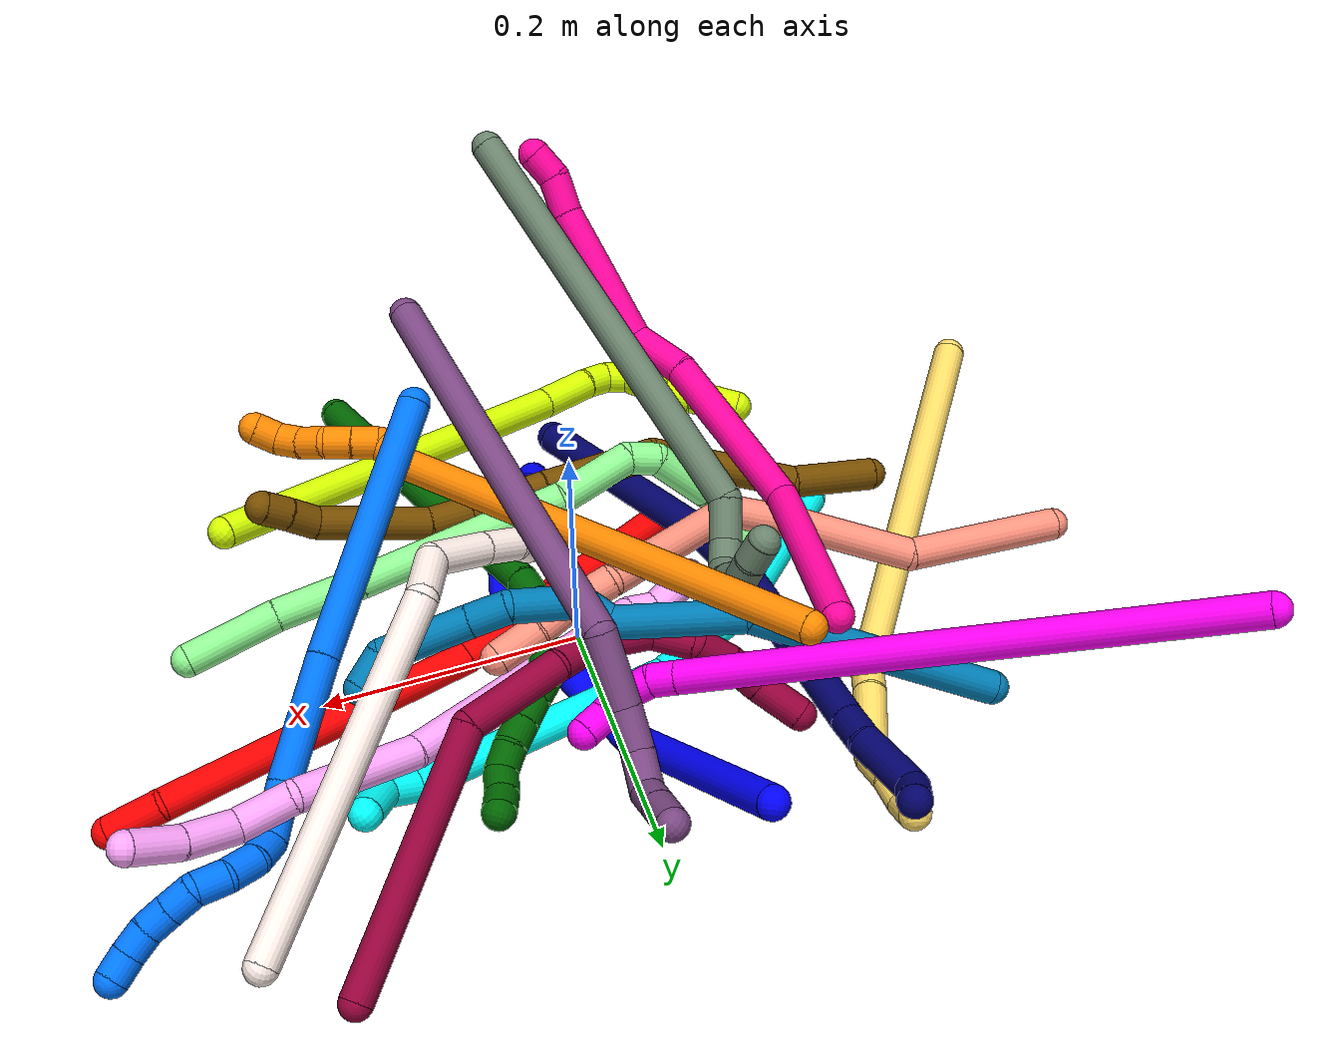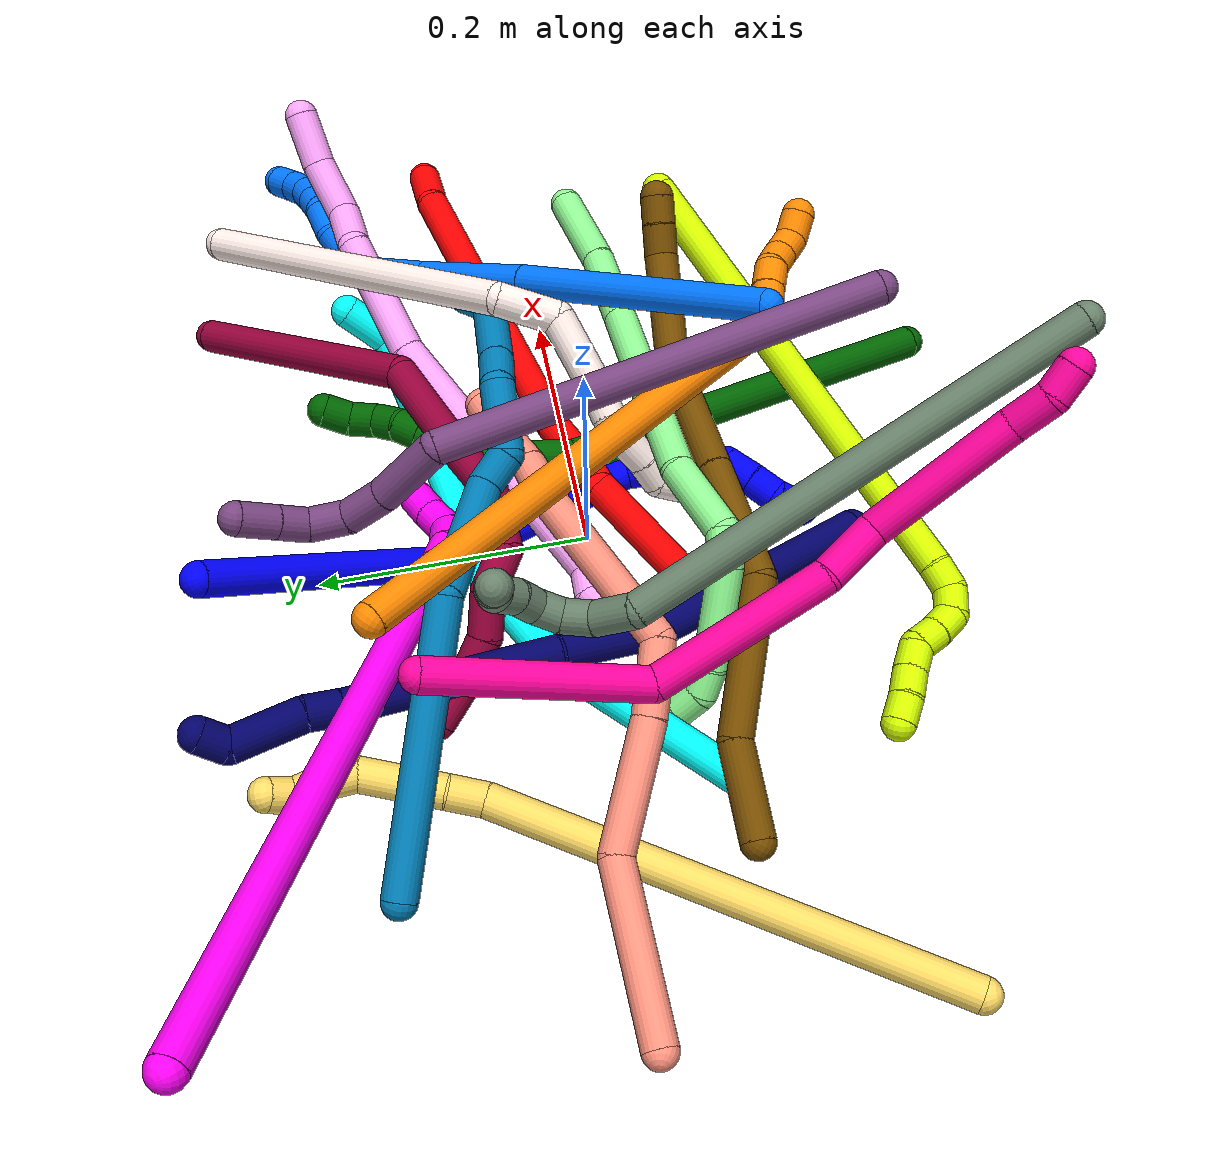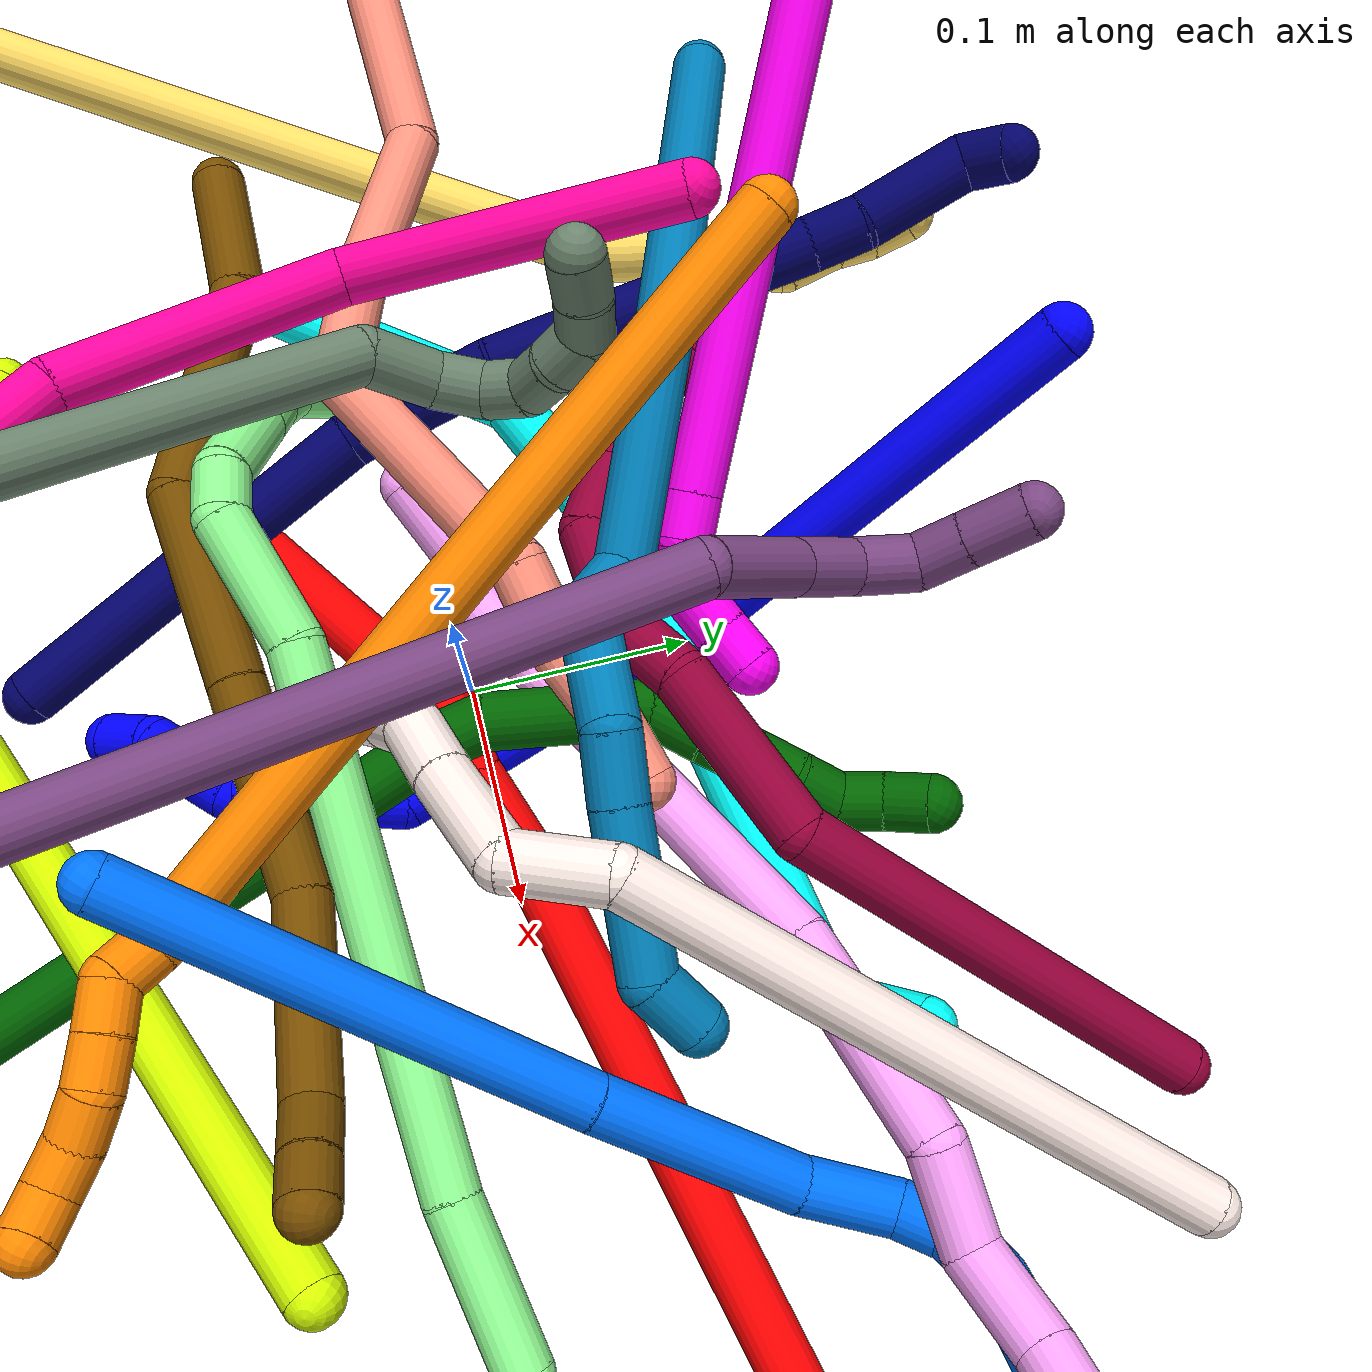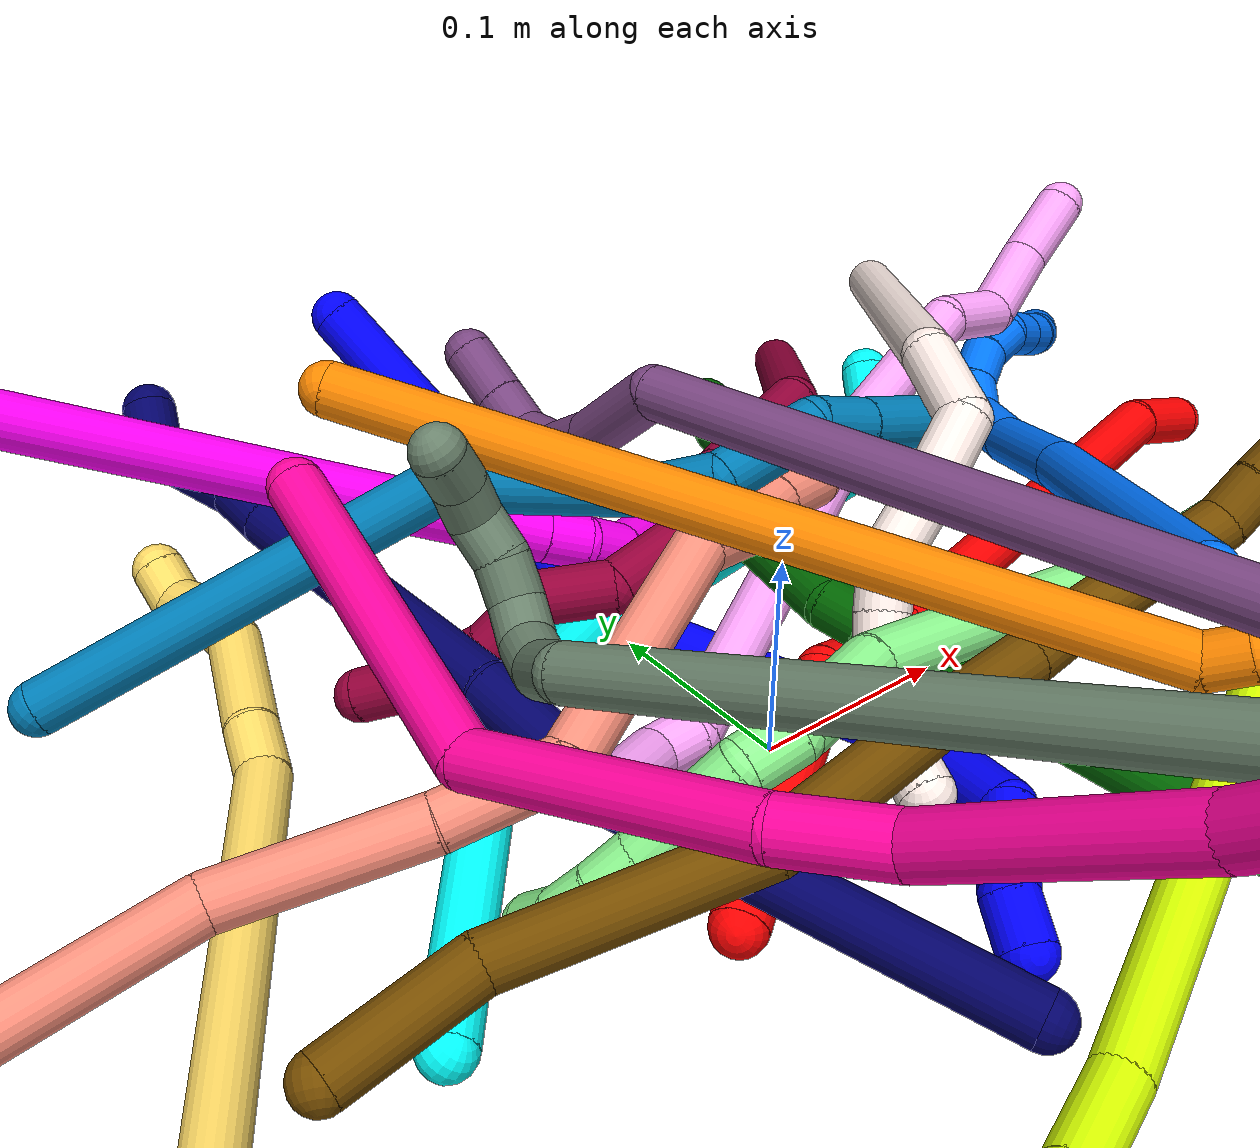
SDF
<sdf version="1.7">
 <world name="default">
  <plugin name="TubeGeneratorPlugin" filename="libtube_generator_plugin.so"/>
  <model name="photoneo_s_sensor">
   <static>1</static>
   <pose>0 0 2 1.57079 1.57079 3.14159</pose>
   <link name="link">
    <inertial><mass>0.1</mass></inertial>
    <sensor name="sensor" type="depth">
     <update_rate>30</update_rate>
     <camera>
      <horizontal_fov>1.22</horizontal_fov>
      <image><width>1920</width><height>1200</height><format>B8G8R8</format></image>
      <clip><near>0.1</near><far>4</far></clip>
      <depth_camera><output>points</output></depth_camera>
     </camera>
     <plugin name="camera_plugin" filename="libgazebo_ros_depth_camera.so">
      <baseline>0.2</baseline>
      <alwaysOn>1</alwaysOn>
      <updateRate>0.0</updateRate>
      <cameraName>camera_ir</cameraName>
      <imageTopicName>/camera/color/image_raw</imageTopicName>
      <cameraInfoTopicName>/camera/color/camera_info</cameraInfoTopicName>
      <depthImageTopicName>/camera/depth/image_raw</depthImageTopicName>
      <depthImageCameraInfoTopicName>/camera/depth/camera_info</depthImageCameraInfoTopicName>
      <pointCloudTopicName>/camera/depth/points</pointCloudTopicName>
      <frameName>fr_optical</frameName>
      <pointCloudCutoff>0.1</pointCloudCutoff>
      <pointCloudCutoffMax>2.0</pointCloudCutoffMax>
      <distortionK1>0</distortionK1>
      <distortionK2>0</distortionK2>
      <distortionK3>0</distortionK3>
      <distortionT1>0</distortionT1>
      <distortionT2>0</distortionT2>
      <CxPrime>0</CxPrime>
      <Cx>0</Cx>
      <Cy>0</Cy>
      <focalLength>0</focalLength>
      <hackBaseline>0</hackBaseline>
     </plugin>
    </sensor>
   </link>
  </model>
  <gravity>0 0 -9.8</gravity>
  <magnetic_field>6e-06 2.3e-05 -4.2e-05</magnetic_field>
  <atmosphere type="adiabatic"/>
  <physics name="default_physics" default="0" type="ode">
   <max_step_size>0.003</max_step_size>
   <real_time_factor>1</real_time_factor>
   <real_time_update_rate>1000</real_time_update_rate>
   <max_contacts>10000</max_contacts>
   <ode>
    <solver>
     <type>quick</type>
     <iters>100</iters>
     <sor>1.3</sor>
     <use_dynamic_moi_rescaling>0</use_dynamic_moi_rescaling>
    </solver>
    <constraints>
     <contact_max_correcting_vel>0</contact_max_correcting_vel>
     <contact_surface_layer>0.001</contact_surface_layer>
     <cfm>0</cfm>
     <erp>0.2</erp>
    </constraints>
   </ode>
  </physics>
  <scene><ambient>0.4 0.4 0.4 1</ambient><background>0.7 0.7 0.7 1</background><shadows>0</shadows></scene>
  <audio><device>default</device></audio>
  <spherical_coordinates>
   <surface_model>EARTH_WGS84</surface_model>
   <latitude_deg>0</latitude_deg>
   <longitude_deg>0</longitude_deg>
   <elevation>0</elevation>
   <heading_deg>0</heading_deg>
  </spherical_coordinates>
  <model name="bin">
   <static>1</static>
   <link name="bottom">
    <collision name="collision-bottom">
     <pose>0 0 -0.01 0 -0 0</pose>
     <geometry><box><size>0.8 0.6 0.02</size></box></geometry>
     <surface>
      <friction><ode><mu>100</mu><mu2>100</mu2></ode></friction>
      <contact><collide_bitmask>65535</collide_bitmask></contact>
     </surface>
    </collision>
   </link>
   <link name="west_wall">
    <collision name="collision-west_wall">
     <pose>-0.41 0 0.1 0 -0 0</pose>
     <geometry><box><size>0.02 0.6 0.2</size></box></geometry>
     <surface>
      <friction><ode><mu>100</mu><mu2>100</mu2></ode></friction>
      <contact><collide_bitmask>65535</collide_bitmask></contact>
     </surface>
    </collision>
   </link>
   <link name="east_wall">
    <collision name="collision-east_wall">
     <pose>0.41 0 0.1 0 -0 0</pose>
     <geometry><box><size>0.02 0.6 0.2</size></box></geometry>
     <surface>
      <friction><ode><mu>100</mu><mu2>100</mu2></ode></friction>
      <contact><collide_bitmask>65535</collide_bitmask></contact>
     </surface>
    </collision>
   </link>
   <link name="south_wall">
    <collision name="collision-south_wall">
     <pose>0 -0.31 0.1 0 -0 0</pose>
     <geometry><box><size>0.8 0.02 0.2</size></box></geometry>
     <surface>
      <friction><ode><mu>100</mu><mu2>100</mu2></ode></friction>
      <contact><collide_bitmask>65535</collide_bitmask></contact>
     </surface>
    </collision>
   </link>
   <link name="north_wall">
    <collision name="collision-north_wall">
     <pose>0 0.31 0.1 0 -0 0</pose>
     <geometry><box><size>0.8 0.02 0.2</size></box></geometry>
     <surface>
      <friction><ode><mu>100</mu><mu2>100</mu2></ode></friction>
      <contact><collide_bitmask>65535</collide_bitmask></contact>
     </surface>
    </collision>
   </link>
  </model>
  <model name="1">
   <static>0</static>
   <link name="1">
    <collision name="collision-cylinder-e_1_1_4">
     <pose>0.042121 -0.089444 -0.011016 1.69334 0.43722 0.492216</pose>
     <geometry><cylinder><radius>0.0125</radius><length>0.198955</length></cylinder></geometry>
     <surface>
      <friction><ode><mu>1.16</mu><mu2>1.16</mu2><slip1>0</slip1><slip2>0</slip2></ode></friction>
      <contact><ode><kp>1e+06</kp><kd>1</kd><max_vel>0</max_vel><min_depth>0.001</min_depth></ode></contact>
     </surface>
    </collision>
    <visual name="visual-cylinder-e_1_1_4">
     <pose>0.042121 -0.089444 -0.011016 1.69334 0.43722 0.492216</pose>
     <geometry><cylinder><radius>0.0125</radius><length>0.198955</length></cylinder></geometry>
     <material><ambient>0 0 1 1</ambient></material>
    </visual>
    <collision name="collision-cylinder-e_2_4_5">
     <pose>0.08641 -0.244406 -0.065827 2.16003 0.027505 0.051461</pose>
     <geometry><cylinder><radius>0.0125</radius><length>0.157674</length></cylinder></geometry>
     <surface>
      <friction><ode><mu>1.16</mu><mu2>1.16</mu2><slip1>0</slip1><slip2>0</slip2></ode></friction>
      <contact><ode><kp>1e+06</kp><kd>1</kd><max_vel>0</max_vel><min_depth>0.001</min_depth></ode></contact>
     </surface>
    </collision>
    <visual name="visual-cylinder-e_2_4_5">
     <pose>0.08641 -0.244406 -0.065827 2.16003 0.027505 0.051461</pose>
     <geometry><cylinder><radius>0.0125</radius><length>0.157674</length></cylinder></geometry>
     <material><ambient>0 0 1 1</ambient></material>
    </visual>
    <collision name="collision-cylinder-e_3_5_6">
     <pose>0.09344 -0.31734 -0.126736 2.73266 0.254989 1.10736</pose>
     <geometry><cylinder><radius>0.0125</radius><length>0.038552</length></cylinder></geometry>
     <surface>
      <friction><ode><mu>1.16</mu><mu2>1.16</mu2><slip1>0</slip1><slip2>0</slip2></ode></friction>
      <contact><ode><kp>1e+06</kp><kd>1</kd><max_vel>0</max_vel><min_depth>0.001</min_depth></ode></contact>
     </surface>
    </collision>
    <visual name="visual-cylinder-e_3_5_6">
     <pose>0.09344 -0.31734 -0.126736 2.73266 0.254989 1.10736</pose>
     <geometry><cylinder><radius>0.0125</radius><length>0.038552</length></cylinder></geometry>
     <material><ambient>0 0 1 1</ambient></material>
    </visual>
    <collision name="collision-cylinder-e_4_6_7">
     <pose>0.103094 -0.331968 -0.160257 2.72748 0.261252 1.11776</pose>
     <geometry><cylinder><radius>0.0125</radius><length>0.0371</length></cylinder></geometry>
     <surface>
      <friction><ode><mu>1.16</mu><mu2>1.16</mu2><slip1>0</slip1><slip2>0</slip2></ode></friction>
      <contact><ode><kp>1e+06</kp><kd>1</kd><max_vel>0</max_vel><min_depth>0.001</min_depth></ode></contact>
     </surface>
    </collision>
    <visual name="visual-cylinder-e_4_6_7">
     <pose>0.103094 -0.331968 -0.160257 2.72748 0.261252 1.11776</pose>
     <geometry><cylinder><radius>0.0125</radius><length>0.0371</length></cylinder></geometry>
     <material><ambient>0 0 1 1</ambient></material>
    </visual>
    <collision name="collision-cylinder-e_5_7_8">
     <pose>0.116799 -0.339794 -0.184386 3.06207 0.855286 2.96745</pose>
     <geometry><cylinder><radius>0.0125</radius><length>0.023622</length></cylinder></geometry>
     <surface>
      <friction><ode><mu>1.16</mu><mu2>1.16</mu2><slip1>0</slip1><slip2>0</slip2></ode></friction>
      <contact><ode><kp>1e+06</kp><kd>1</kd><max_vel>0</max_vel><min_depth>0.001</min_depth></ode></contact>
     </surface>
    </collision>
    <visual name="visual-cylinder-e_5_7_8">
     <pose>0.116799 -0.339794 -0.184386 3.06207 0.855286 2.96745</pose>
     <geometry><cylinder><radius>0.0125</radius><length>0.023622</length></cylinder></geometry>
     <material><ambient>0 0 1 1</ambient></material>
    </visual>
    <collision name="collision-cylinder-e_6_8_9">
     <pose>0.13389 -0.340942 -0.198375 3.05683 0.915193 2.9698</pose>
     <geometry><cylinder><radius>0.0125</radius><length>0.020631</length></cylinder></geometry>
     <surface>
      <friction><ode><mu>1.16</mu><mu2>1.16</mu2><slip1>0</slip1><slip2>0</slip2></ode></friction>
      <contact><ode><kp>1e+06</kp><kd>1</kd><max_vel>0</max_vel><min_depth>0.001</min_depth></ode></contact>
     </surface>
    </collision>
    <visual name="visual-cylinder-e_6_8_9">
     <pose>0.13389 -0.340942 -0.198375 3.05683 0.915193 2.9698</pose>
     <geometry><cylinder><radius>0.0125</radius><length>0.020631</length></cylinder></geometry>
     <material><ambient>0 0 1 1</ambient></material>
    </visual>
    <collision name="collision-cylinder-e_7_9_2">
     <pose>0.151212 -0.347198 -0.209255 2.24923 0.893687 1.57249</pose>
     <geometry><cylinder><radius>0.0125</radius><length>0.023467</length></cylinder></geometry>
     <surface>
      <friction><ode><mu>1.16</mu><mu2>1.16</mu2><slip1>0</slip1><slip2>0</slip2></ode></friction>
      <contact><ode><kp>1e+06</kp><kd>1</kd><max_vel>0</max_vel><min_depth>0.001</min_depth></ode></contact>
     </surface>
    </collision>
    <visual name="visual-cylinder-e_7_9_2">
     <pose>0.151212 -0.347198 -0.209255 2.24923 0.893687 1.57249</pose>
     <geometry><cylinder><radius>0.0125</radius><length>0.023467</length></cylinder></geometry>
     <material><ambient>0 0 1 1</ambient></material>
    </visual>
    <collision name="collision-sphere-2">
     <pose>0.160357 -0.352922 -0.213869 0 -0 0</pose>
     <geometry><sphere><radius>0.0125</radius></sphere></geometry>
     <surface>
      <friction><ode><mu>1.16</mu><mu2>1.16</mu2><slip1>0</slip1><slip2>0</slip2></ode></friction>
      <contact><ode><kp>1e+06</kp><kd>1</kd><max_vel>0</max_vel><min_depth>0.001</min_depth></ode></contact>
     </surface>
    </collision>
    <visual name="visual-sphere-2">
     <pose>0.160357 -0.352922 -0.213869 0 -0 0</pose>
     <geometry><sphere><radius>0.0125</radius></sphere></geometry>
     <material><ambient>0 0 1 1</ambient></material>
    </visual>
    <collision name="collision-sphere-9">
     <pose>0.142067 -0.341475 -0.204641 0 -0 0</pose>
     <geometry><sphere><radius>0.0125</radius></sphere></geometry>
     <surface>
      <friction><ode><mu>1.16</mu><mu2>1.16</mu2><slip1>0</slip1><slip2>0</slip2></ode></friction>
      <contact><ode><kp>1e+06</kp><kd>1</kd><max_vel>0</max_vel><min_depth>0.001</min_depth></ode></contact>
     </surface>
    </collision>
    <visual name="visual-sphere-9">
     <pose>0.142067 -0.341475 -0.204641 0 -0 0</pose>
     <geometry><sphere><radius>0.0125</radius></sphere></geometry>
     <material><ambient>0 0 1 1</ambient></material>
    </visual>
    <collision name="collision-sphere-4">
     <pose>0.084242 -0.178888 -0.022032 0 -0 0</pose>
     <geometry><sphere><radius>0.0125</radius></sphere></geometry>
     <surface>
      <friction><ode><mu>1.16</mu><mu2>1.16</mu2><slip1>0</slip1><slip2>0</slip2></ode></friction>
      <contact><ode><kp>1e+06</kp><kd>1</kd><max_vel>0</max_vel><min_depth>0.001</min_depth></ode></contact>
     </surface>
    </collision>
    <visual name="visual-sphere-4">
     <pose>0.084242 -0.178888 -0.022032 0 -0 0</pose>
     <geometry><sphere><radius>0.0125</radius></sphere></geometry>
     <material><ambient>0 0 1 1</ambient></material>
    </visual>
    <collision name="collision-sphere-1">
     <geometry><sphere><radius>0.0125</radius></sphere></geometry>
     <surface>
      <friction><ode><mu>1.16</mu><mu2>1.16</mu2><slip1>0</slip1><slip2>0</slip2></ode></friction>
      <contact><ode><kp>1e+06</kp><kd>1</kd><max_vel>0</max_vel><min_depth>0.001</min_depth></ode></contact>
     </surface>
    </collision>
    <visual name="visual-sphere-1">
     <geometry><sphere><radius>0.0125</radius></sphere></geometry>
     <material><ambient>0 0 1 1</ambient></material>
    </visual>
    <collision name="collision-sphere-8">
     <pose>0.125713 -0.34041 -0.192109 0 -0 0</pose>
     <geometry><sphere><radius>0.0125</radius></sphere></geometry>
     <surface>
      <friction><ode><mu>1.16</mu><mu2>1.16</mu2><slip1>0</slip1><slip2>0</slip2></ode></friction>
      <contact><ode><kp>1e+06</kp><kd>1</kd><max_vel>0</max_vel><min_depth>0.001</min_depth></ode></contact>
     </surface>
    </collision>
    <visual name="visual-sphere-8">
     <pose>0.125713 -0.34041 -0.192109 0 -0 0</pose>
     <geometry><sphere><radius>0.0125</radius></sphere></geometry>
     <material><ambient>0 0 1 1</ambient></material>
    </visual>
    <collision name="collision-sphere-5">
     <pose>0.088578 -0.309923 -0.109621 0 -0 0</pose>
     <geometry><sphere><radius>0.0125</radius></sphere></geometry>
     <surface>
      <friction><ode><mu>1.16</mu><mu2>1.16</mu2><slip1>0</slip1><slip2>0</slip2></ode></friction>
      <contact><ode><kp>1e+06</kp><kd>1</kd><max_vel>0</max_vel><min_depth>0.001</min_depth></ode></contact>
     </surface>
    </collision>
    <visual name="visual-sphere-5">
     <pose>0.088578 -0.309923 -0.109621 0 -0 0</pose>
     <geometry><sphere><radius>0.0125</radius></sphere></geometry>
     <material><ambient>0 0 1 1</ambient></material>
    </visual>
    <collision name="collision-sphere-6">
     <pose>0.098302 -0.324757 -0.143851 0 -0 0</pose>
     <geometry><sphere><radius>0.0125</radius></sphere></geometry>
     <surface>
      <friction><ode><mu>1.16</mu><mu2>1.16</mu2><slip1>0</slip1><slip2>0</slip2></ode></friction>
      <contact><ode><kp>1e+06</kp><kd>1</kd><max_vel>0</max_vel><min_depth>0.001</min_depth></ode></contact>
     </surface>
    </collision>
    <visual name="visual-sphere-6">
     <pose>0.098302 -0.324757 -0.143851 0 -0 0</pose>
     <geometry><sphere><radius>0.0125</radius></sphere></geometry>
     <material><ambient>0 0 1 1</ambient></material>
    </visual>
    <collision name="collision-sphere-7">
     <pose>0.107885 -0.339179 -0.176662 0 -0 0</pose>
     <geometry><sphere><radius>0.0125</radius></sphere></geometry>
     <surface>
      <friction><ode><mu>1.16</mu><mu2>1.16</mu2><slip1>0</slip1><slip2>0</slip2></ode></friction>
      <contact><ode><kp>1e+06</kp><kd>1</kd><max_vel>0</max_vel><min_depth>0.001</min_depth></ode></contact>
     </surface>
    </collision>
    <visual name="visual-sphere-7">
     <pose>0.107885 -0.339179 -0.176662 0 -0 0</pose>
     <geometry><sphere><radius>0.0125</radius></sphere></geometry>
     <material><ambient>0 0 1 1</ambient></material>
    </visual>
    <inertial>
     <pose>0.077003 -0.20818 -0.073522 0 -0 0</pose>
     <mass>0.5</mass>
     <inertia>
      <ixx>0.001191</ixx>
      <ixy>0</ixy>
      <ixz>0</ixz>
      <iyy>0.000163</iyy>
      <iyz>0</iyz>
      <izz>0.000565</izz>
     </inertia>
    </inertial>
   </link>
   <pose>-0.053291 0.26635 0.125117 2.57742 0.735395 -2.77772</pose>
  </model>
  <model name="2">
   <static>0</static>
   <link name="2">
    <collision name="collision-cylinder-e_1_1_4">
     <pose>-0.007157 -0.010396 -0.017188 2.59763 -0.34228 -1.10957</pose>
     <geometry><cylinder><radius>0.0125</radius><length>0.042649</length></cylinder></geometry>
     <surface>
      <friction><ode><mu>1.16</mu><mu2>1.16</mu2><slip1>0</slip1><slip2>0</slip2></ode></friction>
      <contact><ode><kp>1e+06</kp><kd>1</kd><max_vel>0</max_vel><min_depth>0.001</min_depth></ode></contact>
     </surface>
    </collision>
    <visual name="visual-cylinder-e_1_1_4">
     <pose>-0.007157 -0.010396 -0.017188 2.59763 -0.34228 -1.10957</pose>
     <geometry><cylinder><radius>0.0125</radius><length>0.042649</length></cylinder></geometry>
     <material><ambient>1 0 0 1</ambient></material>
    </visual>
    <collision name="collision-cylinder-e_2_4_5">
     <pose>-0.084822 -0.04729 -0.132246 2.87718 -0.607624 -2.33927</pose>
     <geometry><cylinder><radius>0.0125</radius><length>0.246996</length></cylinder></geometry>
     <surface>
      <friction><ode><mu>1.16</mu><mu2>1.16</mu2><slip1>0</slip1><slip2>0</slip2></ode></friction>
      <contact><ode><kp>1e+06</kp><kd>1</kd><max_vel>0</max_vel><min_depth>0.001</min_depth></ode></contact>
     </surface>
    </collision>
    <visual name="visual-cylinder-e_2_4_5">
     <pose>-0.084822 -0.04729 -0.132246 2.87718 -0.607624 -2.33927</pose>
     <geometry><cylinder><radius>0.0125</radius><length>0.246996</length></cylinder></geometry>
     <material><ambient>1 0 0 1</ambient></material>
    </visual>
    <collision name="collision-cylinder-e_3_5_6">
     <pose>-0.163939 -0.078434 -0.251462 2.92735 -0.375393 -2.11127</pose>
     <geometry><cylinder><radius>0.0125</radius><length>0.046964</length></cylinder></geometry>
     <surface>
      <friction><ode><mu>1.16</mu><mu2>1.16</mu2><slip1>0</slip1><slip2>0</slip2></ode></friction>
      <contact><ode><kp>1e+06</kp><kd>1</kd><max_vel>0</max_vel><min_depth>0.001</min_depth></ode></contact>
     </surface>
    </collision>
    <visual name="visual-cylinder-e_3_5_6">
     <pose>-0.163939 -0.078434 -0.251462 2.92735 -0.375393 -2.11127</pose>
     <geometry><cylinder><radius>0.0125</radius><length>0.046964</length></cylinder></geometry>
     <material><ambient>1 0 0 1</ambient></material>
    </visual>
    <collision name="collision-cylinder-e_4_6_7">
     <pose>-0.177444 -0.088381 -0.285837 2.75499 -0.334954 -1.42477</pose>
     <geometry><cylinder><radius>0.0125</radius><length>0.029786</length></cylinder></geometry>
     <surface>
      <friction><ode><mu>1.16</mu><mu2>1.16</mu2><slip1>0</slip1><slip2>0</slip2></ode></friction>
      <contact><ode><kp>1e+06</kp><kd>1</kd><max_vel>0</max_vel><min_depth>0.001</min_depth></ode></contact>
     </surface>
    </collision>
    <visual name="visual-cylinder-e_4_6_7">
     <pose>-0.177444 -0.088381 -0.285837 2.75499 -0.334954 -1.42477</pose>
     <geometry><cylinder><radius>0.0125</radius><length>0.029786</length></cylinder></geometry>
     <material><ambient>1 0 0 1</ambient></material>
    </visual>
    <collision name="collision-cylinder-e_5_7_2">
     <pose>-0.224395 -0.081312 -0.349271 -2.90089 -0.680967 2.4837</pose>
     <geometry><cylinder><radius>0.0125</radius><length>0.133604</length></cylinder></geometry>
     <surface>
      <friction><ode><mu>1.16</mu><mu2>1.16</mu2><slip1>0</slip1><slip2>0</slip2></ode></friction>
      <contact><ode><kp>1e+06</kp><kd>1</kd><max_vel>0</max_vel><min_depth>0.001</min_depth></ode></contact>
     </surface>
    </collision>
    <visual name="visual-cylinder-e_5_7_2">
     <pose>-0.224395 -0.081312 -0.349271 -2.90089 -0.680967 2.4837</pose>
     <geometry><cylinder><radius>0.0125</radius><length>0.133604</length></cylinder></geometry>
     <material><ambient>1 0 0 1</ambient></material>
    </visual>
    <collision name="collision-sphere-2">
     <pose>-0.266449 -0.068939 -0.399677 0 -0 0</pose>
     <geometry><sphere><radius>0.0125</radius></sphere></geometry>
     <surface>
      <friction><ode><mu>1.16</mu><mu2>1.16</mu2><slip1>0</slip1><slip2>0</slip2></ode></friction>
      <contact><ode><kp>1e+06</kp><kd>1</kd><max_vel>0</max_vel><min_depth>0.001</min_depth></ode></contact>
     </surface>
    </collision>
    <visual name="visual-sphere-2">
     <pose>-0.266449 -0.068939 -0.399677 0 -0 0</pose>
     <geometry><sphere><radius>0.0125</radius></sphere></geometry>
     <material><ambient>1 0 0 1</ambient></material>
    </visual>
    <collision name="collision-sphere-7">
     <pose>-0.18234 -0.093685 -0.298864 0 -0 0</pose>
     <geometry><sphere><radius>0.0125</radius></sphere></geometry>
     <surface>
      <friction><ode><mu>1.16</mu><mu2>1.16</mu2><slip1>0</slip1><slip2>0</slip2></ode></friction>
      <contact><ode><kp>1e+06</kp><kd>1</kd><max_vel>0</max_vel><min_depth>0.001</min_depth></ode></contact>
     </surface>
    </collision>
    <visual name="visual-sphere-7">
     <pose>-0.18234 -0.093685 -0.298864 0 -0 0</pose>
     <geometry><sphere><radius>0.0125</radius></sphere></geometry>
     <material><ambient>1 0 0 1</ambient></material>
    </visual>
    <collision name="collision-sphere-6">
     <pose>-0.172548 -0.083078 -0.27281 0 -0 0</pose>
     <geometry><sphere><radius>0.0125</radius></sphere></geometry>
     <surface>
      <friction><ode><mu>1.16</mu><mu2>1.16</mu2><slip1>0</slip1><slip2>0</slip2></ode></friction>
      <contact><ode><kp>1e+06</kp><kd>1</kd><max_vel>0</max_vel><min_depth>0.001</min_depth></ode></contact>
     </surface>
    </collision>
    <visual name="visual-sphere-6">
     <pose>-0.172548 -0.083078 -0.27281 0 -0 0</pose>
     <geometry><sphere><radius>0.0125</radius></sphere></geometry>
     <material><ambient>1 0 0 1</ambient></material>
    </visual>
    <collision name="collision-sphere-5">
     <pose>-0.15533 -0.073789 -0.230115 0 -0 0</pose>
     <geometry><sphere><radius>0.0125</radius></sphere></geometry>
     <surface>
      <friction><ode><mu>1.16</mu><mu2>1.16</mu2><slip1>0</slip1><slip2>0</slip2></ode></friction>
      <contact><ode><kp>1e+06</kp><kd>1</kd><max_vel>0</max_vel><min_depth>0.001</min_depth></ode></contact>
     </surface>
    </collision>
    <visual name="visual-sphere-5">
     <pose>-0.15533 -0.073789 -0.230115 0 -0 0</pose>
     <geometry><sphere><radius>0.0125</radius></sphere></geometry>
     <material><ambient>1 0 0 1</ambient></material>
    </visual>
    <collision name="collision-sphere-1">
     <geometry><sphere><radius>0.0125</radius></sphere></geometry>
     <surface>
      <friction><ode><mu>1.16</mu><mu2>1.16</mu2><slip1>0</slip1><slip2>0</slip2></ode></friction>
      <contact><ode><kp>1e+06</kp><kd>1</kd><max_vel>0</max_vel><min_depth>0.001</min_depth></ode></contact>
     </surface>
    </collision>
    <visual name="visual-sphere-1">
     <geometry><sphere><radius>0.0125</radius></sphere></geometry>
     <material><ambient>1 0 0 1</ambient></material>
    </visual>
    <collision name="collision-sphere-4">
     <pose>-0.014315 -0.020792 -0.034377 0 -0 0</pose>
     <geometry><sphere><radius>0.0125</radius></sphere></geometry>
     <surface>
      <friction><ode><mu>1.16</mu><mu2>1.16</mu2><slip1>0</slip1><slip2>0</slip2></ode></friction>
      <contact><ode><kp>1e+06</kp><kd>1</kd><max_vel>0</max_vel><min_depth>0.001</min_depth></ode></contact>
     </surface>
    </collision>
    <visual name="visual-sphere-4">
     <pose>-0.014315 -0.020792 -0.034377 0 -0 0</pose>
     <geometry><sphere><radius>0.0125</radius></sphere></geometry>
     <material><ambient>1 0 0 1</ambient></material>
    </visual>
    <inertial>
     <pose>-0.128441 -0.058607 -0.20077 0 -0 0</pose>
     <mass>0.5</mass>
     <inertia>
      <ixx>-0.001538</ixx>
      <ixy>0</ixy>
      <ixz>0</ixz>
      <iyy>0.00049</iyy>
      <iyz>0</iyz>
      <izz>0.001068</izz>
     </inertia>
    </inertial>
   </link>
   <pose>0.369755 0.067125 0.011614 -2.41685 -0.912329 -0.140713</pose>
  </model>
  <model name="3">
   <static>0</static>
   <link name="3">
    <collision name="collision-cylinder-e_1_1_4">
     <pose>0.075735 0.001402 -0.014438 -3.04481 1.38155 -3.02455</pose>
     <geometry><cylinder><radius>0.0125</radius><length>0.154224</length></cylinder></geometry>
     <surface>
      <friction><ode><mu>1.16</mu><mu2>1.16</mu2><slip1>0</slip1><slip2>0</slip2></ode></friction>
      <contact><ode><kp>1e+06</kp><kd>1</kd><max_vel>0</max_vel><min_depth>0.001</min_depth></ode></contact>
     </surface>
    </collision>
    <visual name="visual-cylinder-e_1_1_4">
     <pose>0.075735 0.001402 -0.014438 -3.04481 1.38155 -3.02455</pose>
     <geometry><cylinder><radius>0.0125</radius><length>0.154224</length></cylinder></geometry>
     <material><ambient>0.003922 1 0.996078 1</ambient></material>
    </visual>
    <collision name="collision-cylinder-e_2_4_5">
     <pose>0.185566 0.022481 -0.034841 -1.86514 1.02814 -1.30136</pose>
     <geometry><cylinder><radius>0.0125</radius><length>0.079632</length></cylinder></geometry>
     <surface>
      <friction><ode><mu>1.16</mu><mu2>1.16</mu2><slip1>0</slip1><slip2>0</slip2></ode></friction>
      <contact><ode><kp>1e+06</kp><kd>1</kd><max_vel>0</max_vel><min_depth>0.001</min_depth></ode></contact>
     </surface>
    </collision>
    <visual name="visual-cylinder-e_2_4_5">
     <pose>0.185566 0.022481 -0.034841 -1.86514 1.02814 -1.30136</pose>
     <geometry><cylinder><radius>0.0125</radius><length>0.079632</length></cylinder></geometry>
     <material><ambient>0.003922 1 0.996078 1</ambient></material>
    </visual>
    <collision name="collision-cylinder-e_3_5_6">
     <pose>0.29023 0.104209 -0.075378 -2.07911 0.782125 -1.22371</pose>
     <geometry><cylinder><radius>0.0125</radius><length>0.200253</length></cylinder></geometry>
     <surface>
      <friction><ode><mu>1.16</mu><mu2>1.16</mu2><slip1>0</slip1><slip2>0</slip2></ode></friction>
      <contact><ode><kp>1e+06</kp><kd>1</kd><max_vel>0</max_vel><min_depth>0.001</min_depth></ode></contact>
     </surface>
    </collision>
    <visual name="visual-cylinder-e_3_5_6">
     <pose>0.29023 0.104209 -0.075378 -2.07911 0.782125 -1.22371</pose>
     <geometry><cylinder><radius>0.0125</radius><length>0.200253</length></cylinder></geometry>
     <material><ambient>0.003922 1 0.996078 1</ambient></material>
    </visual>
    <collision name="collision-cylinder-e_4_6_7">
     <pose>0.370406 0.170369 -0.119016 -2.71607 0.767684 -2.15924</pose>
     <geometry><cylinder><radius>0.0125</radius><length>0.027668</length></cylinder></geometry>
     <surface>
      <friction><ode><mu>1.16</mu><mu2>1.16</mu2><slip1>0</slip1><slip2>0</slip2></ode></friction>
      <contact><ode><kp>1e+06</kp><kd>1</kd><max_vel>0</max_vel><min_depth>0.001</min_depth></ode></contact>
     </surface>
    </collision>
    <visual name="visual-cylinder-e_4_6_7">
     <pose>0.370406 0.170369 -0.119016 -2.71607 0.767684 -2.15924</pose>
     <geometry><cylinder><radius>0.0125</radius><length>0.027668</length></cylinder></geometry>
     <material><ambient>0.003922 1 0.996078 1</ambient></material>
    </visual>
    <collision name="collision-cylinder-e_5_7_2">
     <pose>0.396969 0.168958 -0.134959 2.4653 1.09123 2.09156</pose>
     <geometry><cylinder><radius>0.0125</radius><length>0.038223</length></cylinder></geometry>
     <surface>
      <friction><ode><mu>1.16</mu><mu2>1.16</mu2><slip1>0</slip1><slip2>0</slip2></ode></friction>
      <contact><ode><kp>1e+06</kp><kd>1</kd><max_vel>0</max_vel><min_depth>0.001</min_depth></ode></contact>
     </surface>
    </collision>
    <visual name="visual-cylinder-e_5_7_2">
     <pose>0.396969 0.168958 -0.134959 2.4653 1.09123 2.09156</pose>
     <geometry><cylinder><radius>0.0125</radius><length>0.038223</length></cylinder></geometry>
     <material><ambient>0.003922 1 0.996078 1</ambient></material>
    </visual>
    <collision name="collision-sphere-2">
     <pose>0.413924 0.163439 -0.141836 0 -0 0</pose>
     <geometry><sphere><radius>0.0125</radius></sphere></geometry>
     <surface>
      <friction><ode><mu>1.16</mu><mu2>1.16</mu2><slip1>0</slip1><slip2>0</slip2></ode></friction>
      <contact><ode><kp>1e+06</kp><kd>1</kd><max_vel>0</max_vel><min_depth>0.001</min_depth></ode></contact>
     </surface>
    </collision>
    <visual name="visual-sphere-2">
     <pose>0.413924 0.163439 -0.141836 0 -0 0</pose>
     <geometry><sphere><radius>0.0125</radius></sphere></geometry>
     <material><ambient>0.003922 1 0.996078 1</ambient></material>
    </visual>
    <collision name="collision-sphere-7">
     <pose>0.380013 0.174478 -0.128082 0 -0 0</pose>
     <geometry><sphere><radius>0.0125</radius></sphere></geometry>
     <surface>
      <friction><ode><mu>1.16</mu><mu2>1.16</mu2><slip1>0</slip1><slip2>0</slip2></ode></friction>
      <contact><ode><kp>1e+06</kp><kd>1</kd><max_vel>0</max_vel><min_depth>0.001</min_depth></ode></contact>
     </surface>
    </collision>
    <visual name="visual-sphere-7">
     <pose>0.380013 0.174478 -0.128082 0 -0 0</pose>
     <geometry><sphere><radius>0.0125</radius></sphere></geometry>
     <material><ambient>0.003922 1 0.996078 1</ambient></material>
    </visual>
    <collision name="collision-sphere-6">
     <pose>0.360799 0.16626 -0.109949 0 -0 0</pose>
     <geometry><sphere><radius>0.0125</radius></sphere></geometry>
     <surface>
      <friction><ode><mu>1.16</mu><mu2>1.16</mu2><slip1>0</slip1><slip2>0</slip2></ode></friction>
      <contact><ode><kp>1e+06</kp><kd>1</kd><max_vel>0</max_vel><min_depth>0.001</min_depth></ode></contact>
     </surface>
    </collision>
    <visual name="visual-sphere-6">
     <pose>0.360799 0.16626 -0.109949 0 -0 0</pose>
     <geometry><sphere><radius>0.0125</radius></sphere></geometry>
     <material><ambient>0.003922 1 0.996078 1</ambient></material>
    </visual>
    <collision name="collision-sphere-5">
     <pose>0.219662 0.042158 -0.040806 0 -0 0</pose>
     <geometry><sphere><radius>0.0125</radius></sphere></geometry>
     <surface>
      <friction><ode><mu>1.16</mu><mu2>1.16</mu2><slip1>0</slip1><slip2>0</slip2></ode></friction>
      <contact><ode><kp>1e+06</kp><kd>1</kd><max_vel>0</max_vel><min_depth>0.001</min_depth></ode></contact>
     </surface>
    </collision>
    <visual name="visual-sphere-5">
     <pose>0.219662 0.042158 -0.040806 0 -0 0</pose>
     <geometry><sphere><radius>0.0125</radius></sphere></geometry>
     <material><ambient>0.003922 1 0.996078 1</ambient></material>
    </visual>
    <collision name="collision-sphere-1">
     <geometry><sphere><radius>0.0125</radius></sphere></geometry>
     <surface>
      <friction><ode><mu>1.16</mu><mu2>1.16</mu2><slip1>0</slip1><slip2>0</slip2></ode></friction>
      <contact><ode><kp>1e+06</kp><kd>1</kd><max_vel>0</max_vel><min_depth>0.001</min_depth></ode></contact>
     </surface>
    </collision>
    <visual name="visual-sphere-1">
     <geometry><sphere><radius>0.0125</radius></sphere></geometry>
     <material><ambient>0.003922 1 0.996078 1</ambient></material>
    </visual>
    <collision name="collision-sphere-4">
     <pose>0.15147 0.002803 -0.028876 0 -0 0</pose>
     <geometry><sphere><radius>0.0125</radius></sphere></geometry>
     <surface>
      <friction><ode><mu>1.16</mu><mu2>1.16</mu2><slip1>0</slip1><slip2>0</slip2></ode></friction>
      <contact><ode><kp>1e+06</kp><kd>1</kd><max_vel>0</max_vel><min_depth>0.001</min_depth></ode></contact>
     </surface>
    </collision>
    <visual name="visual-sphere-4">
     <pose>0.15147 0.002803 -0.028876 0 -0 0</pose>
     <geometry><sphere><radius>0.0125</radius></sphere></geometry>
     <material><ambient>0.003922 1 0.996078 1</ambient></material>
    </visual>
    <inertial>
     <pose>0.219997 0.068093 -0.057095 0 -0 0</pose>
     <mass>0.5</mass>
     <inertia>
      <ixx>-0.000339</ixx>
      <ixy>0</ixy>
      <ixz>0</ixz>
      <iyy>0.000164</iyy>
      <iyz>0</iyz>
      <izz>-0.001287</izz>
     </inertia>
    </inertial>
   </link>
   <pose>-0.216041 -0.065174 0.011895 -2.54782 -0.063786 0.955039</pose>
  </model>
  <model name="4">
   <static>0</static>
   <link name="4">
    <collision name="collision-cylinder-e_1_1_4">
     <pose>0.011294 0.007391 -0.012328 -2.60152 0.666007 -1.79179</pose>
     <geometry><cylinder><radius>0.0125</radius><length>0.03656</length></cylinder></geometry>
     <surface>
      <friction><ode><mu>1.16</mu><mu2>1.16</mu2><slip1>0</slip1><slip2>0</slip2></ode></friction>
      <contact><ode><kp>1e+06</kp><kd>1</kd><max_vel>0</max_vel><min_depth>0.001</min_depth></ode></contact>
     </surface>
    </collision>
    <visual name="visual-cylinder-e_1_1_4">
     <pose>0.011294 0.007391 -0.012328 -2.60152 0.666007 -1.79179</pose>
     <geometry><cylinder><radius>0.0125</radius><length>0.03656</length></cylinder></geometry>
     <material><ambient>1 0.65098 0.996078 1</ambient></material>
    </visual>
    <collision name="collision-cylinder-e_2_4_5">
     <pose>0.031717 0.020318 -0.026303 -1.86007 1.00661 -1.27199</pose>
     <geometry><cylinder><radius>0.0125</radius><length>0.021604</length></cylinder></geometry>
     <surface>
      <friction><ode><mu>1.16</mu><mu2>1.16</mu2><slip1>0</slip1><slip2>0</slip2></ode></friction>
      <contact><ode><kp>1e+06</kp><kd>1</kd><max_vel>0</max_vel><min_depth>0.001</min_depth></ode></contact>
     </surface>
    </collision>
    <visual name="visual-cylinder-e_2_4_5">
     <pose>0.031717 0.020318 -0.026303 -1.86007 1.00661 -1.27199</pose>
     <geometry><cylinder><radius>0.0125</radius><length>0.021604</length></cylinder></geometry>
     <material><ambient>1 0.65098 0.996078 1</ambient></material>
    </visual>
    <collision name="collision-cylinder-e_3_5_6">
     <pose>0.093891 0.108601 -0.075367 -2.09114 0.507602 -0.841717</pose>
     <geometry><cylinder><radius>0.0125</radius><length>0.218259</length></cylinder></geometry>
     <surface>
      <friction><ode><mu>1.16</mu><mu2>1.16</mu2><slip1>0</slip1><slip2>0</slip2></ode></friction>
      <contact><ode><kp>1e+06</kp><kd>1</kd><max_vel>0</max_vel><min_depth>0.001</min_depth></ode></contact>
     </surface>
    </collision>
    <visual name="visual-cylinder-e_3_5_6">
     <pose>0.093891 0.108601 -0.075367 -2.09114 0.507602 -0.841717</pose>
     <geometry><cylinder><radius>0.0125</radius><length>0.218259</length></cylinder></geometry>
     <material><ambient>1 0.65098 0.996078 1</ambient></material>
    </visual>
    <collision name="collision-cylinder-e_4_6_7">
     <pose>0.1761 0.22752 -0.135554 -1.91019 0.650034 -0.889048</pose>
     <geometry><cylinder><radius>0.0125</radius><length>0.096373</length></cylinder></geometry>
     <surface>
      <friction><ode><mu>1.16</mu><mu2>1.16</mu2><slip1>0</slip1><slip2>0</slip2></ode></friction>
      <contact><ode><kp>1e+06</kp><kd>1</kd><max_vel>0</max_vel><min_depth>0.001</min_depth></ode></contact>
     </surface>
    </collision>
    <visual name="visual-cylinder-e_4_6_7">
     <pose>0.1761 0.22752 -0.135554 -1.91019 0.650034 -0.889048</pose>
     <geometry><cylinder><radius>0.0125</radius><length>0.096373</length></cylinder></geometry>
     <material><ambient>1 0.65098 0.996078 1</ambient></material>
    </visual>
    <collision name="collision-cylinder-e_5_7_8">
     <pose>0.223322 0.270502 -0.157644 -2.51049 1.00205 -2.06645</pose>
     <geometry><cylinder><radius>0.0125</radius><length>0.042865</length></cylinder></geometry>
     <surface>
      <friction><ode><mu>1.16</mu><mu2>1.16</mu2><slip1>0</slip1><slip2>0</slip2></ode></friction>
      <contact><ode><kp>1e+06</kp><kd>1</kd><max_vel>0</max_vel><min_depth>0.001</min_depth></ode></contact>
     </surface>
    </collision>
    <visual name="visual-cylinder-e_5_7_8">
     <pose>0.223322 0.270502 -0.157644 -2.51049 1.00205 -2.06645</pose>
     <geometry><cylinder><radius>0.0125</radius><length>0.042865</length></cylinder></geometry>
     <material><ambient>1 0.65098 0.996078 1</ambient></material>
    </visual>
    <collision name="collision-cylinder-e_6_8_9">
     <pose>0.252407 0.295935 -0.170821 -1.77505 0.525471 -0.63817</pose>
     <geometry><cylinder><radius>0.0125</radius><length>0.043966</length></cylinder></geometry>
     <surface>
      <friction><ode><mu>1.16</mu><mu2>1.16</mu2><slip1>0</slip1><slip2>0</slip2></ode></friction>
      <contact><ode><kp>1e+06</kp><kd>1</kd><max_vel>0</max_vel><min_depth>0.001</min_depth></ode></contact>
     </surface>
    </collision>
    <visual name="visual-cylinder-e_6_8_9">
     <pose>0.252407 0.295935 -0.170821 -1.77505 0.525471 -0.63817</pose>
     <geometry><cylinder><radius>0.0125</radius><length>0.043966</length></cylinder></geometry>
     <material><ambient>1 0.65098 0.996078 1</ambient></material>
    </visual>
    <collision name="collision-cylinder-e_7_9_2">
     <pose>0.273678 0.331951 -0.174736 -1.57412 0.532244 -0.533936</pose>
     <geometry><cylinder><radius>0.0125</radius><length>0.040372</length></cylinder></geometry>
     <surface>
      <friction><ode><mu>1.16</mu><mu2>1.16</mu2><slip1>0</slip1><slip2>0</slip2></ode></friction>
      <contact><ode><kp>1e+06</kp><kd>1</kd><max_vel>0</max_vel><min_depth>0.001</min_depth></ode></contact>
     </surface>
    </collision>
    <visual name="visual-cylinder-e_7_9_2">
     <pose>0.273678 0.331951 -0.174736 -1.57412 0.532244 -0.533936</pose>
     <geometry><cylinder><radius>0.0125</radius><length>0.040372</length></cylinder></geometry>
     <material><ambient>1 0.65098 0.996078 1</ambient></material>
    </visual>
    <collision name="collision-sphere-2">
     <pose>0.283922 0.349344 -0.174794 0 -0 0</pose>
     <geometry><sphere><radius>0.0125</radius></sphere></geometry>
     <surface>
      <friction><ode><mu>1.16</mu><mu2>1.16</mu2><slip1>0</slip1><slip2>0</slip2></ode></friction>
      <contact><ode><kp>1e+06</kp><kd>1</kd><max_vel>0</max_vel><min_depth>0.001</min_depth></ode></contact>
     </surface>
    </collision>
    <visual name="visual-sphere-2">
     <pose>0.283922 0.349344 -0.174794 0 -0 0</pose>
     <geometry><sphere><radius>0.0125</radius></sphere></geometry>
     <material><ambient>1 0.65098 0.996078 1</ambient></material>
    </visual>
    <collision name="collision-sphere-9">
     <pose>0.263434 0.314557 -0.174678 0 -0 0</pose>
     <geometry><sphere><radius>0.0125</radius></sphere></geometry>
     <surface>
      <friction><ode><mu>1.16</mu><mu2>1.16</mu2><slip1>0</slip1><slip2>0</slip2></ode></friction>
      <contact><ode><kp>1e+06</kp><kd>1</kd><max_vel>0</max_vel><min_depth>0.001</min_depth></ode></contact>
     </surface>
    </collision>
    <visual name="visual-sphere-9">
     <pose>0.263434 0.314557 -0.174678 0 -0 0</pose>
     <geometry><sphere><radius>0.0125</radius></sphere></geometry>
     <material><ambient>1 0.65098 0.996078 1</ambient></material>
    </visual>
    <collision name="collision-sphere-4">
     <pose>0.022589 0.014782 -0.024656 0 -0 0</pose>
     <geometry><sphere><radius>0.0125</radius></sphere></geometry>
     <surface>
      <friction><ode><mu>1.16</mu><mu2>1.16</mu2><slip1>0</slip1><slip2>0</slip2></ode></friction>
      <contact><ode><kp>1e+06</kp><kd>1</kd><max_vel>0</max_vel><min_depth>0.001</min_depth></ode></contact>
     </surface>
    </collision>
    <visual name="visual-sphere-4">
     <pose>0.022589 0.014782 -0.024656 0 -0 0</pose>
     <geometry><sphere><radius>0.0125</radius></sphere></geometry>
     <material><ambient>1 0.65098 0.996078 1</ambient></material>
    </visual>
    <collision name="collision-sphere-1">
     <geometry><sphere><radius>0.0125</radius></sphere></geometry>
     <surface>
      <friction><ode><mu>1.16</mu><mu2>1.16</mu2><slip1>0</slip1><slip2>0</slip2></ode></friction>
      <contact><ode><kp>1e+06</kp><kd>1</kd><max_vel>0</max_vel><min_depth>0.001</min_depth></ode></contact>
     </surface>
    </collision>
    <visual name="visual-sphere-1">
     <geometry><sphere><radius>0.0125</radius></sphere></geometry>
     <material><ambient>1 0.65098 0.996078 1</ambient></material>
    </visual>
    <collision name="collision-sphere-8">
     <pose>0.24138 0.277313 -0.166963 0 -0 0</pose>
     <geometry><sphere><radius>0.0125</radius></sphere></geometry>
     <surface>
      <friction><ode><mu>1.16</mu><mu2>1.16</mu2><slip1>0</slip1><slip2>0</slip2></ode></friction>
      <contact><ode><kp>1e+06</kp><kd>1</kd><max_vel>0</max_vel><min_depth>0.001</min_depth></ode></contact>
     </surface>
    </collision>
    <visual name="visual-sphere-8">
     <pose>0.24138 0.277313 -0.166963 0 -0 0</pose>
     <geometry><sphere><radius>0.0125</radius></sphere></geometry>
     <material><ambient>1 0.65098 0.996078 1</ambient></material>
    </visual>
    <collision name="collision-sphere-5">
     <pose>0.040845 0.025854 -0.027951 0 -0 0</pose>
     <geometry><sphere><radius>0.0125</radius></sphere></geometry>
     <surface>
      <friction><ode><mu>1.16</mu><mu2>1.16</mu2><slip1>0</slip1><slip2>0</slip2></ode></friction>
      <contact><ode><kp>1e+06</kp><kd>1</kd><max_vel>0</max_vel><min_depth>0.001</min_depth></ode></contact>
     </surface>
    </collision>
    <visual name="visual-sphere-5">
     <pose>0.040845 0.025854 -0.027951 0 -0 0</pose>
     <geometry><sphere><radius>0.0125</radius></sphere></geometry>
     <material><ambient>1 0.65098 0.996078 1</ambient></material>
    </visual>
    <collision name="collision-sphere-6">
     <pose>0.146937 0.191349 -0.122783 0 -0 0</pose>
     <geometry><sphere><radius>0.0125</radius></sphere></geometry>
     <surface>
      <friction><ode><mu>1.16</mu><mu2>1.16</mu2><slip1>0</slip1><slip2>0</slip2></ode></friction>
      <contact><ode><kp>1e+06</kp><kd>1</kd><max_vel>0</max_vel><min_depth>0.001</min_depth></ode></contact>
     </surface>
    </collision>
    <visual name="visual-sphere-6">
     <pose>0.146937 0.191349 -0.122783 0 -0 0</pose>
     <geometry><sphere><radius>0.0125</radius></sphere></geometry>
     <material><ambient>1 0.65098 0.996078 1</ambient></material>
    </visual>
    <collision name="collision-sphere-7">
     <pose>0.205263 0.263691 -0.148324 0 -0 0</pose>
     <geometry><sphere><radius>0.0125</radius></sphere></geometry>
     <surface>
      <friction><ode><mu>1.16</mu><mu2>1.16</mu2><slip1>0</slip1><slip2>0</slip2></ode></friction>
      <contact><ode><kp>1e+06</kp><kd>1</kd><max_vel>0</max_vel><min_depth>0.001</min_depth></ode></contact>
     </surface>
    </collision>
    <visual name="visual-sphere-7">
     <pose>0.205263 0.263691 -0.148324 0 -0 0</pose>
     <geometry><sphere><radius>0.0125</radius></sphere></geometry>
     <material><ambient>1 0.65098 0.996078 1</ambient></material>
    </visual>
    <inertial>
     <pose>0.140562 0.168694 -0.103709 0 -0 0</pose>
     <mass>0.5</mass>
     <inertia>
      <ixx>-5.6e-05</ixx>
      <ixy>0</ixy>
      <ixz>0</ixz>
      <iyy>-0.000591</iyy>
      <iyz>0</iyz>
      <izz>-0.001248</izz>
     </inertia>
    </inertial>
   </link>
   <pose>-0.092265 -0.006538 0.03152 0.885204 0.249037 -0.497146</pose>
  </model>
  <model name="5">
   <static>0</static>
   <link name="5">
    <collision name="collision-cylinder-e_1_1_4">
     <pose>0.070738 0.061344 0.145944 -0.397903 0.420209 -0.085938</pose>
     <geometry><cylinder><radius>0.0125</radius><length>0.346795</length></cylinder></geometry>
     <surface>
      <friction><ode><mu>1.16</mu><mu2>1.16</mu2><slip1>0</slip1><slip2>0</slip2></ode></friction>
      <contact><ode><kp>1e+06</kp><kd>1</kd><max_vel>0</max_vel><min_depth>0.001</min_depth></ode></contact>
     </surface>
    </collision>
    <visual name="visual-cylinder-e_1_1_4">
     <pose>0.070738 0.061344 0.145944 -0.397903 0.420209 -0.085938</pose>
     <geometry><cylinder><radius>0.0125</radius><length>0.346795</length></cylinder></geometry>
     <material><ambient>1 0.858824 0.4 1</ambient></material>
    </visual>
    <collision name="collision-cylinder-e_2_4_5">
     <pose>0.149946 0.123992 0.302423 -0.123192 0.673521 -0.043177</pose>
     <geometry><cylinder><radius>0.0125</radius><length>0.027162</length></cylinder></geometry>
     <surface>
      <friction><ode><mu>1.16</mu><mu2>1.16</mu2><slip1>0</slip1><slip2>0</slip2></ode></friction>
      <contact><ode><kp>1e+06</kp><kd>1</kd><max_vel>0</max_vel><min_depth>0.001</min_depth></ode></contact>
     </surface>
    </collision>
    <visual name="visual-cylinder-e_2_4_5">
     <pose>0.149946 0.123992 0.302423 -0.123192 0.673521 -0.043177</pose>
     <geometry><cylinder><radius>0.0125</radius><length>0.027162</length></cylinder></geometry>
     <material><ambient>1 0.858824 0.4 1</ambient></material>
    </visual>
    <collision name="collision-cylinder-e_3_5_6">
     <pose>0.173706 0.129906 0.339283 -0.173334 0.519623 -0.046183</pose>
     <geometry><cylinder><radius>0.0125</radius><length>0.061579</length></cylinder></geometry>
     <surface>
      <friction><ode><mu>1.16</mu><mu2>1.16</mu2><slip1>0</slip1><slip2>0</slip2></ode></friction>
      <contact><ode><kp>1e+06</kp><kd>1</kd><max_vel>0</max_vel><min_depth>0.001</min_depth></ode></contact>
     </surface>
    </collision>
    <visual name="visual-cylinder-e_3_5_6">
     <pose>0.173706 0.129906 0.339283 -0.173334 0.519623 -0.046183</pose>
     <geometry><cylinder><radius>0.0125</radius><length>0.061579</length></cylinder></geometry>
     <material><ambient>1 0.858824 0.4 1</ambient></material>
    </visual>
    <collision name="collision-cylinder-e_4_6_7">
     <pose>0.196038 0.130159 0.374181 0.470119 0.632182 0.156332</pose>
     <geometry><cylinder><radius>0.0125</radius><length>0.023839</length></cylinder></geometry>
     <surface>
      <friction><ode><mu>1.16</mu><mu2>1.16</mu2><slip1>0</slip1><slip2>0</slip2></ode></friction>
      <contact><ode><kp>1e+06</kp><kd>1</kd><max_vel>0</max_vel><min_depth>0.001</min_depth></ode></contact>
     </surface>
    </collision>
    <visual name="visual-cylinder-e_4_6_7">
     <pose>0.196038 0.130159 0.374181 0.470119 0.632182 0.156332</pose>
     <geometry><cylinder><radius>0.0125</radius><length>0.023839</length></cylinder></geometry>
     <material><ambient>1 0.858824 0.4 1</ambient></material>
    </visual>
    <collision name="collision-cylinder-e_5_7_8">
     <pose>0.205187 0.121912 0.39193 0.401011 0.208176 0.042456</pose>
     <geometry><cylinder><radius>0.0125</radius><length>0.020375</length></cylinder></geometry>
     <surface>
      <friction><ode><mu>1.16</mu><mu2>1.16</mu2><slip1>0</slip1><slip2>0</slip2></ode></friction>
      <contact><ode><kp>1e+06</kp><kd>1</kd><max_vel>0</max_vel><min_depth>0.001</min_depth></ode></contact>
     </surface>
    </collision>
    <visual name="visual-cylinder-e_5_7_8">
     <pose>0.205187 0.121912 0.39193 0.401011 0.208176 0.042456</pose>
     <geometry><cylinder><radius>0.0125</radius><length>0.020375</length></cylinder></geometry>
     <material><ambient>1 0.858824 0.4 1</ambient></material>
    </visual>
    <collision name="collision-cylinder-e_6_8_2">
     <pose>0.215537 0.115917 0.406595 0.366203 0.951532 0.190244</pose>
     <geometry><cylinder><radius>0.0125</radius><length>0.020251</length></cylinder></geometry>
     <surface>
      <friction><ode><mu>1.16</mu><mu2>1.16</mu2><slip1>0</slip1><slip2>0</slip2></ode></friction>
      <contact><ode><kp>1e+06</kp><kd>1</kd><max_vel>0</max_vel><min_depth>0.001</min_depth></ode></contact>
     </surface>
    </collision>
    <visual name="visual-cylinder-e_6_8_2">
     <pose>0.215537 0.115917 0.406595 0.366203 0.951532 0.190244</pose>
     <geometry><cylinder><radius>0.0125</radius><length>0.020251</length></cylinder></geometry>
     <material><ambient>1 0.858824 0.4 1</ambient></material>
    </visual>
    <collision name="collision-sphere-2">
     <pose>0.223782 0.113812 0.412082 0 -0 0</pose>
     <geometry><sphere><radius>0.0125</radius></sphere></geometry>
     <surface>
      <friction><ode><mu>1.16</mu><mu2>1.16</mu2><slip1>0</slip1><slip2>0</slip2></ode></friction>
      <contact><ode><kp>1e+06</kp><kd>1</kd><max_vel>0</max_vel><min_depth>0.001</min_depth></ode></contact>
     </surface>
    </collision>
    <visual name="visual-sphere-2">
     <pose>0.223782 0.113812 0.412082 0 -0 0</pose>
     <geometry><sphere><radius>0.0125</radius></sphere></geometry>
     <material><ambient>1 0.858824 0.4 1</ambient></material>
    </visual>
    <collision name="collision-sphere-4">
     <pose>0.141475 0.122688 0.291889 0 -0 0</pose>
     <geometry><sphere><radius>0.0125</radius></sphere></geometry>
     <surface>
      <friction><ode><mu>1.16</mu><mu2>1.16</mu2><slip1>0</slip1><slip2>0</slip2></ode></friction>
      <contact><ode><kp>1e+06</kp><kd>1</kd><max_vel>0</max_vel><min_depth>0.001</min_depth></ode></contact>
     </surface>
    </collision>
    <visual name="visual-sphere-4">
     <pose>0.141475 0.122688 0.291889 0 -0 0</pose>
     <geometry><sphere><radius>0.0125</radius></sphere></geometry>
     <material><ambient>1 0.858824 0.4 1</ambient></material>
    </visual>
    <collision name="collision-sphere-1">
     <geometry><sphere><radius>0.0125</radius></sphere></geometry>
     <surface>
      <friction><ode><mu>1.16</mu><mu2>1.16</mu2><slip1>0</slip1><slip2>0</slip2></ode></friction>
      <contact><ode><kp>1e+06</kp><kd>1</kd><max_vel>0</max_vel><min_depth>0.001</min_depth></ode></contact>
     </surface>
    </collision>
    <visual name="visual-sphere-1">
     <geometry><sphere><radius>0.0125</radius></sphere></geometry>
     <material><ambient>1 0.858824 0.4 1</ambient></material>
    </visual>
    <collision name="collision-sphere-8">
     <pose>0.207292 0.118021 0.401107 0 -0 0</pose>
     <geometry><sphere><radius>0.0125</radius></sphere></geometry>
     <surface>
      <friction><ode><mu>1.16</mu><mu2>1.16</mu2><slip1>0</slip1><slip2>0</slip2></ode></friction>
      <contact><ode><kp>1e+06</kp><kd>1</kd><max_vel>0</max_vel><min_depth>0.001</min_depth></ode></contact>
     </surface>
    </collision>
    <visual name="visual-sphere-8">
     <pose>0.207292 0.118021 0.401107 0 -0 0</pose>
     <geometry><sphere><radius>0.0125</radius></sphere></geometry>
     <material><ambient>1 0.858824 0.4 1</ambient></material>
    </visual>
    <collision name="collision-sphere-5">
     <pose>0.158417 0.125296 0.312958 0 -0 0</pose>
     <geometry><sphere><radius>0.0125</radius></sphere></geometry>
     <surface>
      <friction><ode><mu>1.16</mu><mu2>1.16</mu2><slip1>0</slip1><slip2>0</slip2></ode></friction>
      <contact><ode><kp>1e+06</kp><kd>1</kd><max_vel>0</max_vel><min_depth>0.001</min_depth></ode></contact>
     </surface>
    </collision>
    <visual name="visual-sphere-5">
     <pose>0.158417 0.125296 0.312958 0 -0 0</pose>
     <geometry><sphere><radius>0.0125</radius></sphere></geometry>
     <material><ambient>1 0.858824 0.4 1</ambient></material>
    </visual>
    <collision name="collision-sphere-6">
     <pose>0.188994 0.134515 0.365608 0 -0 0</pose>
     <geometry><sphere><radius>0.0125</radius></sphere></geometry>
     <surface>
      <friction><ode><mu>1.16</mu><mu2>1.16</mu2><slip1>0</slip1><slip2>0</slip2></ode></friction>
      <contact><ode><kp>1e+06</kp><kd>1</kd><max_vel>0</max_vel><min_depth>0.001</min_depth></ode></contact>
     </surface>
    </collision>
    <visual name="visual-sphere-6">
     <pose>0.188994 0.134515 0.365608 0 -0 0</pose>
     <geometry><sphere><radius>0.0125</radius></sphere></geometry>
     <material><ambient>1 0.858824 0.4 1</ambient></material>
    </visual>
    <collision name="collision-sphere-7">
     <pose>0.203081 0.125803 0.382753 0 -0 0</pose>
     <geometry><sphere><radius>0.0125</radius></sphere></geometry>
     <surface>
      <friction><ode><mu>1.16</mu><mu2>1.16</mu2><slip1>0</slip1><slip2>0</slip2></ode></friction>
      <contact><ode><kp>1e+06</kp><kd>1</kd><max_vel>0</max_vel><min_depth>0.001</min_depth></ode></contact>
     </surface>
    </collision>
    <visual name="visual-sphere-7">
     <pose>0.203081 0.125803 0.382753 0 -0 0</pose>
     <geometry><sphere><radius>0.0125</radius></sphere></geometry>
     <material><ambient>1 0.858824 0.4 1</ambient></material>
    </visual>
    <inertial>
     <pose>0.105039 0.08115 0.209718 0 -0 0</pose>
     <mass>0.5</mass>
     <inertia>
      <ixx>0.002943</ixx>
      <ixy>0</ixy>
      <ixz>0</ixz>
      <iyy>0.003016</iyy>
      <iyz>0</iyz>
      <izz>-0.002643</izz>
     </inertia>
    </inertial>
   </link>
   <pose>-0.388502 -0.179419 0.01302 3.11185 -1.1096 1.3647</pose>
  </model>
  <model name="6">
   <static>0</static>
   <link name="6">
    <collision name="collision-cylinder-e_1_1_4">
     <pose>-0.00195 0.101689 -0.050878 -2.03471 -0.017151 0.027758</pose>
     <geometry><cylinder><radius>0.0125</radius><length>0.227447</length></cylinder></geometry>
     <surface>
      <friction><ode><mu>1.16</mu><mu2>1.16</mu2><slip1>0</slip1><slip2>0</slip2></ode></friction>
      <contact><ode><kp>1e+06</kp><kd>1</kd><max_vel>0</max_vel><min_depth>0.001</min_depth></ode></contact>
     </surface>
    </collision>
    <visual name="visual-cylinder-e_1_1_4">
     <pose>-0.00195 0.101689 -0.050878 -2.03471 -0.017151 0.027758</pose>
     <geometry><cylinder><radius>0.0125</radius><length>0.227447</length></cylinder></geometry>
     <material><ambient>0 0.392157 0.003922 1</ambient></material>
    </visual>
    <collision name="collision-cylinder-e_2_4_5">
     <pose>-0.005015 0.227575 -0.113925 -2.03676 -0.041133 0.066712</pose>
     <geometry><cylinder><radius>0.0125</radius><length>0.054216</length></cylinder></geometry>
     <surface>
      <friction><ode><mu>1.16</mu><mu2>1.16</mu2><slip1>0</slip1><slip2>0</slip2></ode></friction>
      <contact><ode><kp>1e+06</kp><kd>1</kd><max_vel>0</max_vel><min_depth>0.001</min_depth></ode></contact>
     </surface>
    </collision>
    <visual name="visual-cylinder-e_2_4_5">
     <pose>-0.005015 0.227575 -0.113925 -2.03676 -0.041133 0.066712</pose>
     <geometry><cylinder><radius>0.0125</radius><length>0.054216</length></cylinder></geometry>
     <material><ambient>0 0.392157 0.003922 1</ambient></material>
    </visual>
    <collision name="collision-cylinder-e_3_5_6">
     <pose>-0.006375 0.260324 -0.132549 -2.21745 -0.022864 0.045902</pose>
     <geometry><cylinder><radius>0.0125</radius><length>0.021433</length></cylinder></geometry>
     <surface>
      <friction><ode><mu>1.16</mu><mu2>1.16</mu2><slip1>0</slip1><slip2>0</slip2></ode></friction>
      <contact><ode><kp>1e+06</kp><kd>1</kd><max_vel>0</max_vel><min_depth>0.001</min_depth></ode></contact>
     </surface>
    </collision>
    <visual name="visual-cylinder-e_3_5_6">
     <pose>-0.006375 0.260324 -0.132549 -2.21745 -0.022864 0.045902</pose>
     <geometry><cylinder><radius>0.0125</radius><length>0.021433</length></cylinder></geometry>
     <material><ambient>0 0.392157 0.003922 1</ambient></material>
    </visual>
    <collision name="collision-cylinder-e_4_6_7">
     <pose>-0.00236 0.289609 -0.167507 -2.51268 0.120269 -0.366076</pose>
     <geometry><cylinder><radius>0.0125</radius><length>0.071008</length></cylinder></geometry>
     <surface>
      <friction><ode><mu>1.16</mu><mu2>1.16</mu2><slip1>0</slip1><slip2>0</slip2></ode></friction>
      <contact><ode><kp>1e+06</kp><kd>1</kd><max_vel>0</max_vel><min_depth>0.001</min_depth></ode></contact>
     </surface>
    </collision>
    <visual name="visual-cylinder-e_4_6_7">
     <pose>-0.00236 0.289609 -0.167507 -2.51268 0.120269 -0.366076</pose>
     <geometry><cylinder><radius>0.0125</radius><length>0.071008</length></cylinder></geometry>
     <material><ambient>0 0.392157 0.003922 1</ambient></material>
    </visual>
    <collision name="collision-cylinder-e_5_7_8">
     <pose>0.006979 0.311457 -0.207225 -3.04262 0.423475 -2.68871</pose>
     <geometry><cylinder><radius>0.0125</radius><length>0.024722</length></cylinder></geometry>
     <surface>
      <friction><ode><mu>1.16</mu><mu2>1.16</mu2><slip1>0</slip1><slip2>0</slip2></ode></friction>
      <contact><ode><kp>1e+06</kp><kd>1</kd><max_vel>0</max_vel><min_depth>0.001</min_depth></ode></contact>
     </surface>
    </collision>
    <visual name="visual-cylinder-e_5_7_8">
     <pose>0.006979 0.311457 -0.207225 -3.04262 0.423475 -2.68871</pose>
     <geometry><cylinder><radius>0.0125</radius><length>0.024722</length></cylinder></geometry>
     <material><ambient>0 0.392157 0.003922 1</ambient></material>
    </visual>
    <collision name="collision-cylinder-e_6_8_9">
     <pose>0.015746 0.313816 -0.228244 -3.01524 0.357119 -2.46733</pose>
     <geometry><cylinder><radius>0.0125</radius><length>0.021098</length></cylinder></geometry>
     <surface>
      <friction><ode><mu>1.16</mu><mu2>1.16</mu2><slip1>0</slip1><slip2>0</slip2></ode></friction>
      <contact><ode><kp>1e+06</kp><kd>1</kd><max_vel>0</max_vel><min_depth>0.001</min_depth></ode></contact>
     </surface>
    </collision>
    <visual name="visual-cylinder-e_6_8_9">
     <pose>0.015746 0.313816 -0.228244 -3.01524 0.357119 -2.46733</pose>
     <geometry><cylinder><radius>0.0125</radius><length>0.021098</length></cylinder></geometry>
     <material><ambient>0 0.392157 0.003922 1</ambient></material>
    </visual>
    <collision name="collision-cylinder-e_7_9_10">
     <pose>0.023033 0.316007 -0.247357 -3.04036 0.367275 -2.60903</pose>
     <geometry><cylinder><radius>0.0125</radius><length>0.02005</length></cylinder></geometry>
     <surface>
      <friction><ode><mu>1.16</mu><mu2>1.16</mu2><slip1>0</slip1><slip2>0</slip2></ode></friction>
      <contact><ode><kp>1e+06</kp><kd>1</kd><max_vel>0</max_vel><min_depth>0.001</min_depth></ode></contact>
     </surface>
    </collision>
    <visual name="visual-cylinder-e_7_9_10">
     <pose>0.023033 0.316007 -0.247357 -3.04036 0.367275 -2.60903</pose>
     <geometry><cylinder><radius>0.0125</radius><length>0.02005</length></cylinder></geometry>
     <material><ambient>0 0.392157 0.003922 1</ambient></material>
    </visual>
    <collision name="collision-cylinder-e_8_10_11">
     <pose>0.02785 0.317276 -0.266598 -3.10912 0.12189 -2.62147</pose>
     <geometry><cylinder><radius>0.0125</radius><length>0.020024</length></cylinder></geometry>
     <surface>
      <friction><ode><mu>1.16</mu><mu2>1.16</mu2><slip1>0</slip1><slip2>0</slip2></ode></friction>
      <contact><ode><kp>1e+06</kp><kd>1</kd><max_vel>0</max_vel><min_depth>0.001</min_depth></ode></contact>
     </surface>
    </collision>
    <visual name="visual-cylinder-e_8_10_11">
     <pose>0.02785 0.317276 -0.266598 -3.10912 0.12189 -2.62147</pose>
     <geometry><cylinder><radius>0.0125</radius><length>0.020024</length></cylinder></geometry>
     <material><ambient>0 0.392157 0.003922 1</ambient></material>
    </visual>
    <collision name="collision-cylinder-e_9_11_12">
     <pose>0.031095 0.322919 -0.284751 -2.56715 0.204137 -0.66754</pose>
     <geometry><cylinder><radius>0.0125</radius><length>0.020001</length></cylinder></geometry>
     <surface>
      <friction><ode><mu>1.16</mu><mu2>1.16</mu2><slip1>0</slip1><slip2>0</slip2></ode></friction>
      <contact><ode><kp>1e+06</kp><kd>1</kd><max_vel>0</max_vel><min_depth>0.001</min_depth></ode></contact>
     </surface>
    </collision>
    <visual name="visual-cylinder-e_9_11_12">
     <pose>0.031095 0.322919 -0.284751 -2.56715 0.204137 -0.66754</pose>
     <geometry><cylinder><radius>0.0125</radius><length>0.020001</length></cylinder></geometry>
     <material><ambient>0 0.392157 0.003922 1</ambient></material>
    </visual>
    <collision name="collision-cylinder-e_10_12_2">
     <pose>0.037906 0.333688 -0.299861 -2.47252 0.498732 -1.2646</pose>
     <geometry><cylinder><radius>0.0125</radius><length>0.020002</length></cylinder></geometry>
     <surface>
      <friction><ode><mu>1.16</mu><mu2>1.16</mu2><slip1>0</slip1><slip2>0</slip2></ode></friction>
      <contact><ode><kp>1e+06</kp><kd>1</kd><max_vel>0</max_vel><min_depth>0.001</min_depth></ode></contact>
     </surface>
    </collision>
    <visual name="visual-cylinder-e_10_12_2">
     <pose>0.037906 0.333688 -0.299861 -2.47252 0.498732 -1.2646</pose>
     <geometry><cylinder><radius>0.0125</radius><length>0.020002</length></cylinder></geometry>
     <material><ambient>0 0.392157 0.003922 1</ambient></material>
    </visual>
    <collision name="collision-sphere-2">
     <pose>0.042689 0.339135 -0.30675 0 -0 0</pose>
     <geometry><sphere><radius>0.0125</radius></sphere></geometry>
     <surface>
      <friction><ode><mu>1.16</mu><mu2>1.16</mu2><slip1>0</slip1><slip2>0</slip2></ode></friction>
      <contact><ode><kp>1e+06</kp><kd>1</kd><max_vel>0</max_vel><min_depth>0.001</min_depth></ode></contact>
     </surface>
    </collision>
    <visual name="visual-sphere-2">
     <pose>0.042689 0.339135 -0.30675 0 -0 0</pose>
     <geometry><sphere><radius>0.0125</radius></sphere></geometry>
     <material><ambient>0 0.392157 0.003922 1</ambient></material>
    </visual>
    <collision name="collision-sphere-12">
     <pose>0.033122 0.32824 -0.292972 0 -0 0</pose>
     <geometry><sphere><radius>0.0125</radius></sphere></geometry>
     <surface>
      <friction><ode><mu>1.16</mu><mu2>1.16</mu2><slip1>0</slip1><slip2>0</slip2></ode></friction>
      <contact><ode><kp>1e+06</kp><kd>1</kd><max_vel>0</max_vel><min_depth>0.001</min_depth></ode></contact>
     </surface>
    </collision>
    <visual name="visual-sphere-12">
     <pose>0.033122 0.32824 -0.292972 0 -0 0</pose>
     <geometry><sphere><radius>0.0125</radius></sphere></geometry>
     <material><ambient>0 0.392157 0.003922 1</ambient></material>
    </visual>
    <collision name="collision-sphere-11">
     <pose>0.029068 0.317598 -0.27653 0 -0 0</pose>
     <geometry><sphere><radius>0.0125</radius></sphere></geometry>
     <surface>
      <friction><ode><mu>1.16</mu><mu2>1.16</mu2><slip1>0</slip1><slip2>0</slip2></ode></friction>
      <contact><ode><kp>1e+06</kp><kd>1</kd><max_vel>0</max_vel><min_depth>0.001</min_depth></ode></contact>
     </surface>
    </collision>
    <visual name="visual-sphere-11">
     <pose>0.029068 0.317598 -0.27653 0 -0 0</pose>
     <geometry><sphere><radius>0.0125</radius></sphere></geometry>
     <material><ambient>0 0.392157 0.003922 1</ambient></material>
    </visual>
    <collision name="collision-sphere-10">
     <pose>0.026633 0.316953 -0.256665 0 -0 0</pose>
     <geometry><sphere><radius>0.0125</radius></sphere></geometry>
     <surface>
      <friction><ode><mu>1.16</mu><mu2>1.16</mu2><slip1>0</slip1><slip2>0</slip2></ode></friction>
      <contact><ode><kp>1e+06</kp><kd>1</kd><max_vel>0</max_vel><min_depth>0.001</min_depth></ode></contact>
     </surface>
    </collision>
    <visual name="visual-sphere-10">
     <pose>0.026633 0.316953 -0.256665 0 -0 0</pose>
     <geometry><sphere><radius>0.0125</radius></sphere></geometry>
     <material><ambient>0 0.392157 0.003922 1</ambient></material>
    </visual>
    <collision name="collision-sphere-9">
     <pose>0.019434 0.315062 -0.238048 0 -0 0</pose>
     <geometry><sphere><radius>0.0125</radius></sphere></geometry>
     <surface>
      <friction><ode><mu>1.16</mu><mu2>1.16</mu2><slip1>0</slip1><slip2>0</slip2></ode></friction>
      <contact><ode><kp>1e+06</kp><kd>1</kd><max_vel>0</max_vel><min_depth>0.001</min_depth></ode></contact>
     </surface>
    </collision>
    <visual name="visual-sphere-9">
     <pose>0.019434 0.315062 -0.238048 0 -0 0</pose>
     <geometry><sphere><radius>0.0125</radius></sphere></geometry>
     <material><ambient>0 0.392157 0.003922 1</ambient></material>
    </visual>
    <collision name="collision-sphere-4">
     <pose>-0.003901 0.203378 -0.101756 0 -0 0</pose>
     <geometry><sphere><radius>0.0125</radius></sphere></geometry>
     <surface>
      <friction><ode><mu>1.16</mu><mu2>1.16</mu2><slip1>0</slip1><slip2>0</slip2></ode></friction>
      <contact><ode><kp>1e+06</kp><kd>1</kd><max_vel>0</max_vel><min_depth>0.001</min_depth></ode></contact>
     </surface>
    </collision>
    <visual name="visual-sphere-4">
     <pose>-0.003901 0.203378 -0.101756 0 -0 0</pose>
     <geometry><sphere><radius>0.0125</radius></sphere></geometry>
     <material><ambient>0 0.392157 0.003922 1</ambient></material>
    </visual>
    <collision name="collision-sphere-1">
     <geometry><sphere><radius>0.0125</radius></sphere></geometry>
     <surface>
      <friction><ode><mu>1.16</mu><mu2>1.16</mu2><slip1>0</slip1><slip2>0</slip2></ode></friction>
      <contact><ode><kp>1e+06</kp><kd>1</kd><max_vel>0</max_vel><min_depth>0.001</min_depth></ode></contact>
     </surface>
    </collision>
    <visual name="visual-sphere-1">
     <geometry><sphere><radius>0.0125</radius></sphere></geometry>
     <material><ambient>0 0.392157 0.003922 1</ambient></material>
    </visual>
    <collision name="collision-sphere-8">
     <pose>0.012058 0.312571 -0.218439 0 -0 0</pose>
     <geometry><sphere><radius>0.0125</radius></sphere></geometry>
     <surface>
      <friction><ode><mu>1.16</mu><mu2>1.16</mu2><slip1>0</slip1><slip2>0</slip2></ode></friction>
      <contact><ode><kp>1e+06</kp><kd>1</kd><max_vel>0</max_vel><min_depth>0.001</min_depth></ode></contact>
     </surface>
    </collision>
    <visual name="visual-sphere-8">
     <pose>0.012058 0.312571 -0.218439 0 -0 0</pose>
     <geometry><sphere><radius>0.0125</radius></sphere></geometry>
     <material><ambient>0 0.392157 0.003922 1</ambient></material>
    </visual>
    <collision name="collision-sphere-5">
     <pose>-0.00613 0.251773 -0.126094 0 -0 0</pose>
     <geometry><sphere><radius>0.0125</radius></sphere></geometry>
     <surface>
      <friction><ode><mu>1.16</mu><mu2>1.16</mu2><slip1>0</slip1><slip2>0</slip2></ode></friction>
      <contact><ode><kp>1e+06</kp><kd>1</kd><max_vel>0</max_vel><min_depth>0.001</min_depth></ode></contact>
     </surface>
    </collision>
    <visual name="visual-sphere-5">
     <pose>-0.00613 0.251773 -0.126094 0 -0 0</pose>
     <geometry><sphere><radius>0.0125</radius></sphere></geometry>
     <material><ambient>0 0.392157 0.003922 1</ambient></material>
    </visual>
    <collision name="collision-sphere-6">
     <pose>-0.00662 0.268874 -0.139004 0 -0 0</pose>
     <geometry><sphere><radius>0.0125</radius></sphere></geometry>
     <surface>
      <friction><ode><mu>1.16</mu><mu2>1.16</mu2><slip1>0</slip1><slip2>0</slip2></ode></friction>
      <contact><ode><kp>1e+06</kp><kd>1</kd><max_vel>0</max_vel><min_depth>0.001</min_depth></ode></contact>
     </surface>
    </collision>
    <visual name="visual-sphere-6">
     <pose>-0.00662 0.268874 -0.139004 0 -0 0</pose>
     <geometry><sphere><radius>0.0125</radius></sphere></geometry>
     <material><ambient>0 0.392157 0.003922 1</ambient></material>
    </visual>
    <collision name="collision-sphere-7">
     <pose>0.001899 0.310344 -0.196011 0 -0 0</pose>
     <geometry><sphere><radius>0.0125</radius></sphere></geometry>
     <surface>
      <friction><ode><mu>1.16</mu><mu2>1.16</mu2><slip1>0</slip1><slip2>0</slip2></ode></friction>
      <contact><ode><kp>1e+06</kp><kd>1</kd><max_vel>0</max_vel><min_depth>0.001</min_depth></ode></contact>
     </surface>
    </collision>
    <visual name="visual-sphere-7">
     <pose>0.001899 0.310344 -0.196011 0 -0 0</pose>
     <geometry><sphere><radius>0.0125</radius></sphere></geometry>
     <material><ambient>0 0.392157 0.003922 1</ambient></material>
    </visual>
    <inertial>
     <pose>0.003769 0.203508 -0.128826 0 -0 0</pose>
     <mass>0.5</mass>
     <inertia>
      <ixx>0.001047</ixx>
      <ixy>0</ixy>
      <ixz>0</ixz>
      <iyy>-0.000431</iyy>
      <iyz>0</iyz>
      <izz>-0.000934</izz>
     </inertia>
    </inertial>
   </link>
   <pose>0.121433 -0.281398 0.011485 0.796916 -0.914163 0.032862</pose>
  </model>
  <model name="7">
   <static>0</static>
   <link name="7">
    <collision name="collision-cylinder-e_1_1_4">
     <pose>0.001406 0.002707 -0.090944 -3.11184 0.01545 -0.95787</pose>
     <geometry><cylinder><radius>0.0125</radius><length>0.181989</length></cylinder></geometry>
     <surface>
      <friction><ode><mu>1.16</mu><mu2>1.16</mu2><slip1>0</slip1><slip2>0</slip2></ode></friction>
      <contact><ode><kp>1e+06</kp><kd>1</kd><max_vel>0</max_vel><min_depth>0.001</min_depth></ode></contact>
     </surface>
    </collision>
    <visual name="visual-cylinder-e_1_1_4">
     <pose>0.001406 0.002707 -0.090944 -3.11184 0.01545 -0.95787</pose>
     <geometry><cylinder><radius>0.0125</radius><length>0.181989</length></cylinder></geometry>
     <material><ambient>0.003922 0 0.403922 1</ambient></material>
    </visual>
    <collision name="collision-cylinder-e_2_4_5">
     <pose>-0.003169 0.012465 -0.216175 -2.93875 -0.169223 1.38952</pose>
     <geometry><cylinder><radius>0.0125</radius><length>0.071026</length></cylinder></geometry>
     <surface>
      <friction><ode><mu>1.16</mu><mu2>1.16</mu2><slip1>0</slip1><slip2>0</slip2></ode></friction>
      <contact><ode><kp>1e+06</kp><kd>1</kd><max_vel>0</max_vel><min_depth>0.001</min_depth></ode></contact>
     </surface>
    </collision>
    <visual name="visual-cylinder-e_2_4_5">
     <pose>-0.003169 0.012465 -0.216175 -2.93875 -0.169223 1.38952</pose>
     <geometry><cylinder><radius>0.0125</radius><length>0.071026</length></cylinder></geometry>
     <material><ambient>0.003922 0 0.403922 1</ambient></material>
    </visual>
    <collision name="collision-cylinder-e_3_5_6">
     <pose>-0.013242 0.043683 -0.320807 -2.81069 -0.054958 0.326292</pose>
     <geometry><cylinder><radius>0.0125</radius><length>0.148985</length></cylinder></geometry>
     <surface>
      <friction><ode><mu>1.16</mu><mu2>1.16</mu2><slip1>0</slip1><slip2>0</slip2></ode></friction>
      <contact><ode><kp>1e+06</kp><kd>1</kd><max_vel>0</max_vel><min_depth>0.001</min_depth></ode></contact>
     </surface>
    </collision>
    <visual name="visual-cylinder-e_3_5_6">
     <pose>-0.013242 0.043683 -0.320807 -2.81069 -0.054958 0.326292</pose>
     <geometry><cylinder><radius>0.0125</radius><length>0.148985</length></cylinder></geometry>
     <material><ambient>0.003922 0 0.403922 1</ambient></material>
    </visual>
    <collision name="collision-cylinder-e_4_6_7">
     <pose>-0.019371 0.071312 -0.40292 -2.85542 -0.164552 1.03971</pose>
     <geometry><cylinder><radius>0.0125</radius><length>0.02487</length></cylinder></geometry>
     <surface>
      <friction><ode><mu>1.16</mu><mu2>1.16</mu2><slip1>0</slip1><slip2>0</slip2></ode></friction>
      <contact><ode><kp>1e+06</kp><kd>1</kd><max_vel>0</max_vel><min_depth>0.001</min_depth></ode></contact>
     </surface>
    </collision>
    <visual name="visual-cylinder-e_4_6_7">
     <pose>-0.019371 0.071312 -0.40292 -2.85542 -0.164552 1.03971</pose>
     <geometry><cylinder><radius>0.0125</radius><length>0.02487</length></cylinder></geometry>
     <material><ambient>0.003922 0 0.403922 1</ambient></material>
    </visual>
    <collision name="collision-cylinder-e_5_7_8">
     <pose>-0.020654 0.079248 -0.440237 -2.96824 0.029077 -0.331585</pose>
     <geometry><cylinder><radius>0.0125</radius><length>0.051896</length></cylinder></geometry>
     <surface>
      <friction><ode><mu>1.16</mu><mu2>1.16</mu2><slip1>0</slip1><slip2>0</slip2></ode></friction>
      <contact><ode><kp>1e+06</kp><kd>1</kd><max_vel>0</max_vel><min_depth>0.001</min_depth></ode></contact>
     </surface>
    </collision>
    <visual name="visual-cylinder-e_5_7_8">
     <pose>-0.020654 0.079248 -0.440237 -2.96824 0.029077 -0.331585</pose>
     <geometry><cylinder><radius>0.0125</radius><length>0.051896</length></cylinder></geometry>
     <material><ambient>0.003922 0 0.403922 1</ambient></material>
    </visual>
    <collision name="collision-cylinder-e_6_8_2">
     <pose>-0.026576 0.087536 -0.473106 -2.66129 -0.680137 1.93078</pose>
     <geometry><cylinder><radius>0.0125</radius><length>0.021235</length></cylinder></geometry>
     <surface>
      <friction><ode><mu>1.16</mu><mu2>1.16</mu2><slip1>0</slip1><slip2>0</slip2></ode></friction>
      <contact><ode><kp>1e+06</kp><kd>1</kd><max_vel>0</max_vel><min_depth>0.001</min_depth></ode></contact>
     </surface>
    </collision>
    <visual name="visual-cylinder-e_6_8_2">
     <pose>-0.026576 0.087536 -0.473106 -2.66129 -0.680137 1.93078</pose>
     <geometry><cylinder><radius>0.0125</radius><length>0.021235</length></cylinder></geometry>
     <material><ambient>0.003922 0 0.403922 1</ambient></material>
    </visual>
    <collision name="collision-sphere-2">
     <pose>-0.033254 0.09135 -0.480426 0 -0 0</pose>
     <geometry><sphere><radius>0.0125</radius></sphere></geometry>
     <surface>
      <friction><ode><mu>1.16</mu><mu2>1.16</mu2><slip1>0</slip1><slip2>0</slip2></ode></friction>
      <contact><ode><kp>1e+06</kp><kd>1</kd><max_vel>0</max_vel><min_depth>0.001</min_depth></ode></contact>
     </surface>
    </collision>
    <visual name="visual-sphere-2">
     <pose>-0.033254 0.09135 -0.480426 0 -0 0</pose>
     <geometry><sphere><radius>0.0125</radius></sphere></geometry>
     <material><ambient>0.003922 0 0.403922 1</ambient></material>
    </visual>
    <collision name="collision-sphere-4">
     <pose>0.002812 0.005413 -0.181887 0 -0 0</pose>
     <geometry><sphere><radius>0.0125</radius></sphere></geometry>
     <surface>
      <friction><ode><mu>1.16</mu><mu2>1.16</mu2><slip1>0</slip1><slip2>0</slip2></ode></friction>
      <contact><ode><kp>1e+06</kp><kd>1</kd><max_vel>0</max_vel><min_depth>0.001</min_depth></ode></contact>
     </surface>
    </collision>
    <visual name="visual-sphere-4">
     <pose>0.002812 0.005413 -0.181887 0 -0 0</pose>
     <geometry><sphere><radius>0.0125</radius></sphere></geometry>
     <material><ambient>0.003922 0 0.403922 1</ambient></material>
    </visual>
    <collision name="collision-sphere-1">
     <geometry><sphere><radius>0.0125</radius></sphere></geometry>
     <surface>
      <friction><ode><mu>1.16</mu><mu2>1.16</mu2><slip1>0</slip1><slip2>0</slip2></ode></friction>
      <contact><ode><kp>1e+06</kp><kd>1</kd><max_vel>0</max_vel><min_depth>0.001</min_depth></ode></contact>
     </surface>
    </collision>
    <visual name="visual-sphere-1">
     <geometry><sphere><radius>0.0125</radius></sphere></geometry>
     <material><ambient>0.003922 0 0.403922 1</ambient></material>
    </visual>
    <collision name="collision-sphere-8">
     <pose>-0.019899 0.083722 -0.465785 0 -0 0</pose>
     <geometry><sphere><radius>0.0125</radius></sphere></geometry>
     <surface>
      <friction><ode><mu>1.16</mu><mu2>1.16</mu2><slip1>0</slip1><slip2>0</slip2></ode></friction>
      <contact><ode><kp>1e+06</kp><kd>1</kd><max_vel>0</max_vel><min_depth>0.001</min_depth></ode></contact>
     </surface>
    </collision>
    <visual name="visual-sphere-8">
     <pose>-0.019899 0.083722 -0.465785 0 -0 0</pose>
     <geometry><sphere><radius>0.0125</radius></sphere></geometry>
     <material><ambient>0.003922 0 0.403922 1</ambient></material>
    </visual>
    <collision name="collision-sphere-5">
     <pose>-0.00915 0.019517 -0.250463 0 -0 0</pose>
     <geometry><sphere><radius>0.0125</radius></sphere></geometry>
     <surface>
      <friction><ode><mu>1.16</mu><mu2>1.16</mu2><slip1>0</slip1><slip2>0</slip2></ode></friction>
      <contact><ode><kp>1e+06</kp><kd>1</kd><max_vel>0</max_vel><min_depth>0.001</min_depth></ode></contact>
     </surface>
    </collision>
    <visual name="visual-sphere-5">
     <pose>-0.00915 0.019517 -0.250463 0 -0 0</pose>
     <geometry><sphere><radius>0.0125</radius></sphere></geometry>
     <material><ambient>0.003922 0 0.403922 1</ambient></material>
    </visual>
    <collision name="collision-sphere-6">
     <pose>-0.017334 0.067849 -0.391152 0 -0 0</pose>
     <geometry><sphere><radius>0.0125</radius></sphere></geometry>
     <surface>
      <friction><ode><mu>1.16</mu><mu2>1.16</mu2><slip1>0</slip1><slip2>0</slip2></ode></friction>
      <contact><ode><kp>1e+06</kp><kd>1</kd><max_vel>0</max_vel><min_depth>0.001</min_depth></ode></contact>
     </surface>
    </collision>
    <visual name="visual-sphere-6">
     <pose>-0.017334 0.067849 -0.391152 0 -0 0</pose>
     <geometry><sphere><radius>0.0125</radius></sphere></geometry>
     <material><ambient>0.003922 0 0.403922 1</ambient></material>
    </visual>
    <collision name="collision-sphere-7">
     <pose>-0.021408 0.074775 -0.414689 0 -0 0</pose>
     <geometry><sphere><radius>0.0125</radius></sphere></geometry>
     <surface>
      <friction><ode><mu>1.16</mu><mu2>1.16</mu2><slip1>0</slip1><slip2>0</slip2></ode></friction>
      <contact><ode><kp>1e+06</kp><kd>1</kd><max_vel>0</max_vel><min_depth>0.001</min_depth></ode></contact>
     </surface>
    </collision>
    <visual name="visual-sphere-7">
     <pose>-0.021408 0.074775 -0.414689 0 -0 0</pose>
     <geometry><sphere><radius>0.0125</radius></sphere></geometry>
     <material><ambient>0.003922 0 0.403922 1</ambient></material>
    </visual>
    <inertial>
     <pose>-0.00812 0.031262 -0.245227 0 -0 0</pose>
     <mass>0.5</mass>
     <inertia>
      <ixx>0.00028</ixx>
      <ixy>0</ixy>
      <ixz>0</ixz>
      <iyy>-0.00085</iyy>
      <iyz>0</iyz>
      <izz>-0.00014</izz>
     </inertia>
    </inertial>
   </link>
   <pose>-0.03936 -0.190235 0.019337 -1.96765 1.03826 -3.05514</pose>
  </model>
  <model name="8">
   <static>0</static>
   <link name="8">
    <collision name="collision-cylinder-e_1_1_4">
     <pose>-0.06923 0.02843 0.067849 -0.396795 -0.755052 0.159109</pose>
     <geometry><cylinder><radius>0.0125</radius><length>0.202034</length></cylinder></geometry>
     <surface>
      <friction><ode><mu>1.16</mu><mu2>1.16</mu2><slip1>0</slip1><slip2>0</slip2></ode></friction>
      <contact><ode><kp>1e+06</kp><kd>1</kd><max_vel>0</max_vel><min_depth>0.001</min_depth></ode></contact>
     </surface>
    </collision>
    <visual name="visual-cylinder-e_1_1_4">
     <pose>-0.06923 0.02843 0.067849 -0.396795 -0.755052 0.159109</pose>
     <geometry><cylinder><radius>0.0125</radius><length>0.202034</length></cylinder></geometry>
     <material><ambient>0.584314 0 0.227451 1</ambient></material>
    </visual>
    <collision name="collision-cylinder-e_2_4_5">
     <pose>-0.156809 0.047613 0.169966 0.263567 -0.477135 -0.064451</pose>
     <geometry><cylinder><radius>0.0125</radius><length>0.079914</length></cylinder></geometry>
     <surface>
      <friction><ode><mu>1.16</mu><mu2>1.16</mu2><slip1>0</slip1><slip2>0</slip2></ode></friction>
      <contact><ode><kp>1e+06</kp><kd>1</kd><max_vel>0</max_vel><min_depth>0.001</min_depth></ode></contact>
     </surface>
    </collision>
    <visual name="visual-cylinder-e_2_4_5">
     <pose>-0.156809 0.047613 0.169966 0.263567 -0.477135 -0.064451</pose>
     <geometry><cylinder><radius>0.0125</radius><length>0.079914</length></cylinder></geometry>
     <material><ambient>0.584314 0 0.227451 1</ambient></material>
    </visual>
    <collision name="collision-cylinder-e_3_5_6">
     <pose>-0.178293 0.035724 0.222721 0.141938 -0.166303 -0.011849</pose>
     <geometry><cylinder><radius>0.0125</radius><length>0.037871</length></cylinder></geometry>
     <surface>
      <friction><ode><mu>1.16</mu><mu2>1.16</mu2><slip1>0</slip1><slip2>0</slip2></ode></friction>
      <contact><ode><kp>1e+06</kp><kd>1</kd><max_vel>0</max_vel><min_depth>0.001</min_depth></ode></contact>
     </surface>
    </collision>
    <visual name="visual-cylinder-e_3_5_6">
     <pose>-0.178293 0.035724 0.222721 0.141938 -0.166303 -0.011849</pose>
     <geometry><cylinder><radius>0.0125</radius><length>0.037871</length></cylinder></geometry>
     <material><ambient>0.584314 0 0.227451 1</ambient></material>
    </visual>
    <collision name="collision-cylinder-e_4_6_7">
     <pose>-0.187867 0.020223 0.259539 0.611712 -0.280024 -0.088945</pose>
     <geometry><cylinder><radius>0.0125</radius><length>0.046598</length></cylinder></geometry>
     <surface>
      <friction><ode><mu>1.16</mu><mu2>1.16</mu2><slip1>0</slip1><slip2>0</slip2></ode></friction>
      <contact><ode><kp>1e+06</kp><kd>1</kd><max_vel>0</max_vel><min_depth>0.001</min_depth></ode></contact>
     </surface>
    </collision>
    <visual name="visual-cylinder-e_4_6_7">
     <pose>-0.187867 0.020223 0.259539 0.611712 -0.280024 -0.088945</pose>
     <geometry><cylinder><radius>0.0125</radius><length>0.046598</length></cylinder></geometry>
     <material><ambient>0.584314 0 0.227451 1</ambient></material>
    </visual>
    <collision name="collision-cylinder-e_5_7_8">
     <pose>-0.198117 -0.007796 0.283132 1.23672 -0.233114 -0.166217</pose>
     <geometry><cylinder><radius>0.0125</radius><length>0.032989</length></cylinder></geometry>
     <surface>
      <friction><ode><mu>1.16</mu><mu2>1.16</mu2><slip1>0</slip1><slip2>0</slip2></ode></friction>
      <contact><ode><kp>1e+06</kp><kd>1</kd><max_vel>0</max_vel><min_depth>0.001</min_depth></ode></contact>
     </surface>
    </collision>
    <visual name="visual-cylinder-e_5_7_8">
     <pose>-0.198117 -0.007796 0.283132 1.23672 -0.233114 -0.166217</pose>
     <geometry><cylinder><radius>0.0125</radius><length>0.032989</length></cylinder></geometry>
     <material><ambient>0.584314 0 0.227451 1</ambient></material>
    </visual>
    <collision name="collision-cylinder-e_6_8_9">
     <pose>-0.197407 -0.034562 0.298805 0.839542 0.282198 0.126618</pose>
     <geometry><cylinder><radius>0.0125</radius><length>0.032465</length></cylinder></geometry>
     <surface>
      <friction><ode><mu>1.16</mu><mu2>1.16</mu2><slip1>0</slip1><slip2>0</slip2></ode></friction>
      <contact><ode><kp>1e+06</kp><kd>1</kd><max_vel>0</max_vel><min_depth>0.001</min_depth></ode></contact>
     </surface>
    </collision>
    <visual name="visual-cylinder-e_6_8_9">
     <pose>-0.197407 -0.034562 0.298805 0.839542 0.282198 0.126618</pose>
     <geometry><cylinder><radius>0.0125</radius><length>0.032465</length></cylinder></geometry>
     <material><ambient>0.584314 0 0.227451 1</ambient></material>
    </visual>
    <collision name="collision-cylinder-e_7_9_10">
     <pose>-0.188106 -0.059504 0.314403 1.19995 0.322404 0.221576</pose>
     <geometry><cylinder><radius>0.0125</radius><length>0.030177</length></cylinder></geometry>
     <surface>
      <friction><ode><mu>1.16</mu><mu2>1.16</mu2><slip1>0</slip1><slip2>0</slip2></ode></friction>
      <contact><ode><kp>1e+06</kp><kd>1</kd><max_vel>0</max_vel><min_depth>0.001</min_depth></ode></contact>
     </surface>
    </collision>
    <visual name="visual-cylinder-e_7_9_10">
     <pose>-0.188106 -0.059504 0.314403 1.19995 0.322404 0.221576</pose>
     <geometry><cylinder><radius>0.0125</radius><length>0.030177</length></cylinder></geometry>
     <material><ambient>0.584314 0 0.227451 1</ambient></material>
    </visual>
    <collision name="collision-cylinder-e_8_10_2">
     <pose>-0.181023 -0.091289 0.323401 1.36703 0.12162 0.099099</pose>
     <geometry><cylinder><radius>0.0125</radius><length>0.037953</length></cylinder></geometry>
     <surface>
      <friction><ode><mu>1.16</mu><mu2>1.16</mu2><slip1>0</slip1><slip2>0</slip2></ode></friction>
      <contact><ode><kp>1e+06</kp><kd>1</kd><max_vel>0</max_vel><min_depth>0.001</min_depth></ode></contact>
     </surface>
    </collision>
    <visual name="visual-cylinder-e_8_10_2">
     <pose>-0.181023 -0.091289 0.323401 1.36703 0.12162 0.099099</pose>
     <geometry><cylinder><radius>0.0125</radius><length>0.037953</length></cylinder></geometry>
     <material><ambient>0.584314 0 0.227451 1</ambient></material>
    </visual>
    <collision name="collision-sphere-2">
     <pose>-0.178721 -0.109736 0.327213 0 -0 0</pose>
     <geometry><sphere><radius>0.0125</radius></sphere></geometry>
     <surface>
      <friction><ode><mu>1.16</mu><mu2>1.16</mu2><slip1>0</slip1><slip2>0</slip2></ode></friction>
      <contact><ode><kp>1e+06</kp><kd>1</kd><max_vel>0</max_vel><min_depth>0.001</min_depth></ode></contact>
     </surface>
    </collision>
    <visual name="visual-sphere-2">
     <pose>-0.178721 -0.109736 0.327213 0 -0 0</pose>
     <geometry><sphere><radius>0.0125</radius></sphere></geometry>
     <material><ambient>0.584314 0 0.227451 1</ambient></material>
    </visual>
    <collision name="collision-sphere-10">
     <pose>-0.183325 -0.072842 0.319589 0 -0 0</pose>
     <geometry><sphere><radius>0.0125</radius></sphere></geometry>
     <surface>
      <friction><ode><mu>1.16</mu><mu2>1.16</mu2><slip1>0</slip1><slip2>0</slip2></ode></friction>
      <contact><ode><kp>1e+06</kp><kd>1</kd><max_vel>0</max_vel><min_depth>0.001</min_depth></ode></contact>
     </surface>
    </collision>
    <visual name="visual-sphere-10">
     <pose>-0.183325 -0.072842 0.319589 0 -0 0</pose>
     <geometry><sphere><radius>0.0125</radius></sphere></geometry>
     <material><ambient>0.584314 0 0.227451 1</ambient></material>
    </visual>
    <collision name="collision-sphere-9">
     <pose>-0.192887 -0.046166 0.309216 0 -0 0</pose>
     <geometry><sphere><radius>0.0125</radius></sphere></geometry>
     <surface>
      <friction><ode><mu>1.16</mu><mu2>1.16</mu2><slip1>0</slip1><slip2>0</slip2></ode></friction>
      <contact><ode><kp>1e+06</kp><kd>1</kd><max_vel>0</max_vel><min_depth>0.001</min_depth></ode></contact>
     </surface>
    </collision>
    <visual name="visual-sphere-9">
     <pose>-0.192887 -0.046166 0.309216 0 -0 0</pose>
     <geometry><sphere><radius>0.0125</radius></sphere></geometry>
     <material><ambient>0.584314 0 0.227451 1</ambient></material>
    </visual>
    <collision name="collision-sphere-4">
     <pose>-0.138459 0.05686 0.135697 0 -0 0</pose>
     <geometry><sphere><radius>0.0125</radius></sphere></geometry>
     <surface>
      <friction><ode><mu>1.16</mu><mu2>1.16</mu2><slip1>0</slip1><slip2>0</slip2></ode></friction>
      <contact><ode><kp>1e+06</kp><kd>1</kd><max_vel>0</max_vel><min_depth>0.001</min_depth></ode></contact>
     </surface>
    </collision>
    <visual name="visual-sphere-4">
     <pose>-0.138459 0.05686 0.135697 0 -0 0</pose>
     <geometry><sphere><radius>0.0125</radius></sphere></geometry>
     <material><ambient>0.584314 0 0.227451 1</ambient></material>
    </visual>
    <collision name="collision-sphere-1">
     <geometry><sphere><radius>0.0125</radius></sphere></geometry>
     <surface>
      <friction><ode><mu>1.16</mu><mu2>1.16</mu2><slip1>0</slip1><slip2>0</slip2></ode></friction>
      <contact><ode><kp>1e+06</kp><kd>1</kd><max_vel>0</max_vel><min_depth>0.001</min_depth></ode></contact>
     </surface>
    </collision>
    <visual name="visual-sphere-1">
     <geometry><sphere><radius>0.0125</radius></sphere></geometry>
     <material><ambient>0.584314 0 0.227451 1</ambient></material>
    </visual>
    <collision name="collision-sphere-8">
     <pose>-0.201927 -0.022957 0.288394 0 -0 0</pose>
     <geometry><sphere><radius>0.0125</radius></sphere></geometry>
     <surface>
      <friction><ode><mu>1.16</mu><mu2>1.16</mu2><slip1>0</slip1><slip2>0</slip2></ode></friction>
      <contact><ode><kp>1e+06</kp><kd>1</kd><max_vel>0</max_vel><min_depth>0.001</min_depth></ode></contact>
     </surface>
    </collision>
    <visual name="visual-sphere-8">
     <pose>-0.201927 -0.022957 0.288394 0 -0 0</pose>
     <geometry><sphere><radius>0.0125</radius></sphere></geometry>
     <material><ambient>0.584314 0 0.227451 1</ambient></material>
    </visual>
    <collision name="collision-sphere-5">
     <pose>-0.175159 0.038365 0.204235 0 -0 0</pose>
     <geometry><sphere><radius>0.0125</radius></sphere></geometry>
     <surface>
      <friction><ode><mu>1.16</mu><mu2>1.16</mu2><slip1>0</slip1><slip2>0</slip2></ode></friction>
      <contact><ode><kp>1e+06</kp><kd>1</kd><max_vel>0</max_vel><min_depth>0.001</min_depth></ode></contact>
     </surface>
    </collision>
    <visual name="visual-sphere-5">
     <pose>-0.175159 0.038365 0.204235 0 -0 0</pose>
     <geometry><sphere><radius>0.0125</radius></sphere></geometry>
     <material><ambient>0.584314 0 0.227451 1</ambient></material>
    </visual>
    <collision name="collision-sphere-6">
     <pose>-0.181428 0.033082 0.241207 0 -0 0</pose>
     <geometry><sphere><radius>0.0125</radius></sphere></geometry>
     <surface>
      <friction><ode><mu>1.16</mu><mu2>1.16</mu2><slip1>0</slip1><slip2>0</slip2></ode></friction>
      <contact><ode><kp>1e+06</kp><kd>1</kd><max_vel>0</max_vel><min_depth>0.001</min_depth></ode></contact>
     </surface>
    </collision>
    <visual name="visual-sphere-6">
     <pose>-0.181428 0.033082 0.241207 0 -0 0</pose>
     <geometry><sphere><radius>0.0125</radius></sphere></geometry>
     <material><ambient>0.584314 0 0.227451 1</ambient></material>
    </visual>
    <collision name="collision-sphere-7">
     <pose>-0.194307 0.007365 0.27787 0 -0 0</pose>
     <geometry><sphere><radius>0.0125</radius></sphere></geometry>
     <surface>
      <friction><ode><mu>1.16</mu><mu2>1.16</mu2><slip1>0</slip1><slip2>0</slip2></ode></friction>
      <contact><ode><kp>1e+06</kp><kd>1</kd><max_vel>0</max_vel><min_depth>0.001</min_depth></ode></contact>
     </surface>
    </collision>
    <visual name="visual-sphere-7">
     <pose>-0.194307 0.007365 0.27787 0 -0 0</pose>
     <geometry><sphere><radius>0.0125</radius></sphere></geometry>
     <material><ambient>0.584314 0 0.227451 1</ambient></material>
    </visual>
    <inertial>
     <pose>-0.135031 0.010409 0.177243 0 -0 0</pose>
     <mass>0.5</mass>
     <inertia>
      <ixx>0.000637</ixx>
      <ixy>0</ixy>
      <ixz>0</ixz>
      <iyy>0.000797</iyy>
      <iyz>0</iyz>
      <izz>0.000362</izz>
     </inertia>
    </inertial>
   </link>
   <pose>0.236491 0.256431 0.012406 2.72208 1.08873 0.244065</pose>
  </model>
  <model name="9">
   <static>0</static>
   <link name="9">
    <collision name="collision-cylinder-e_1_1_4">
     <pose>0.041491 -0.010642 -0.088415 3.0218 0.436008 2.61285</pose>
     <geometry><cylinder><radius>0.0125</radius><length>0.196489</length></cylinder></geometry>
     <surface>
      <friction><ode><mu>1.16</mu><mu2>1.16</mu2><slip1>0</slip1><slip2>0</slip2></ode></friction>
      <contact><ode><kp>1e+06</kp><kd>1</kd><max_vel>0</max_vel><min_depth>0.001</min_depth></ode></contact>
     </surface>
    </collision>
    <visual name="visual-cylinder-e_1_1_4">
     <pose>0.041491 -0.010642 -0.088415 3.0218 0.436008 2.61285</pose>
     <geometry><cylinder><radius>0.0125</radius><length>0.196489</length></cylinder></geometry>
     <material><ambient>0 0.490196 0.709804 1</ambient></material>
    </visual>
    <collision name="collision-cylinder-e_2_4_5">
     <pose>0.125454 -0.02054 -0.202702 -3.1128 1.02348 -3.09034</pose>
     <geometry><cylinder><radius>0.0125</radius><length>0.099474</length></cylinder></geometry>
     <surface>
      <friction><ode><mu>1.16</mu><mu2>1.16</mu2><slip1>0</slip1><slip2>0</slip2></ode></friction>
      <contact><ode><kp>1e+06</kp><kd>1</kd><max_vel>0</max_vel><min_depth>0.001</min_depth></ode></contact>
     </surface>
    </collision>
    <visual name="visual-cylinder-e_2_4_5">
     <pose>0.125454 -0.02054 -0.202702 -3.1128 1.02348 -3.09034</pose>
     <geometry><cylinder><radius>0.0125</radius><length>0.099474</length></cylinder></geometry>
     <material><ambient>0 0.490196 0.709804 1</ambient></material>
    </visual>
    <collision name="collision-cylinder-e_3_5_6">
     <pose>0.173289 -0.015165 -0.239986 -2.75618 0.410713 -1.63603</pose>
     <geometry><cylinder><radius>0.0125</radius><length>0.026866</length></cylinder></geometry>
     <surface>
      <friction><ode><mu>1.16</mu><mu2>1.16</mu2><slip1>0</slip1><slip2>0</slip2></ode></friction>
      <contact><ode><kp>1e+06</kp><kd>1</kd><max_vel>0</max_vel><min_depth>0.001</min_depth></ode></contact>
     </surface>
    </collision>
    <visual name="visual-cylinder-e_3_5_6">
     <pose>0.173289 -0.015165 -0.239986 -2.75618 0.410713 -1.63603</pose>
     <geometry><cylinder><radius>0.0125</radius><length>0.026866</length></cylinder></geometry>
     <material><ambient>0 0.490196 0.709804 1</ambient></material>
    </visual>
    <collision name="collision-cylinder-e_4_6_7">
     <pose>0.193623 -0.020248 -0.270865 2.67878 0.602728 1.84433</pose>
     <geometry><cylinder><radius>0.0125</radius><length>0.052816</length></cylinder></geometry>
     <surface>
      <friction><ode><mu>1.16</mu><mu2>1.16</mu2><slip1>0</slip1><slip2>0</slip2></ode></friction>
      <contact><ode><kp>1e+06</kp><kd>1</kd><max_vel>0</max_vel><min_depth>0.001</min_depth></ode></contact>
     </surface>
    </collision>
    <visual name="visual-cylinder-e_4_6_7">
     <pose>0.193623 -0.020248 -0.270865 2.67878 0.602728 1.84433</pose>
     <geometry><cylinder><radius>0.0125</radius><length>0.052816</length></cylinder></geometry>
     <material><ambient>0 0.490196 0.709804 1</ambient></material>
    </visual>
    <collision name="collision-cylinder-e_5_7_8">
     <pose>0.221805 -0.033551 -0.295642 2.54701 1.11905 2.23168</pose>
     <geometry><cylinder><radius>0.0125</radius><length>0.029369</length></cylinder></geometry>
     <surface>
      <friction><ode><mu>1.16</mu><mu2>1.16</mu2><slip1>0</slip1><slip2>0</slip2></ode></friction>
      <contact><ode><kp>1e+06</kp><kd>1</kd><max_vel>0</max_vel><min_depth>0.001</min_depth></ode></contact>
     </surface>
    </collision>
    <visual name="visual-cylinder-e_5_7_8">
     <pose>0.221805 -0.033551 -0.295642 2.54701 1.11905 2.23168</pose>
     <geometry><cylinder><radius>0.0125</radius><length>0.029369</length></cylinder></geometry>
     <material><ambient>0 0.490196 0.709804 1</ambient></material>
    </visual>
    <collision name="collision-cylinder-e_6_8_9">
     <pose>0.264694 -0.047169 -0.313663 2.47369 1.07139 2.08373</pose>
     <geometry><cylinder><radius>0.0125</radius><length>0.067612</length></cylinder></geometry>
     <surface>
      <friction><ode><mu>1.16</mu><mu2>1.16</mu2><slip1>0</slip1><slip2>0</slip2></ode></friction>
      <contact><ode><kp>1e+06</kp><kd>1</kd><max_vel>0</max_vel><min_depth>0.001</min_depth></ode></contact>
     </surface>
    </collision>
    <visual name="visual-cylinder-e_6_8_9">
     <pose>0.264694 -0.047169 -0.313663 2.47369 1.07139 2.08373</pose>
     <geometry><cylinder><radius>0.0125</radius><length>0.067612</length></cylinder></geometry>
     <material><ambient>0 0.490196 0.709804 1</ambient></material>
    </visual>
    <collision name="collision-cylinder-e_7_9_2">
     <pose>0.303669 -0.067159 -0.325106 1.44421 0.746912 0.664672</pose>
     <geometry><cylinder><radius>0.0125</radius><length>0.027374</length></cylinder></geometry>
     <surface>
      <friction><ode><mu>1.16</mu><mu2>1.16</mu2><slip1>0</slip1><slip2>0</slip2></ode></friction>
      <contact><ode><kp>1e+06</kp><kd>1</kd><max_vel>0</max_vel><min_depth>0.001</min_depth></ode></contact>
     </surface>
    </collision>
    <visual name="visual-cylinder-e_7_9_2">
     <pose>0.303669 -0.067159 -0.325106 1.44421 0.746912 0.664672</pose>
     <geometry><cylinder><radius>0.0125</radius><length>0.027374</length></cylinder></geometry>
     <material><ambient>0 0.490196 0.709804 1</ambient></material>
    </visual>
    <collision name="collision-sphere-2">
     <pose>0.312968 -0.077122 -0.323838 0 -0 0</pose>
     <geometry><sphere><radius>0.0125</radius></sphere></geometry>
     <surface>
      <friction><ode><mu>1.16</mu><mu2>1.16</mu2><slip1>0</slip1><slip2>0</slip2></ode></friction>
      <contact><ode><kp>1e+06</kp><kd>1</kd><max_vel>0</max_vel><min_depth>0.001</min_depth></ode></contact>
     </surface>
    </collision>
    <visual name="visual-sphere-2">
     <pose>0.312968 -0.077122 -0.323838 0 -0 0</pose>
     <geometry><sphere><radius>0.0125</radius></sphere></geometry>
     <material><ambient>0 0.490196 0.709804 1</ambient></material>
    </visual>
    <collision name="collision-sphere-9">
     <pose>0.294371 -0.057196 -0.326374 0 -0 0</pose>
     <geometry><sphere><radius>0.0125</radius></sphere></geometry>
     <surface>
      <friction><ode><mu>1.16</mu><mu2>1.16</mu2><slip1>0</slip1><slip2>0</slip2></ode></friction>
      <contact><ode><kp>1e+06</kp><kd>1</kd><max_vel>0</max_vel><min_depth>0.001</min_depth></ode></contact>
     </surface>
    </collision>
    <visual name="visual-sphere-9">
     <pose>0.294371 -0.057196 -0.326374 0 -0 0</pose>
     <geometry><sphere><radius>0.0125</radius></sphere></geometry>
     <material><ambient>0 0.490196 0.709804 1</ambient></material>
    </visual>
    <collision name="collision-sphere-4">
     <pose>0.082982 -0.021285 -0.17683 0 -0 0</pose>
     <geometry><sphere><radius>0.0125</radius></sphere></geometry>
     <surface>
      <friction><ode><mu>1.16</mu><mu2>1.16</mu2><slip1>0</slip1><slip2>0</slip2></ode></friction>
      <contact><ode><kp>1e+06</kp><kd>1</kd><max_vel>0</max_vel><min_depth>0.001</min_depth></ode></contact>
     </surface>
    </collision>
    <visual name="visual-sphere-4">
     <pose>0.082982 -0.021285 -0.17683 0 -0 0</pose>
     <geometry><sphere><radius>0.0125</radius></sphere></geometry>
     <material><ambient>0 0.490196 0.709804 1</ambient></material>
    </visual>
    <collision name="collision-sphere-1">
     <geometry><sphere><radius>0.0125</radius></sphere></geometry>
     <surface>
      <friction><ode><mu>1.16</mu><mu2>1.16</mu2><slip1>0</slip1><slip2>0</slip2></ode></friction>
      <contact><ode><kp>1e+06</kp><kd>1</kd><max_vel>0</max_vel><min_depth>0.001</min_depth></ode></contact>
     </surface>
    </collision>
    <visual name="visual-sphere-1">
     <geometry><sphere><radius>0.0125</radius></sphere></geometry>
     <material><ambient>0 0.490196 0.709804 1</ambient></material>
    </visual>
    <collision name="collision-sphere-8">
     <pose>0.235017 -0.037142 -0.300952 0 -0 0</pose>
     <geometry><sphere><radius>0.0125</radius></sphere></geometry>
     <surface>
      <friction><ode><mu>1.16</mu><mu2>1.16</mu2><slip1>0</slip1><slip2>0</slip2></ode></friction>
      <contact><ode><kp>1e+06</kp><kd>1</kd><max_vel>0</max_vel><min_depth>0.001</min_depth></ode></contact>
     </surface>
    </collision>
    <visual name="visual-sphere-8">
     <pose>0.235017 -0.037142 -0.300952 0 -0 0</pose>
     <geometry><sphere><radius>0.0125</radius></sphere></geometry>
     <material><ambient>0 0.490196 0.709804 1</ambient></material>
    </visual>
    <collision name="collision-sphere-5">
     <pose>0.167926 -0.019795 -0.228574 0 -0 0</pose>
     <geometry><sphere><radius>0.0125</radius></sphere></geometry>
     <surface>
      <friction><ode><mu>1.16</mu><mu2>1.16</mu2><slip1>0</slip1><slip2>0</slip2></ode></friction>
      <contact><ode><kp>1e+06</kp><kd>1</kd><max_vel>0</max_vel><min_depth>0.001</min_depth></ode></contact>
     </surface>
    </collision>
    <visual name="visual-sphere-5">
     <pose>0.167926 -0.019795 -0.228574 0 -0 0</pose>
     <geometry><sphere><radius>0.0125</radius></sphere></geometry>
     <material><ambient>0 0.490196 0.709804 1</ambient></material>
    </visual>
    <collision name="collision-sphere-6">
     <pose>0.178652 -0.010535 -0.251399 0 -0 0</pose>
     <geometry><sphere><radius>0.0125</radius></sphere></geometry>
     <surface>
      <friction><ode><mu>1.16</mu><mu2>1.16</mu2><slip1>0</slip1><slip2>0</slip2></ode></friction>
      <contact><ode><kp>1e+06</kp><kd>1</kd><max_vel>0</max_vel><min_depth>0.001</min_depth></ode></contact>
     </surface>
    </collision>
    <visual name="visual-sphere-6">
     <pose>0.178652 -0.010535 -0.251399 0 -0 0</pose>
     <geometry><sphere><radius>0.0125</radius></sphere></geometry>
     <material><ambient>0 0.490196 0.709804 1</ambient></material>
    </visual>
    <collision name="collision-sphere-7">
     <pose>0.208593 -0.02996 -0.290331 0 -0 0</pose>
     <geometry><sphere><radius>0.0125</radius></sphere></geometry>
     <surface>
      <friction><ode><mu>1.16</mu><mu2>1.16</mu2><slip1>0</slip1><slip2>0</slip2></ode></friction>
      <contact><ode><kp>1e+06</kp><kd>1</kd><max_vel>0</max_vel><min_depth>0.001</min_depth></ode></contact>
     </surface>
    </collision>
    <visual name="visual-sphere-7">
     <pose>0.208593 -0.02996 -0.290331 0 -0 0</pose>
     <geometry><sphere><radius>0.0125</radius></sphere></geometry>
     <material><ambient>0 0.490196 0.709804 1</ambient></material>
    </visual>
    <inertial>
     <pose>0.136474 -0.023248 -0.194158 0 -0 0</pose>
     <mass>0.5</mass>
     <inertia>
      <ixx>-0.000217</ixx>
      <ixy>0</ixy>
      <ixz>0</ixz>
      <iyy>0.000994</iyy>
      <iyz>0</iyz>
      <izz>-0.000324</izz>
     </inertia>
    </inertial>
   </link>
   <pose>-0.26362 0.173225 0.040789 -2.98672 0.718904 -0.31623</pose>
  </model>
  <model name="10">
   <static>0</static>
   <link name="10">
    <collision name="collision-cylinder-e_1_1_4">
     <pose>0.079428 -0.023092 -0.190887 3.02121 0.39174 2.55183</pose>
     <geometry><cylinder><radius>0.0125</radius><length>0.416076</length></cylinder></geometry>
     <surface>
      <friction><ode><mu>1.16</mu><mu2>1.16</mu2><slip1>0</slip1><slip2>0</slip2></ode></friction>
      <contact><ode><kp>1e+06</kp><kd>1</kd><max_vel>0</max_vel><min_depth>0.001</min_depth></ode></contact>
     </surface>
    </collision>
    <visual name="visual-cylinder-e_1_1_4">
     <pose>0.079428 -0.023092 -0.190887 3.02121 0.39174 2.55183</pose>
     <geometry><cylinder><radius>0.0125</radius><length>0.416076</length></cylinder></geometry>
     <material><ambient>1 0 0.964706 1</ambient></material>
    </visual>
    <collision name="collision-cylinder-e_2_4_5">
     <pose>0.163016 -0.047439 -0.390918 3.00507 0.423392 2.52562</pose>
     <geometry><cylinder><radius>0.0125</radius><length>0.020249</length></cylinder></geometry>
     <surface>
      <friction><ode><mu>1.16</mu><mu2>1.16</mu2><slip1>0</slip1><slip2>0</slip2></ode></friction>
      <contact><ode><kp>1e+06</kp><kd>1</kd><max_vel>0</max_vel><min_depth>0.001</min_depth></ode></contact>
     </surface>
    </collision>
    <visual name="visual-cylinder-e_2_4_5">
     <pose>0.163016 -0.047439 -0.390918 3.00507 0.423392 2.52562</pose>
     <geometry><cylinder><radius>0.0125</radius><length>0.020249</length></cylinder></geometry>
     <material><ambient>1 0 0.964706 1</ambient></material>
    </visual>
    <collision name="collision-cylinder-e_3_5_6">
     <pose>0.173634 -0.04708 -0.40899 -2.9626 0.61866 -2.59413</pose>
     <geometry><cylinder><radius>0.0125</radius><length>0.022272</length></cylinder></geometry>
     <surface>
      <friction><ode><mu>1.16</mu><mu2>1.16</mu2><slip1>0</slip1><slip2>0</slip2></ode></friction>
      <contact><ode><kp>1e+06</kp><kd>1</kd><max_vel>0</max_vel><min_depth>0.001</min_depth></ode></contact>
     </surface>
    </collision>
    <visual name="visual-cylinder-e_3_5_6">
     <pose>0.173634 -0.04708 -0.40899 -2.9626 0.61866 -2.59413</pose>
     <geometry><cylinder><radius>0.0125</radius><length>0.022272</length></cylinder></geometry>
     <material><ambient>1 0 0.964706 1</ambient></material>
    </visual>
    <collision name="collision-cylinder-e_4_6_7">
     <pose>0.189936 -0.04313 -0.421341 -2.54287 1.17231 -2.27138</pose>
     <geometry><cylinder><radius>0.0125</radius><length>0.02136</length></cylinder></geometry>
     <surface>
      <friction><ode><mu>1.16</mu><mu2>1.16</mu2><slip1>0</slip1><slip2>0</slip2></ode></friction>
      <contact><ode><kp>1e+06</kp><kd>1</kd><max_vel>0</max_vel><min_depth>0.001</min_depth></ode></contact>
     </surface>
    </collision>
    <visual name="visual-cylinder-e_4_6_7">
     <pose>0.189936 -0.04313 -0.421341 -2.54287 1.17231 -2.27138</pose>
     <geometry><cylinder><radius>0.0125</radius><length>0.02136</length></cylinder></geometry>
     <material><ambient>1 0 0.964706 1</ambient></material>
    </visual>
    <collision name="collision-cylinder-e_5_7_2">
     <pose>0.209373 -0.039957 -0.427535 -2.84815 1.27773 -2.74881</pose>
     <geometry><cylinder><radius>0.0125</radius><length>0.020042</length></cylinder></geometry>
     <surface>
      <friction><ode><mu>1.16</mu><mu2>1.16</mu2><slip1>0</slip1><slip2>0</slip2></ode></friction>
      <contact><ode><kp>1e+06</kp><kd>1</kd><max_vel>0</max_vel><min_depth>0.001</min_depth></ode></contact>
     </surface>
    </collision>
    <visual name="visual-cylinder-e_5_7_2">
     <pose>0.209373 -0.039957 -0.427535 -2.84815 1.27773 -2.74881</pose>
     <geometry><cylinder><radius>0.0125</radius><length>0.020042</length></cylinder></geometry>
     <material><ambient>1 0 0.964706 1</ambient></material>
    </visual>
    <collision name="collision-sphere-2">
     <pose>0.218967 -0.039119 -0.430306 0 -0 0</pose>
     <geometry><sphere><radius>0.0125</radius></sphere></geometry>
     <surface>
      <friction><ode><mu>1.16</mu><mu2>1.16</mu2><slip1>0</slip1><slip2>0</slip2></ode></friction>
      <contact><ode><kp>1e+06</kp><kd>1</kd><max_vel>0</max_vel><min_depth>0.001</min_depth></ode></contact>
     </surface>
    </collision>
    <visual name="visual-sphere-2">
     <pose>0.218967 -0.039119 -0.430306 0 -0 0</pose>
     <geometry><sphere><radius>0.0125</radius></sphere></geometry>
     <material><ambient>1 0 0.964706 1</ambient></material>
    </visual>
    <collision name="collision-sphere-7">
     <pose>0.199779 -0.040794 -0.424764 0 -0 0</pose>
     <geometry><sphere><radius>0.0125</radius></sphere></geometry>
     <surface>
      <friction><ode><mu>1.16</mu><mu2>1.16</mu2><slip1>0</slip1><slip2>0</slip2></ode></friction>
      <contact><ode><kp>1e+06</kp><kd>1</kd><max_vel>0</max_vel><min_depth>0.001</min_depth></ode></contact>
     </surface>
    </collision>
    <visual name="visual-sphere-7">
     <pose>0.199779 -0.040794 -0.424764 0 -0 0</pose>
     <geometry><sphere><radius>0.0125</radius></sphere></geometry>
     <material><ambient>1 0 0.964706 1</ambient></material>
    </visual>
    <collision name="collision-sphere-6">
     <pose>0.180093 -0.045465 -0.417917 0 -0 0</pose>
     <geometry><sphere><radius>0.0125</radius></sphere></geometry>
     <surface>
      <friction><ode><mu>1.16</mu><mu2>1.16</mu2><slip1>0</slip1><slip2>0</slip2></ode></friction>
      <contact><ode><kp>1e+06</kp><kd>1</kd><max_vel>0</max_vel><min_depth>0.001</min_depth></ode></contact>
     </surface>
    </collision>
    <visual name="visual-sphere-6">
     <pose>0.180093 -0.045465 -0.417917 0 -0 0</pose>
     <geometry><sphere><radius>0.0125</radius></sphere></geometry>
     <material><ambient>1 0 0.964706 1</ambient></material>
    </visual>
    <collision name="collision-sphere-5">
     <pose>0.167176 -0.048696 -0.400063 0 -0 0</pose>
     <geometry><sphere><radius>0.0125</radius></sphere></geometry>
     <surface>
      <friction><ode><mu>1.16</mu><mu2>1.16</mu2><slip1>0</slip1><slip2>0</slip2></ode></friction>
      <contact><ode><kp>1e+06</kp><kd>1</kd><max_vel>0</max_vel><min_depth>0.001</min_depth></ode></contact>
     </surface>
    </collision>
    <visual name="visual-sphere-5">
     <pose>0.167176 -0.048696 -0.400063 0 -0 0</pose>
     <geometry><sphere><radius>0.0125</radius></sphere></geometry>
     <material><ambient>1 0 0.964706 1</ambient></material>
    </visual>
    <collision name="collision-sphere-1">
     <geometry><sphere><radius>0.0125</radius></sphere></geometry>
     <surface>
      <friction><ode><mu>1.16</mu><mu2>1.16</mu2><slip1>0</slip1><slip2>0</slip2></ode></friction>
      <contact><ode><kp>1e+06</kp><kd>1</kd><max_vel>0</max_vel><min_depth>0.001</min_depth></ode></contact>
     </surface>
    </collision>
    <visual name="visual-sphere-1">
     <geometry><sphere><radius>0.0125</radius></sphere></geometry>
     <material><ambient>1 0 0.964706 1</ambient></material>
    </visual>
    <collision name="collision-sphere-4">
     <pose>0.158857 -0.046183 -0.381774 0 -0 0</pose>
     <geometry><sphere><radius>0.0125</radius></sphere></geometry>
     <surface>
      <friction><ode><mu>1.16</mu><mu2>1.16</mu2><slip1>0</slip1><slip2>0</slip2></ode></friction>
      <contact><ode><kp>1e+06</kp><kd>1</kd><max_vel>0</max_vel><min_depth>0.001</min_depth></ode></contact>
     </surface>
    </collision>
    <visual name="visual-sphere-4">
     <pose>0.158857 -0.046183 -0.381774 0 -0 0</pose>
     <geometry><sphere><radius>0.0125</radius></sphere></geometry>
     <material><ambient>1 0 0.964706 1</ambient></material>
    </visual>
    <inertial>
     <pose>0.09694 -0.026678 -0.228034 0 -0 0</pose>
     <mass>0.5</mass>
     <inertia>
      <ixx>-0.001516</ixx>
      <ixy>0</ixy>
      <ixz>0</ixz>
      <iyy>0.008215</iyy>
      <iyz>0</iyz>
      <izz>-0.001669</izz>
     </inertia>
    </inertial>
   </link>
   <pose>-0.389795 0.28885 0.216321 -1.01522 -0.10839 0.634911</pose>
  </model>
  <model name="11">
   <static>0</static>
   <link name="11">
    <collision name="collision-cylinder-e_1_1_4">
     <pose>-0.102135 -0.060394 0.067195 0.73215 -0.846562 -0.342039</pose>
     <geometry><cylinder><radius>0.0125</radius><length>0.27272</length></cylinder></geometry>
     <surface>
      <friction><ode><mu>1.16</mu><mu2>1.16</mu2><slip1>0</slip1><slip2>0</slip2></ode></friction>
      <contact><ode><kp>1e+06</kp><kd>1</kd><max_vel>0</max_vel><min_depth>0.001</min_depth></ode></contact>
     </surface>
    </collision>
    <visual name="visual-cylinder-e_1_1_4">
     <pose>-0.102135 -0.060394 0.067195 0.73215 -0.846562 -0.342039</pose>
     <geometry><cylinder><radius>0.0125</radius><length>0.27272</length></cylinder></geometry>
     <material><ambient>1 0.933333 0.909804 1</ambient></material>
    </visual>
    <collision name="collision-cylinder-e_2_4_5">
     <pose>-0.222437 -0.133238 0.13227 1.73935 -0.963361 -1.10887</pose>
     <geometry><cylinder><radius>0.0125</radius><length>0.04425</length></cylinder></geometry>
     <surface>
      <friction><ode><mu>1.16</mu><mu2>1.16</mu2><slip1>0</slip1><slip2>0</slip2></ode></friction>
      <contact><ode><kp>1e+06</kp><kd>1</kd><max_vel>0</max_vel><min_depth>0.001</min_depth></ode></contact>
     </surface>
    </collision>
    <visual name="visual-cylinder-e_2_4_5">
     <pose>-0.222437 -0.133238 0.13227 1.73935 -0.963361 -1.10887</pose>
     <geometry><cylinder><radius>0.0125</radius><length>0.04425</length></cylinder></geometry>
     <material><ambient>1 0.933333 0.909804 1</ambient></material>
    </visual>
    <collision name="collision-cylinder-e_3_5_6">
     <pose>-0.264361 -0.141187 0.128052 -2.00749 -1.36474 1.81216</pose>
     <geometry><cylinder><radius>0.0125</radius><length>0.048541</length></cylinder></geometry>
     <surface>
      <friction><ode><mu>1.16</mu><mu2>1.16</mu2><slip1>0</slip1><slip2>0</slip2></ode></friction>
      <contact><ode><kp>1e+06</kp><kd>1</kd><max_vel>0</max_vel><min_depth>0.001</min_depth></ode></contact>
     </surface>
    </collision>
    <visual name="visual-cylinder-e_3_5_6">
     <pose>-0.264361 -0.141187 0.128052 -2.00749 -1.36474 1.81216</pose>
     <geometry><cylinder><radius>0.0125</radius><length>0.048541</length></cylinder></geometry>
     <material><ambient>1 0.933333 0.909804 1</ambient></material>
    </visual>
    <collision name="collision-cylinder-e_4_6_7">
     <pose>-0.303215 -0.13287 0.12465 -1.8994 -1.30974 1.64134</pose>
     <geometry><cylinder><radius>0.0125</radius><length>0.031253</length></cylinder></geometry>
     <surface>
      <friction><ode><mu>1.16</mu><mu2>1.16</mu2><slip1>0</slip1><slip2>0</slip2></ode></friction>
      <contact><ode><kp>1e+06</kp><kd>1</kd><max_vel>0</max_vel><min_depth>0.001</min_depth></ode></contact>
     </surface>
    </collision>
    <visual name="visual-cylinder-e_4_6_7">
     <pose>-0.303215 -0.13287 0.12465 -1.8994 -1.30974 1.64134</pose>
     <geometry><cylinder><radius>0.0125</radius><length>0.031253</length></cylinder></geometry>
     <material><ambient>1 0.933333 0.909804 1</ambient></material>
    </visual>
    <collision name="collision-cylinder-e_5_7_8">
     <pose>-0.327435 -0.129065 0.117153 3.13969 -0.974243 -3.138</pose>
     <geometry><cylinder><radius>0.0125</radius><length>0.022055</length></cylinder></geometry>
     <surface>
      <friction><ode><mu>1.16</mu><mu2>1.16</mu2><slip1>0</slip1><slip2>0</slip2></ode></friction>
      <contact><ode><kp>1e+06</kp><kd>1</kd><max_vel>0</max_vel><min_depth>0.001</min_depth></ode></contact>
     </surface>
    </collision>
    <visual name="visual-cylinder-e_5_7_8">
     <pose>-0.327435 -0.129065 0.117153 3.13969 -0.974243 -3.138</pose>
     <geometry><cylinder><radius>0.0125</radius><length>0.022055</length></cylinder></geometry>
     <material><ambient>1 0.933333 0.909804 1</ambient></material>
    </visual>
    <collision name="collision-cylinder-e_6_8_9">
     <pose>-0.345642 -0.130373 0.105875 2.89189 -1.04716 -2.71347</pose>
     <geometry><cylinder><radius>0.0125</radius><length>0.02098</length></cylinder></geometry>
     <surface>
      <friction><ode><mu>1.16</mu><mu2>1.16</mu2><slip1>0</slip1><slip2>0</slip2></ode></friction>
      <contact><ode><kp>1e+06</kp><kd>1</kd><max_vel>0</max_vel><min_depth>0.001</min_depth></ode></contact>
     </surface>
    </collision>
    <visual name="visual-cylinder-e_6_8_9">
     <pose>-0.345642 -0.130373 0.105875 2.89189 -1.04716 -2.71347</pose>
     <geometry><cylinder><radius>0.0125</radius><length>0.02098</length></cylinder></geometry>
     <material><ambient>1 0.933333 0.909804 1</ambient></material>
    </visual>
    <collision name="collision-cylinder-e_7_9_10">
     <pose>-0.363211 -0.131754 0.095454 3.12561 -1.00912 -3.11264</pose>
     <geometry><cylinder><radius>0.0125</radius><length>0.020051</length></cylinder></geometry>
     <surface>
      <friction><ode><mu>1.16</mu><mu2>1.16</mu2><slip1>0</slip1><slip2>0</slip2></ode></friction>
      <contact><ode><kp>1e+06</kp><kd>1</kd><max_vel>0</max_vel><min_depth>0.001</min_depth></ode></contact>
     </surface>
    </collision>
    <visual name="visual-cylinder-e_7_9_10">
     <pose>-0.363211 -0.131754 0.095454 3.12561 -1.00912 -3.11264</pose>
     <geometry><cylinder><radius>0.0125</radius><length>0.020051</length></cylinder></geometry>
     <material><ambient>1 0.933333 0.909804 1</ambient></material>
    </visual>
    <collision name="collision-cylinder-e_8_10_11">
     <pose>-0.378939 -0.138215 0.087313 1.98492 -0.804951 -1.15576</pose>
     <geometry><cylinder><radius>0.0125</radius><length>0.020096</length></cylinder></geometry>
     <surface>
      <friction><ode><mu>1.16</mu><mu2>1.16</mu2><slip1>0</slip1><slip2>0</slip2></ode></friction>
      <contact><ode><kp>1e+06</kp><kd>1</kd><max_vel>0</max_vel><min_depth>0.001</min_depth></ode></contact>
     </surface>
    </collision>
    <visual name="visual-cylinder-e_8_10_11">
     <pose>-0.378939 -0.138215 0.087313 1.98492 -0.804951 -1.15576</pose>
     <geometry><cylinder><radius>0.0125</radius><length>0.020096</length></cylinder></geometry>
     <material><ambient>1 0.933333 0.909804 1</ambient></material>
    </visual>
    <collision name="collision-cylinder-e_9_11_2">
     <pose>-0.393424 -0.150669 0.08117 2.0733 -0.807065 -1.25046</pose>
     <geometry><cylinder><radius>0.0125</radius><length>0.020054</length></cylinder></geometry>
     <surface>
      <friction><ode><mu>1.16</mu><mu2>1.16</mu2><slip1>0</slip1><slip2>0</slip2></ode></friction>
      <contact><ode><kp>1e+06</kp><kd>1</kd><max_vel>0</max_vel><min_depth>0.001</min_depth></ode></contact>
     </surface>
    </collision>
    <visual name="visual-cylinder-e_9_11_2">
     <pose>-0.393424 -0.150669 0.08117 2.0733 -0.807065 -1.25046</pose>
     <geometry><cylinder><radius>0.0125</radius><length>0.020054</length></cylinder></geometry>
     <material><ambient>1 0.933333 0.909804 1</ambient></material>
    </visual>
    <collision name="collision-sphere-2">
     <pose>-0.400666 -0.156747 0.07783 0 -0 0</pose>
     <geometry><sphere><radius>0.0125</radius></sphere></geometry>
     <surface>
      <friction><ode><mu>1.16</mu><mu2>1.16</mu2><slip1>0</slip1><slip2>0</slip2></ode></friction>
      <contact><ode><kp>1e+06</kp><kd>1</kd><max_vel>0</max_vel><min_depth>0.001</min_depth></ode></contact>
     </surface>
    </collision>
    <visual name="visual-sphere-2">
     <pose>-0.400666 -0.156747 0.07783 0 -0 0</pose>
     <geometry><sphere><radius>0.0125</radius></sphere></geometry>
     <material><ambient>1 0.933333 0.909804 1</ambient></material>
    </visual>
    <collision name="collision-sphere-11">
     <pose>-0.386181 -0.144591 0.08451 0 -0 0</pose>
     <geometry><sphere><radius>0.0125</radius></sphere></geometry>
     <surface>
      <friction><ode><mu>1.16</mu><mu2>1.16</mu2><slip1>0</slip1><slip2>0</slip2></ode></friction>
      <contact><ode><kp>1e+06</kp><kd>1</kd><max_vel>0</max_vel><min_depth>0.001</min_depth></ode></contact>
     </surface>
    </collision>
    <visual name="visual-sphere-11">
     <pose>-0.386181 -0.144591 0.08451 0 -0 0</pose>
     <geometry><sphere><radius>0.0125</radius></sphere></geometry>
     <material><ambient>1 0.933333 0.909804 1</ambient></material>
    </visual>
    <collision name="collision-sphere-10">
     <pose>-0.371696 -0.131839 0.090115 0 -0 0</pose>
     <geometry><sphere><radius>0.0125</radius></sphere></geometry>
     <surface>
      <friction><ode><mu>1.16</mu><mu2>1.16</mu2><slip1>0</slip1><slip2>0</slip2></ode></friction>
      <contact><ode><kp>1e+06</kp><kd>1</kd><max_vel>0</max_vel><min_depth>0.001</min_depth></ode></contact>
     </surface>
    </collision>
    <visual name="visual-sphere-10">
     <pose>-0.371696 -0.131839 0.090115 0 -0 0</pose>
     <geometry><sphere><radius>0.0125</radius></sphere></geometry>
     <material><ambient>1 0.933333 0.909804 1</ambient></material>
    </visual>
    <collision name="collision-sphere-9">
     <pose>-0.354726 -0.131669 0.100793 0 -0 0</pose>
     <geometry><sphere><radius>0.0125</radius></sphere></geometry>
     <surface>
      <friction><ode><mu>1.16</mu><mu2>1.16</mu2><slip1>0</slip1><slip2>0</slip2></ode></friction>
      <contact><ode><kp>1e+06</kp><kd>1</kd><max_vel>0</max_vel><min_depth>0.001</min_depth></ode></contact>
     </surface>
    </collision>
    <visual name="visual-sphere-9">
     <pose>-0.354726 -0.131669 0.100793 0 -0 0</pose>
     <geometry><sphere><radius>0.0125</radius></sphere></geometry>
     <material><ambient>1 0.933333 0.909804 1</ambient></material>
    </visual>
    <collision name="collision-sphere-4">
     <pose>-0.204269 -0.120789 0.134389 0 -0 0</pose>
     <geometry><sphere><radius>0.0125</radius></sphere></geometry>
     <surface>
      <friction><ode><mu>1.16</mu><mu2>1.16</mu2><slip1>0</slip1><slip2>0</slip2></ode></friction>
      <contact><ode><kp>1e+06</kp><kd>1</kd><max_vel>0</max_vel><min_depth>0.001</min_depth></ode></contact>
     </surface>
    </collision>
    <visual name="visual-sphere-4">
     <pose>-0.204269 -0.120789 0.134389 0 -0 0</pose>
     <geometry><sphere><radius>0.0125</radius></sphere></geometry>
     <material><ambient>1 0.933333 0.909804 1</ambient></material>
    </visual>
    <collision name="collision-sphere-1">
     <geometry><sphere><radius>0.0125</radius></sphere></geometry>
     <surface>
      <friction><ode><mu>1.16</mu><mu2>1.16</mu2><slip1>0</slip1><slip2>0</slip2></ode></friction>
      <contact><ode><kp>1e+06</kp><kd>1</kd><max_vel>0</max_vel><min_depth>0.001</min_depth></ode></contact>
     </surface>
    </collision>
    <visual name="visual-sphere-1">
     <geometry><sphere><radius>0.0125</radius></sphere></geometry>
     <material><ambient>1 0.933333 0.909804 1</ambient></material>
    </visual>
    <collision name="collision-sphere-8">
     <pose>-0.336557 -0.129076 0.110958 0 -0 0</pose>
     <geometry><sphere><radius>0.0125</radius></sphere></geometry>
     <surface>
      <friction><ode><mu>1.16</mu><mu2>1.16</mu2><slip1>0</slip1><slip2>0</slip2></ode></friction>
      <contact><ode><kp>1e+06</kp><kd>1</kd><max_vel>0</max_vel><min_depth>0.001</min_depth></ode></contact>
     </surface>
    </collision>
    <visual name="visual-sphere-8">
     <pose>-0.336557 -0.129076 0.110958 0 -0 0</pose>
     <geometry><sphere><radius>0.0125</radius></sphere></geometry>
     <material><ambient>1 0.933333 0.909804 1</ambient></material>
    </visual>
    <collision name="collision-sphere-5">
     <pose>-0.240604 -0.145687 0.130152 0 -0 0</pose>
     <geometry><sphere><radius>0.0125</radius></sphere></geometry>
     <surface>
      <friction><ode><mu>1.16</mu><mu2>1.16</mu2><slip1>0</slip1><slip2>0</slip2></ode></friction>
      <contact><ode><kp>1e+06</kp><kd>1</kd><max_vel>0</max_vel><min_depth>0.001</min_depth></ode></contact>
     </surface>
    </collision>
    <visual name="visual-sphere-5">
     <pose>-0.240604 -0.145687 0.130152 0 -0 0</pose>
     <geometry><sphere><radius>0.0125</radius></sphere></geometry>
     <material><ambient>1 0.933333 0.909804 1</ambient></material>
    </visual>
    <collision name="collision-sphere-6">
     <pose>-0.288118 -0.136688 0.125952 0 -0 0</pose>
     <geometry><sphere><radius>0.0125</radius></sphere></geometry>
     <surface>
      <friction><ode><mu>1.16</mu><mu2>1.16</mu2><slip1>0</slip1><slip2>0</slip2></ode></friction>
      <contact><ode><kp>1e+06</kp><kd>1</kd><max_vel>0</max_vel><min_depth>0.001</min_depth></ode></contact>
     </surface>
    </collision>
    <visual name="visual-sphere-6">
     <pose>-0.288118 -0.136688 0.125952 0 -0 0</pose>
     <geometry><sphere><radius>0.0125</radius></sphere></geometry>
     <material><ambient>1 0.933333 0.909804 1</ambient></material>
    </visual>
    <collision name="collision-sphere-7">
     <pose>-0.318312 -0.129053 0.123348 0 -0 0</pose>
     <geometry><sphere><radius>0.0125</radius></sphere></geometry>
     <surface>
      <friction><ode><mu>1.16</mu><mu2>1.16</mu2><slip1>0</slip1><slip2>0</slip2></ode></friction>
      <contact><ode><kp>1e+06</kp><kd>1</kd><max_vel>0</max_vel><min_depth>0.001</min_depth></ode></contact>
     </surface>
    </collision>
    <visual name="visual-sphere-7">
     <pose>-0.318312 -0.129053 0.123348 0 -0 0</pose>
     <geometry><sphere><radius>0.0125</radius></sphere></geometry>
     <material><ambient>1 0.933333 0.909804 1</ambient></material>
    </visual>
    <inertial>
     <pose>-0.194533 -0.09479 0.088782 0 -0 0</pose>
     <mass>0.5</mass>
     <inertia>
      <ixx>0.000649</ixx>
      <ixy>0</ixy>
      <ixz>0</ixz>
      <iyy>0.00111</iyy>
      <iyz>0</iyz>
      <izz>0.002066</izz>
     </inertia>
    </inertial>
   </link>
   <pose>0.289945 0.235721 0.056816 -0.256229 -0.326474 0.537629</pose>
  </model>
  <model name="12">
   <static>0</static>
   <link name="12">
    <collision name="collision-cylinder-e_1_1_4">
     <pose>0.030067 -0.002778 0.016492 0.166864 1.06317 0.098274</pose>
     <geometry><cylinder><radius>0.0125</radius><length>0.06881</length></cylinder></geometry>
     <surface>
      <friction><ode><mu>1.16</mu><mu2>1.16</mu2><slip1>0</slip1><slip2>0</slip2></ode></friction>
      <contact><ode><kp>1e+06</kp><kd>1</kd><max_vel>0</max_vel><min_depth>0.001</min_depth></ode></contact>
     </surface>
    </collision>
    <visual name="visual-cylinder-e_1_1_4">
     <pose>0.030067 -0.002778 0.016492 0.166864 1.06317 0.098274</pose>
     <geometry><cylinder><radius>0.0125</radius><length>0.06881</length></cylinder></geometry>
     <material><ambient>0.466667 0.301961 0 1</ambient></material>
    </visual>
    <collision name="collision-cylinder-e_2_4_5">
     <pose>0.113598 -0.022668 0.044236 0.989148 1.20497 0.710362</pose>
     <geometry><cylinder><radius>0.0125</radius><length>0.114507</length></cylinder></geometry>
     <surface>
      <friction><ode><mu>1.16</mu><mu2>1.16</mu2><slip1>0</slip1><slip2>0</slip2></ode></friction>
      <contact><ode><kp>1e+06</kp><kd>1</kd><max_vel>0</max_vel><min_depth>0.001</min_depth></ode></contact>
     </surface>
    </collision>
    <visual name="visual-cylinder-e_2_4_5">
     <pose>0.113598 -0.022668 0.044236 0.989148 1.20497 0.710362</pose>
     <geometry><cylinder><radius>0.0125</radius><length>0.114507</length></cylinder></geometry>
     <material><ambient>0.466667 0.301961 0 1</ambient></material>
    </visual>
    <collision name="collision-cylinder-e_3_5_6">
     <pose>0.206761 -0.034707 0.077971 -0.221965 1.04477 -0.128145</pose>
     <geometry><cylinder><radius>0.0125</radius><length>0.091807</length></cylinder></geometry>
     <surface>
      <friction><ode><mu>1.16</mu><mu2>1.16</mu2><slip1>0</slip1><slip2>0</slip2></ode></friction>
      <contact><ode><kp>1e+06</kp><kd>1</kd><max_vel>0</max_vel><min_depth>0.001</min_depth></ode></contact>
     </surface>
    </collision>
    <visual name="visual-cylinder-e_3_5_6">
     <pose>0.206761 -0.034707 0.077971 -0.221965 1.04477 -0.128145</pose>
     <geometry><cylinder><radius>0.0125</radius><length>0.091807</length></cylinder></geometry>
     <material><ambient>0.466667 0.301961 0 1</ambient></material>
    </visual>
    <collision name="collision-cylinder-e_4_6_7">
     <pose>0.273535 -0.024977 0.114306 -0.324259 1.07587 -0.194558</pose>
     <geometry><cylinder><radius>0.0125</radius><length>0.061536</length></cylinder></geometry>
     <surface>
      <friction><ode><mu>1.16</mu><mu2>1.16</mu2><slip1>0</slip1><slip2>0</slip2></ode></friction>
      <contact><ode><kp>1e+06</kp><kd>1</kd><max_vel>0</max_vel><min_depth>0.001</min_depth></ode></contact>
     </surface>
    </collision>
    <visual name="visual-cylinder-e_4_6_7">
     <pose>0.273535 -0.024977 0.114306 -0.324259 1.07587 -0.194558</pose>
     <geometry><cylinder><radius>0.0125</radius><length>0.061536</length></cylinder></geometry>
     <material><ambient>0.466667 0.301961 0 1</ambient></material>
    </visual>
    <collision name="collision-cylinder-e_5_7_8">
     <pose>0.314727 -0.018816 0.136225 -0.184441 1.04422 -0.106323</pose>
     <geometry><cylinder><radius>0.0125</radius><length>0.032657</length></cylinder></geometry>
     <surface>
      <friction><ode><mu>1.16</mu><mu2>1.16</mu2><slip1>0</slip1><slip2>0</slip2></ode></friction>
      <contact><ode><kp>1e+06</kp><kd>1</kd><max_vel>0</max_vel><min_depth>0.001</min_depth></ode></contact>
     </surface>
    </collision>
    <visual name="visual-cylinder-e_5_7_8">
     <pose>0.314727 -0.018816 0.136225 -0.184441 1.04422 -0.106323</pose>
     <geometry><cylinder><radius>0.0125</radius><length>0.032657</length></cylinder></geometry>
     <material><ambient>0.466667 0.301961 0 1</ambient></material>
    </visual>
    <collision name="collision-cylinder-e_6_8_9">
     <pose>0.367362 -0.02494 0.162257 0.401579 1.10181 0.248788</pose>
     <geometry><cylinder><radius>0.0125</radius><length>0.086363</length></cylinder></geometry>
     <surface>
      <friction><ode><mu>1.16</mu><mu2>1.16</mu2><slip1>0</slip1><slip2>0</slip2></ode></friction>
      <contact><ode><kp>1e+06</kp><kd>1</kd><max_vel>0</max_vel><min_depth>0.001</min_depth></ode></contact>
     </surface>
    </collision>
    <visual name="visual-cylinder-e_6_8_9">
     <pose>0.367362 -0.02494 0.162257 0.401579 1.10181 0.248788</pose>
     <geometry><cylinder><radius>0.0125</radius><length>0.086363</length></cylinder></geometry>
     <material><ambient>0.466667 0.301961 0 1</ambient></material>
    </visual>
    <collision name="collision-cylinder-e_7_9_10">
     <pose>0.414051 -0.038229 0.186783 0.711797 0.755968 0.293092</pose>
     <geometry><cylinder><radius>0.0125</radius><length>0.023819</length></cylinder></geometry>
     <surface>
      <friction><ode><mu>1.16</mu><mu2>1.16</mu2><slip1>0</slip1><slip2>0</slip2></ode></friction>
      <contact><ode><kp>1e+06</kp><kd>1</kd><max_vel>0</max_vel><min_depth>0.001</min_depth></ode></contact>
     </surface>
    </collision>
    <visual name="visual-cylinder-e_7_9_10">
     <pose>0.414051 -0.038229 0.186783 0.711797 0.755968 0.293092</pose>
     <geometry><cylinder><radius>0.0125</radius><length>0.023819</length></cylinder></geometry>
     <material><ambient>0.466667 0.301961 0 1</ambient></material>
    </visual>
    <collision name="collision-cylinder-e_8_10_2">
     <pose>0.429767 -0.048276 0.19872 0.684488 0.827273 0.310259</pose>
     <geometry><cylinder><radius>0.0125</radius><length>0.020501</length></cylinder></geometry>
     <surface>
      <friction><ode><mu>1.16</mu><mu2>1.16</mu2><slip1>0</slip1><slip2>0</slip2></ode></friction>
      <contact><ode><kp>1e+06</kp><kd>1</kd><max_vel>0</max_vel><min_depth>0.001</min_depth></ode></contact>
     </surface>
    </collision>
    <visual name="visual-cylinder-e_8_10_2">
     <pose>0.429767 -0.048276 0.19872 0.684488 0.827273 0.310259</pose>
     <geometry><cylinder><radius>0.0125</radius><length>0.020501</length></cylinder></geometry>
     <material><ambient>0.466667 0.301961 0 1</ambient></material>
    </visual>
    <collision name="collision-sphere-2">
     <pose>0.437312 -0.052664 0.204095 0 -0 0</pose>
     <geometry><sphere><radius>0.0125</radius></sphere></geometry>
     <surface>
      <friction><ode><mu>1.16</mu><mu2>1.16</mu2><slip1>0</slip1><slip2>0</slip2></ode></friction>
      <contact><ode><kp>1e+06</kp><kd>1</kd><max_vel>0</max_vel><min_depth>0.001</min_depth></ode></contact>
     </surface>
    </collision>
    <visual name="visual-sphere-2">
     <pose>0.437312 -0.052664 0.204095 0 -0 0</pose>
     <geometry><sphere><radius>0.0125</radius></sphere></geometry>
     <material><ambient>0.466667 0.301961 0 1</ambient></material>
    </visual>
    <collision name="collision-sphere-10">
     <pose>0.422221 -0.043889 0.193344 0 -0 0</pose>
     <geometry><sphere><radius>0.0125</radius></sphere></geometry>
     <surface>
      <friction><ode><mu>1.16</mu><mu2>1.16</mu2><slip1>0</slip1><slip2>0</slip2></ode></friction>
      <contact><ode><kp>1e+06</kp><kd>1</kd><max_vel>0</max_vel><min_depth>0.001</min_depth></ode></contact>
     </surface>
    </collision>
    <visual name="visual-sphere-10">
     <pose>0.422221 -0.043889 0.193344 0 -0 0</pose>
     <geometry><sphere><radius>0.0125</radius></sphere></geometry>
     <material><ambient>0.466667 0.301961 0 1</ambient></material>
    </visual>
    <collision name="collision-sphere-9">
     <pose>0.405882 -0.032569 0.180221 0 -0 0</pose>
     <geometry><sphere><radius>0.0125</radius></sphere></geometry>
     <surface>
      <friction><ode><mu>1.16</mu><mu2>1.16</mu2><slip1>0</slip1><slip2>0</slip2></ode></friction>
      <contact><ode><kp>1e+06</kp><kd>1</kd><max_vel>0</max_vel><min_depth>0.001</min_depth></ode></contact>
     </surface>
    </collision>
    <visual name="visual-sphere-9">
     <pose>0.405882 -0.032569 0.180221 0 -0 0</pose>
     <geometry><sphere><radius>0.0125</radius></sphere></geometry>
     <material><ambient>0.466667 0.301961 0 1</ambient></material>
    </visual>
    <collision name="collision-sphere-4">
     <pose>0.060133 -0.005555 0.032984 0 -0 0</pose>
     <geometry><sphere><radius>0.0125</radius></sphere></geometry>
     <surface>
      <friction><ode><mu>1.16</mu><mu2>1.16</mu2><slip1>0</slip1><slip2>0</slip2></ode></friction>
      <contact><ode><kp>1e+06</kp><kd>1</kd><max_vel>0</max_vel><min_depth>0.001</min_depth></ode></contact>
     </surface>
    </collision>
    <visual name="visual-sphere-4">
     <pose>0.060133 -0.005555 0.032984 0 -0 0</pose>
     <geometry><sphere><radius>0.0125</radius></sphere></geometry>
     <material><ambient>0.466667 0.301961 0 1</ambient></material>
    </visual>
    <collision name="collision-sphere-1">
     <geometry><sphere><radius>0.0125</radius></sphere></geometry>
     <surface>
      <friction><ode><mu>1.16</mu><mu2>1.16</mu2><slip1>0</slip1><slip2>0</slip2></ode></friction>
      <contact><ode><kp>1e+06</kp><kd>1</kd><max_vel>0</max_vel><min_depth>0.001</min_depth></ode></contact>
     </surface>
    </collision>
    <visual name="visual-sphere-1">
     <geometry><sphere><radius>0.0125</radius></sphere></geometry>
     <material><ambient>0.466667 0.301961 0 1</ambient></material>
    </visual>
    <collision name="collision-sphere-8">
     <pose>0.328843 -0.017311 0.144292 0 -0 0</pose>
     <geometry><sphere><radius>0.0125</radius></sphere></geometry>
     <surface>
      <friction><ode><mu>1.16</mu><mu2>1.16</mu2><slip1>0</slip1><slip2>0</slip2></ode></friction>
      <contact><ode><kp>1e+06</kp><kd>1</kd><max_vel>0</max_vel><min_depth>0.001</min_depth></ode></contact>
     </surface>
    </collision>
    <visual name="visual-sphere-8">
     <pose>0.328843 -0.017311 0.144292 0 -0 0</pose>
     <geometry><sphere><radius>0.0125</radius></sphere></geometry>
     <material><ambient>0.466667 0.301961 0 1</ambient></material>
    </visual>
    <collision name="collision-sphere-5">
     <pose>0.167064 -0.039781 0.055488 0 -0 0</pose>
     <geometry><sphere><radius>0.0125</radius></sphere></geometry>
     <surface>
      <friction><ode><mu>1.16</mu><mu2>1.16</mu2><slip1>0</slip1><slip2>0</slip2></ode></friction>
      <contact><ode><kp>1e+06</kp><kd>1</kd><max_vel>0</max_vel><min_depth>0.001</min_depth></ode></contact>
     </surface>
    </collision>
    <visual name="visual-sphere-5">
     <pose>0.167064 -0.039781 0.055488 0 -0 0</pose>
     <geometry><sphere><radius>0.0125</radius></sphere></geometry>
     <material><ambient>0.466667 0.301961 0 1</ambient></material>
    </visual>
    <collision name="collision-sphere-6">
     <pose>0.246459 -0.029633 0.100453 0 -0 0</pose>
     <geometry><sphere><radius>0.0125</radius></sphere></geometry>
     <surface>
      <friction><ode><mu>1.16</mu><mu2>1.16</mu2><slip1>0</slip1><slip2>0</slip2></ode></friction>
      <contact><ode><kp>1e+06</kp><kd>1</kd><max_vel>0</max_vel><min_depth>0.001</min_depth></ode></contact>
     </surface>
    </collision>
    <visual name="visual-sphere-6">
     <pose>0.246459 -0.029633 0.100453 0 -0 0</pose>
     <geometry><sphere><radius>0.0125</radius></sphere></geometry>
     <material><ambient>0.466667 0.301961 0 1</ambient></material>
    </visual>
    <collision name="collision-sphere-7">
     <pose>0.300611 -0.020321 0.128158 0 -0 0</pose>
     <geometry><sphere><radius>0.0125</radius></sphere></geometry>
     <surface>
      <friction><ode><mu>1.16</mu><mu2>1.16</mu2><slip1>0</slip1><slip2>0</slip2></ode></friction>
      <contact><ode><kp>1e+06</kp><kd>1</kd><max_vel>0</max_vel><min_depth>0.001</min_depth></ode></contact>
     </surface>
    </collision>
    <visual name="visual-sphere-7">
     <pose>0.300611 -0.020321 0.128158 0 -0 0</pose>
     <geometry><sphere><radius>0.0125</radius></sphere></geometry>
     <material><ambient>0.466667 0.301961 0 1</ambient></material>
    </visual>
    <inertial>
     <pose>0.223137 -0.024358 0.094754 0 -0 0</pose>
     <mass>0.5</mass>
     <inertia>
      <ixx>0.000189</ixx>
      <ixy>0</ixy>
      <ixz>0</ixz>
      <iyy>0.00033</iyy>
      <iyz>0</iyz>
      <izz>-0.000225</izz>
     </inertia>
    </inertial>
   </link>
   <pose>-0.265942 -0.061967 0.026932 -1.01971 0.119012 -0.383349</pose>
  </model>
  <model name="13">
   <static>0</static>
   <link name="13">
    <collision name="collision-cylinder-e_1_1_4">
     <pose>-0.030874 -0.007097 -0.016965 2.74538 -1.0336 -2.46251</pose>
     <geometry><cylinder><radius>0.0125</radius><length>0.071872</length></cylinder></geometry>
     <surface>
      <friction><ode><mu>1.16</mu><mu2>1.16</mu2><slip1>0</slip1><slip2>0</slip2></ode></friction>
      <contact><ode><kp>1e+06</kp><kd>1</kd><max_vel>0</max_vel><min_depth>0.001</min_depth></ode></contact>
     </surface>
    </collision>
    <visual name="visual-cylinder-e_1_1_4">
     <pose>-0.030874 -0.007097 -0.016965 2.74538 -1.0336 -2.46251</pose>
     <geometry><cylinder><radius>0.0125</radius><length>0.071872</length></cylinder></geometry>
     <material><ambient>0.564706 0.984314 0.572549 1</ambient></material>
    </visual>
    <collision name="collision-cylinder-e_2_4_5">
     <pose>-0.090274 -0.017324 -0.051392 2.96424 -1.01442 -2.82429</pose>
     <geometry><cylinder><radius>0.0125</radius><length>0.067185</length></cylinder></geometry>
     <surface>
      <friction><ode><mu>1.16</mu><mu2>1.16</mu2><slip1>0</slip1><slip2>0</slip2></ode></friction>
      <contact><ode><kp>1e+06</kp><kd>1</kd><max_vel>0</max_vel><min_depth>0.001</min_depth></ode></contact>
     </surface>
    </collision>
    <visual name="visual-cylinder-e_2_4_5">
     <pose>-0.090274 -0.017324 -0.051392 2.96424 -1.01442 -2.82429</pose>
     <geometry><cylinder><radius>0.0125</radius><length>0.067185</length></cylinder></geometry>
     <material><ambient>0.564706 0.984314 0.572549 1</ambient></material>
    </visual>
    <collision name="collision-cylinder-e_3_5_6">
     <pose>-0.190631 -0.025504 -0.107209 3.01067 -1.07677 -2.92295</pose>
     <geometry><cylinder><radius>0.0125</radius><length>0.163172</length></cylinder></geometry>
     <surface>
      <friction><ode><mu>1.16</mu><mu2>1.16</mu2><slip1>0</slip1><slip2>0</slip2></ode></friction>
      <contact><ode><kp>1e+06</kp><kd>1</kd><max_vel>0</max_vel><min_depth>0.001</min_depth></ode></contact>
     </surface>
    </collision>
    <visual name="visual-cylinder-e_3_5_6">
     <pose>-0.190631 -0.025504 -0.107209 3.01067 -1.07677 -2.92295</pose>
     <geometry><cylinder><radius>0.0125</radius><length>0.163172</length></cylinder></geometry>
     <material><ambient>0.564706 0.984314 0.572549 1</ambient></material>
    </visual>
    <collision name="collision-cylinder-e_4_6_7">
     <pose>-0.287568 -0.040756 -0.159703 2.51657 -0.963763 -2.03483</pose>
     <geometry><cylinder><radius>0.0125</radius><length>0.061132</length></cylinder></geometry>
     <surface>
      <friction><ode><mu>1.16</mu><mu2>1.16</mu2><slip1>0</slip1><slip2>0</slip2></ode></friction>
      <contact><ode><kp>1e+06</kp><kd>1</kd><max_vel>0</max_vel><min_depth>0.001</min_depth></ode></contact>
     </surface>
    </collision>
    <visual name="visual-cylinder-e_4_6_7">
     <pose>-0.287568 -0.040756 -0.159703 2.51657 -0.963763 -2.03483</pose>
     <geometry><cylinder><radius>0.0125</radius><length>0.061132</length></cylinder></geometry>
     <material><ambient>0.564706 0.984314 0.572549 1</ambient></material>
    </visual>
    <collision name="collision-cylinder-e_5_7_8">
     <pose>-0.319569 -0.051054 -0.183632 3.13187 -0.613716 -3.11091</pose>
     <geometry><cylinder><radius>0.0125</radius><length>0.023951</length></cylinder></geometry>
     <surface>
      <friction><ode><mu>1.16</mu><mu2>1.16</mu2><slip1>0</slip1><slip2>0</slip2></ode></friction>
      <contact><ode><kp>1e+06</kp><kd>1</kd><max_vel>0</max_vel><min_depth>0.001</min_depth></ode></contact>
     </surface>
    </collision>
    <visual name="visual-cylinder-e_5_7_8">
     <pose>-0.319569 -0.051054 -0.183632 3.13187 -0.613716 -3.11091</pose>
     <geometry><cylinder><radius>0.0125</radius><length>0.023951</length></cylinder></geometry>
     <material><ambient>0.564706 0.984314 0.572549 1</ambient></material>
    </visual>
    <collision name="collision-cylinder-e_6_8_9">
     <pose>-0.328624 -0.049464 -0.219126 -3.07614 -0.083561 1.81288</pose>
     <geometry><cylinder><radius>0.0125</radius><length>0.051699</length></cylinder></geometry>
     <surface>
      <friction><ode><mu>1.16</mu><mu2>1.16</mu2><slip1>0</slip1><slip2>0</slip2></ode></friction>
      <contact><ode><kp>1e+06</kp><kd>1</kd><max_vel>0</max_vel><min_depth>0.001</min_depth></ode></contact>
     </surface>
    </collision>
    <visual name="visual-cylinder-e_6_8_9">
     <pose>-0.328624 -0.049464 -0.219126 -3.07614 -0.083561 1.81288</pose>
     <geometry><cylinder><radius>0.0125</radius><length>0.051699</length></cylinder></geometry>
     <material><ambient>0.564706 0.984314 0.572549 1</ambient></material>
    </visual>
    <collision name="collision-cylinder-e_7_9_10">
     <pose>-0.332013 -0.046848 -0.255118 -3.05133 -0.118652 1.84138</pose>
     <geometry><cylinder><radius>0.0125</radius><length>0.020806</length></cylinder></geometry>
     <surface>
      <friction><ode><mu>1.16</mu><mu2>1.16</mu2><slip1>0</slip1><slip2>0</slip2></ode></friction>
      <contact><ode><kp>1e+06</kp><kd>1</kd><max_vel>0</max_vel><min_depth>0.001</min_depth></ode></contact>
     </surface>
    </collision>
    <visual name="visual-cylinder-e_7_9_10">
     <pose>-0.332013 -0.046848 -0.255118 -3.05133 -0.118652 1.84138</pose>
     <geometry><cylinder><radius>0.0125</radius><length>0.020806</length></cylinder></geometry>
     <material><ambient>0.564706 0.984314 0.572549 1</ambient></material>
    </visual>
    <collision name="collision-cylinder-e_8_10_11">
     <pose>-0.332971 -0.043776 -0.27521 -2.92657 0.027192 -0.250645</pose>
     <geometry><cylinder><radius>0.0125</radius><length>0.020078</length></cylinder></geometry>
     <surface>
      <friction><ode><mu>1.16</mu><mu2>1.16</mu2><slip1>0</slip1><slip2>0</slip2></ode></friction>
      <contact><ode><kp>1e+06</kp><kd>1</kd><max_vel>0</max_vel><min_depth>0.001</min_depth></ode></contact>
     </surface>
    </collision>
    <visual name="visual-cylinder-e_8_10_11">
     <pose>-0.332971 -0.043776 -0.27521 -2.92657 0.027192 -0.250645</pose>
     <geometry><cylinder><radius>0.0125</radius><length>0.020078</length></cylinder></geometry>
     <material><ambient>0.564706 0.984314 0.572549 1</ambient></material>
    </visual>
    <collision name="collision-cylinder-e_9_11_2">
     <pose>-0.328898 -0.036262 -0.292614 -2.52624 0.387716 -1.10685</pose>
     <geometry><cylinder><radius>0.0125</radius><length>0.020105</length></cylinder></geometry>
     <surface>
      <friction><ode><mu>1.16</mu><mu2>1.16</mu2><slip1>0</slip1><slip2>0</slip2></ode></friction>
      <contact><ode><kp>1e+06</kp><kd>1</kd><max_vel>0</max_vel><min_depth>0.001</min_depth></ode></contact>
     </surface>
    </collision>
    <visual name="visual-cylinder-e_9_11_2">
     <pose>-0.328898 -0.036262 -0.292614 -2.52624 0.387716 -1.10685</pose>
     <geometry><cylinder><radius>0.0125</radius><length>0.020105</length></cylinder></geometry>
     <material><ambient>0.564706 0.984314 0.572549 1</ambient></material>
    </visual>
    <collision name="collision-sphere-2">
     <pose>-0.325097 -0.03089 -0.300213 0 -0 0</pose>
     <geometry><sphere><radius>0.0125</radius></sphere></geometry>
     <surface>
      <friction><ode><mu>1.16</mu><mu2>1.16</mu2><slip1>0</slip1><slip2>0</slip2></ode></friction>
      <contact><ode><kp>1e+06</kp><kd>1</kd><max_vel>0</max_vel><min_depth>0.001</min_depth></ode></contact>
     </surface>
    </collision>
    <visual name="visual-sphere-2">
     <pose>-0.325097 -0.03089 -0.300213 0 -0 0</pose>
     <geometry><sphere><radius>0.0125</radius></sphere></geometry>
     <material><ambient>0.564706 0.984314 0.572549 1</ambient></material>
    </visual>
    <collision name="collision-sphere-11">
     <pose>-0.332698 -0.041634 -0.285014 0 -0 0</pose>
     <geometry><sphere><radius>0.0125</radius></sphere></geometry>
     <surface>
      <friction><ode><mu>1.16</mu><mu2>1.16</mu2><slip1>0</slip1><slip2>0</slip2></ode></friction>
      <contact><ode><kp>1e+06</kp><kd>1</kd><max_vel>0</max_vel><min_depth>0.001</min_depth></ode></contact>
     </surface>
    </collision>
    <visual name="visual-sphere-11">
     <pose>-0.332698 -0.041634 -0.285014 0 -0 0</pose>
     <geometry><sphere><radius>0.0125</radius></sphere></geometry>
     <material><ambient>0.564706 0.984314 0.572549 1</ambient></material>
    </visual>
    <collision name="collision-sphere-10">
     <pose>-0.333244 -0.045917 -0.265406 0 -0 0</pose>
     <geometry><sphere><radius>0.0125</radius></sphere></geometry>
     <surface>
      <friction><ode><mu>1.16</mu><mu2>1.16</mu2><slip1>0</slip1><slip2>0</slip2></ode></friction>
      <contact><ode><kp>1e+06</kp><kd>1</kd><max_vel>0</max_vel><min_depth>0.001</min_depth></ode></contact>
     </surface>
    </collision>
    <visual name="visual-sphere-10">
     <pose>-0.333244 -0.045917 -0.265406 0 -0 0</pose>
     <geometry><sphere><radius>0.0125</radius></sphere></geometry>
     <material><ambient>0.564706 0.984314 0.572549 1</ambient></material>
    </visual>
    <collision name="collision-sphere-9">
     <pose>-0.330781 -0.047779 -0.244831 0 -0 0</pose>
     <geometry><sphere><radius>0.0125</radius></sphere></geometry>
     <surface>
      <friction><ode><mu>1.16</mu><mu2>1.16</mu2><slip1>0</slip1><slip2>0</slip2></ode></friction>
      <contact><ode><kp>1e+06</kp><kd>1</kd><max_vel>0</max_vel><min_depth>0.001</min_depth></ode></contact>
     </surface>
    </collision>
    <visual name="visual-sphere-9">
     <pose>-0.330781 -0.047779 -0.244831 0 -0 0</pose>
     <geometry><sphere><radius>0.0125</radius></sphere></geometry>
     <material><ambient>0.564706 0.984314 0.572549 1</ambient></material>
    </visual>
    <collision name="collision-sphere-4">
     <pose>-0.061748 -0.014194 -0.033929 0 -0 0</pose>
     <geometry><sphere><radius>0.0125</radius></sphere></geometry>
     <surface>
      <friction><ode><mu>1.16</mu><mu2>1.16</mu2><slip1>0</slip1><slip2>0</slip2></ode></friction>
      <contact><ode><kp>1e+06</kp><kd>1</kd><max_vel>0</max_vel><min_depth>0.001</min_depth></ode></contact>
     </surface>
    </collision>
    <visual name="visual-sphere-4">
     <pose>-0.061748 -0.014194 -0.033929 0 -0 0</pose>
     <geometry><sphere><radius>0.0125</radius></sphere></geometry>
     <material><ambient>0.564706 0.984314 0.572549 1</ambient></material>
    </visual>
    <collision name="collision-sphere-1">
     <geometry><sphere><radius>0.0125</radius></sphere></geometry>
     <surface>
      <friction><ode><mu>1.16</mu><mu2>1.16</mu2><slip1>0</slip1><slip2>0</slip2></ode></friction>
      <contact><ode><kp>1e+06</kp><kd>1</kd><max_vel>0</max_vel><min_depth>0.001</min_depth></ode></contact>
     </surface>
    </collision>
    <visual name="visual-sphere-1">
     <geometry><sphere><radius>0.0125</radius></sphere></geometry>
     <material><ambient>0.564706 0.984314 0.572549 1</ambient></material>
    </visual>
    <collision name="collision-sphere-8">
     <pose>-0.326466 -0.051149 -0.193422 0 -0 0</pose>
     <geometry><sphere><radius>0.0125</radius></sphere></geometry>
     <surface>
      <friction><ode><mu>1.16</mu><mu2>1.16</mu2><slip1>0</slip1><slip2>0</slip2></ode></friction>
      <contact><ode><kp>1e+06</kp><kd>1</kd><max_vel>0</max_vel><min_depth>0.001</min_depth></ode></contact>
     </surface>
    </collision>
    <visual name="visual-sphere-8">
     <pose>-0.326466 -0.051149 -0.193422 0 -0 0</pose>
     <geometry><sphere><radius>0.0125</radius></sphere></geometry>
     <material><ambient>0.564706 0.984314 0.572549 1</ambient></material>
    </visual>
    <collision name="collision-sphere-5">
     <pose>-0.118801 -0.020454 -0.068854 0 -0 0</pose>
     <geometry><sphere><radius>0.0125</radius></sphere></geometry>
     <surface>
      <friction><ode><mu>1.16</mu><mu2>1.16</mu2><slip1>0</slip1><slip2>0</slip2></ode></friction>
      <contact><ode><kp>1e+06</kp><kd>1</kd><max_vel>0</max_vel><min_depth>0.001</min_depth></ode></contact>
     </surface>
    </collision>
    <visual name="visual-sphere-5">
     <pose>-0.118801 -0.020454 -0.068854 0 -0 0</pose>
     <geometry><sphere><radius>0.0125</radius></sphere></geometry>
     <material><ambient>0.564706 0.984314 0.572549 1</ambient></material>
    </visual>
    <collision name="collision-sphere-6">
     <pose>-0.262462 -0.030554 -0.145563 0 -0 0</pose>
     <geometry><sphere><radius>0.0125</radius></sphere></geometry>
     <surface>
      <friction><ode><mu>1.16</mu><mu2>1.16</mu2><slip1>0</slip1><slip2>0</slip2></ode></friction>
      <contact><ode><kp>1e+06</kp><kd>1</kd><max_vel>0</max_vel><min_depth>0.001</min_depth></ode></contact>
     </surface>
    </collision>
    <visual name="visual-sphere-6">
     <pose>-0.262462 -0.030554 -0.145563 0 -0 0</pose>
     <geometry><sphere><radius>0.0125</radius></sphere></geometry>
     <material><ambient>0.564706 0.984314 0.572549 1</ambient></material>
    </visual>
    <collision name="collision-sphere-7">
     <pose>-0.312673 -0.050958 -0.173843 0 -0 0</pose>
     <geometry><sphere><radius>0.0125</radius></sphere></geometry>
     <surface>
      <friction><ode><mu>1.16</mu><mu2>1.16</mu2><slip1>0</slip1><slip2>0</slip2></ode></friction>
      <contact><ode><kp>1e+06</kp><kd>1</kd><max_vel>0</max_vel><min_depth>0.001</min_depth></ode></contact>
     </surface>
    </collision>
    <visual name="visual-sphere-7">
     <pose>-0.312673 -0.050958 -0.173843 0 -0 0</pose>
     <geometry><sphere><radius>0.0125</radius></sphere></geometry>
     <material><ambient>0.564706 0.984314 0.572549 1</ambient></material>
    </visual>
    <inertial>
     <pose>-0.203637 -0.02938 -0.128744 0 -0 0</pose>
     <mass>0.5</mass>
     <inertia>
      <ixx>-0.000283</ixx>
      <ixy>0</ixy>
      <ixz>0</ixz>
      <iyy>0.000392</iyy>
      <iyz>0</iyz>
      <izz>0.00041</izz>
     </inertia>
    </inertial>
   </link>
   <pose>0.287051 -0.039594 0.045128 0.318554 0.664548 0.13505</pose>
  </model>
  <model name="14">
   <static>0</static>
   <link name="14">
    <collision name="collision-cylinder-e_1_1_4">
     <pose>0.052417 0.046196 0.076346 -0.544158 0.53111 -0.151473</pose>
     <geometry><cylinder><radius>0.0125</radius><length>0.206981</length></cylinder></geometry>
     <surface>
      <friction><ode><mu>1.16</mu><mu2>1.16</mu2><slip1>0</slip1><slip2>0</slip2></ode></friction>
      <contact><ode><kp>1e+06</kp><kd>1</kd><max_vel>0</max_vel><min_depth>0.001</min_depth></ode></contact>
     </surface>
    </collision>
    <visual name="visual-cylinder-e_1_1_4">
     <pose>0.052417 0.046196 0.076346 -0.544158 0.53111 -0.151473</pose>
     <geometry><cylinder><radius>0.0125</radius><length>0.206981</length></cylinder></geometry>
     <material><ambient>0 0.462745 1 1</ambient></material>
    </visual>
    <collision name="collision-cylinder-e_2_4_5">
     <pose>0.130146 0.115444 0.186414 -0.599591 0.554749 -0.175564</pose>
     <geometry><cylinder><radius>0.0125</radius><length>0.096109</length></cylinder></geometry>
     <surface>
      <friction><ode><mu>1.16</mu><mu2>1.16</mu2><slip1>0</slip1><slip2>0</slip2></ode></friction>
      <contact><ode><kp>1e+06</kp><kd>1</kd><max_vel>0</max_vel><min_depth>0.001</min_depth></ode></contact>
     </surface>
    </collision>
    <visual name="visual-cylinder-e_2_4_5">
     <pose>0.130146 0.115444 0.186414 -0.599591 0.554749 -0.175564</pose>
     <geometry><cylinder><radius>0.0125</radius><length>0.096109</length></cylinder></geometry>
     <material><ambient>0 0.462745 1 1</ambient></material>
    </visual>
    <collision name="collision-cylinder-e_3_5_6">
     <pose>0.162319 0.15033 0.237023 -0.611329 0.321206 -0.102149</pose>
     <geometry><cylinder><radius>0.0125</radius><length>0.043466</length></cylinder></geometry>
     <surface>
      <friction><ode><mu>1.16</mu><mu2>1.16</mu2><slip1>0</slip1><slip2>0</slip2></ode></friction>
      <contact><ode><kp>1e+06</kp><kd>1</kd><max_vel>0</max_vel><min_depth>0.001</min_depth></ode></contact>
     </surface>
    </collision>
    <visual name="visual-cylinder-e_3_5_6">
     <pose>0.162319 0.15033 0.237023 -0.611329 0.321206 -0.102149</pose>
     <geometry><cylinder><radius>0.0125</radius><length>0.043466</length></cylinder></geometry>
     <material><ambient>0 0.462745 1 1</ambient></material>
    </visual>
    <collision name="collision-cylinder-e_4_6_7">
     <pose>0.16777 0.164042 0.264983 -0.16783 -0.124967 0.010525</pose>
     <geometry><cylinder><radius>0.0125</radius><length>0.022638</length></cylinder></geometry>
     <surface>
      <friction><ode><mu>1.16</mu><mu2>1.16</mu2><slip1>0</slip1><slip2>0</slip2></ode></friction>
      <contact><ode><kp>1e+06</kp><kd>1</kd><max_vel>0</max_vel><min_depth>0.001</min_depth></ode></contact>
     </surface>
    </collision>
    <visual name="visual-cylinder-e_4_6_7">
     <pose>0.16777 0.164042 0.264983 -0.16783 -0.124967 0.010525</pose>
     <geometry><cylinder><radius>0.0125</radius><length>0.022638</length></cylinder></geometry>
     <material><ambient>0 0.462745 1 1</ambient></material>
    </visual>
    <collision name="collision-cylinder-e_5_7_8">
     <pose>0.167549 0.164051 0.288686 0.146758 0.092963 0.006839</pose>
     <geometry><cylinder><radius>0.0125</radius><length>0.025644</length></cylinder></geometry>
     <surface>
      <friction><ode><mu>1.16</mu><mu2>1.16</mu2><slip1>0</slip1><slip2>0</slip2></ode></friction>
      <contact><ode><kp>1e+06</kp><kd>1</kd><max_vel>0</max_vel><min_depth>0.001</min_depth></ode></contact>
     </surface>
    </collision>
    <visual name="visual-cylinder-e_5_7_8">
     <pose>0.167549 0.164051 0.288686 0.146758 0.092963 0.006839</pose>
     <geometry><cylinder><radius>0.0125</radius><length>0.025644</length></cylinder></geometry>
     <material><ambient>0 0.462745 1 1</ambient></material>
    </visual>
    <collision name="collision-cylinder-e_6_8_9">
     <pose>0.172871 0.158 0.311784 0.380243 0.351309 0.068285</pose>
     <geometry><cylinder><radius>0.0125</radius><length>0.024015</length></cylinder></geometry>
     <surface>
      <friction><ode><mu>1.16</mu><mu2>1.16</mu2><slip1>0</slip1><slip2>0</slip2></ode></friction>
      <contact><ode><kp>1e+06</kp><kd>1</kd><max_vel>0</max_vel><min_depth>0.001</min_depth></ode></contact>
     </surface>
    </collision>
    <visual name="visual-cylinder-e_6_8_9">
     <pose>0.172871 0.158 0.311784 0.380243 0.351309 0.068285</pose>
     <geometry><cylinder><radius>0.0125</radius><length>0.024015</length></cylinder></geometry>
     <material><ambient>0 0.462745 1 1</ambient></material>
    </visual>
    <collision name="collision-cylinder-e_7_9_10">
     <pose>0.184938 0.1525 0.329076 0.190428 0.851524 0.086567</pose>
     <geometry><cylinder><radius>0.0125</radius><length>0.021094</length></cylinder></geometry>
     <surface>
      <friction><ode><mu>1.16</mu><mu2>1.16</mu2><slip1>0</slip1><slip2>0</slip2></ode></friction>
      <contact><ode><kp>1e+06</kp><kd>1</kd><max_vel>0</max_vel><min_depth>0.001</min_depth></ode></contact>
     </surface>
    </collision>
    <visual name="visual-cylinder-e_7_9_10">
     <pose>0.184938 0.1525 0.329076 0.190428 0.851524 0.086567</pose>
     <geometry><cylinder><radius>0.0125</radius><length>0.021094</length></cylinder></geometry>
     <material><ambient>0 0.462745 1 1</ambient></material>
    </visual>
    <collision name="collision-cylinder-e_8_10_11">
     <pose>0.200273 0.150193 0.342565 0.147767 0.832144 0.065389</pose>
     <geometry><cylinder><radius>0.0125</radius><length>0.020019</length></cylinder></geometry>
     <surface>
      <friction><ode><mu>1.16</mu><mu2>1.16</mu2><slip1>0</slip1><slip2>0</slip2></ode></friction>
      <contact><ode><kp>1e+06</kp><kd>1</kd><max_vel>0</max_vel><min_depth>0.001</min_depth></ode></contact>
     </surface>
    </collision>
    <visual name="visual-cylinder-e_8_10_11">
     <pose>0.200273 0.150193 0.342565 0.147767 0.832144 0.065389</pose>
     <geometry><cylinder><radius>0.0125</radius><length>0.020019</length></cylinder></geometry>
     <material><ambient>0 0.462745 1 1</ambient></material>
    </visual>
    <collision name="collision-cylinder-e_9_11_12">
     <pose>0.214622 0.150507 0.356311 -0.182441 0.767644 -0.073851</pose>
     <geometry><cylinder><radius>0.0125</radius><length>0.020011</length></cylinder></geometry>
     <surface>
      <friction><ode><mu>1.16</mu><mu2>1.16</mu2><slip1>0</slip1><slip2>0</slip2></ode></friction>
      <contact><ode><kp>1e+06</kp><kd>1</kd><max_vel>0</max_vel><min_depth>0.001</min_depth></ode></contact>
     </surface>
    </collision>
    <visual name="visual-cylinder-e_9_11_12">
     <pose>0.214622 0.150507 0.356311 -0.182441 0.767644 -0.073851</pose>
     <geometry><cylinder><radius>0.0125</radius><length>0.020011</length></cylinder></geometry>
     <material><ambient>0 0.462745 1 1</ambient></material>
    </visual>
    <collision name="collision-cylinder-e_10_12_2">
     <pose>0.227581 0.15409 0.371066 -0.288356 0.643995 -0.096794</pose>
     <geometry><cylinder><radius>0.0125</radius><length>0.020021</length></cylinder></geometry>
     <surface>
      <friction><ode><mu>1.16</mu><mu2>1.16</mu2><slip1>0</slip1><slip2>0</slip2></ode></friction>
      <contact><ode><kp>1e+06</kp><kd>1</kd><max_vel>0</max_vel><min_depth>0.001</min_depth></ode></contact>
     </surface>
    </collision>
    <visual name="visual-cylinder-e_10_12_2">
     <pose>0.227581 0.15409 0.371066 -0.288356 0.643995 -0.096794</pose>
     <geometry><cylinder><radius>0.0125</radius><length>0.020021</length></cylinder></geometry>
     <material><ambient>0 0.462745 1 1</ambient></material>
    </visual>
    <collision name="collision-sphere-2">
     <pose>0.233591 0.156366 0.378741 0 -0 0</pose>
     <geometry><sphere><radius>0.0125</radius></sphere></geometry>
     <surface>
      <friction><ode><mu>1.16</mu><mu2>1.16</mu2><slip1>0</slip1><slip2>0</slip2></ode></friction>
      <contact><ode><kp>1e+06</kp><kd>1</kd><max_vel>0</max_vel><min_depth>0.001</min_depth></ode></contact>
     </surface>
    </collision>
    <visual name="visual-sphere-2">
     <pose>0.233591 0.156366 0.378741 0 -0 0</pose>
     <geometry><sphere><radius>0.0125</radius></sphere></geometry>
     <material><ambient>0 0.462745 1 1</ambient></material>
    </visual>
    <collision name="collision-sphere-12">
     <pose>0.221571 0.151813 0.363392 0 -0 0</pose>
     <geometry><sphere><radius>0.0125</radius></sphere></geometry>
     <surface>
      <friction><ode><mu>1.16</mu><mu2>1.16</mu2><slip1>0</slip1><slip2>0</slip2></ode></friction>
      <contact><ode><kp>1e+06</kp><kd>1</kd><max_vel>0</max_vel><min_depth>0.001</min_depth></ode></contact>
     </surface>
    </collision>
    <visual name="visual-sphere-12">
     <pose>0.221571 0.151813 0.363392 0 -0 0</pose>
     <geometry><sphere><radius>0.0125</radius></sphere></geometry>
     <material><ambient>0 0.462745 1 1</ambient></material>
    </visual>
    <collision name="collision-sphere-11">
     <pose>0.207674 0.149201 0.349231 0 -0 0</pose>
     <geometry><sphere><radius>0.0125</radius></sphere></geometry>
     <surface>
      <friction><ode><mu>1.16</mu><mu2>1.16</mu2><slip1>0</slip1><slip2>0</slip2></ode></friction>
      <contact><ode><kp>1e+06</kp><kd>1</kd><max_vel>0</max_vel><min_depth>0.001</min_depth></ode></contact>
     </surface>
    </collision>
    <visual name="visual-sphere-11">
     <pose>0.207674 0.149201 0.349231 0 -0 0</pose>
     <geometry><sphere><radius>0.0125</radius></sphere></geometry>
     <material><ambient>0 0.462745 1 1</ambient></material>
    </visual>
    <collision name="collision-sphere-10">
     <pose>0.192872 0.151185 0.335899 0 -0 0</pose>
     <geometry><sphere><radius>0.0125</radius></sphere></geometry>
     <surface>
      <friction><ode><mu>1.16</mu><mu2>1.16</mu2><slip1>0</slip1><slip2>0</slip2></ode></friction>
      <contact><ode><kp>1e+06</kp><kd>1</kd><max_vel>0</max_vel><min_depth>0.001</min_depth></ode></contact>
     </surface>
    </collision>
    <visual name="visual-sphere-10">
     <pose>0.192872 0.151185 0.335899 0 -0 0</pose>
     <geometry><sphere><radius>0.0125</radius></sphere></geometry>
     <material><ambient>0 0.462745 1 1</ambient></material>
    </visual>
    <collision name="collision-sphere-9">
     <pose>0.177004 0.153816 0.322253 0 -0 0</pose>
     <geometry><sphere><radius>0.0125</radius></sphere></geometry>
     <surface>
      <friction><ode><mu>1.16</mu><mu2>1.16</mu2><slip1>0</slip1><slip2>0</slip2></ode></friction>
      <contact><ode><kp>1e+06</kp><kd>1</kd><max_vel>0</max_vel><min_depth>0.001</min_depth></ode></contact>
     </surface>
    </collision>
    <visual name="visual-sphere-9">
     <pose>0.177004 0.153816 0.322253 0 -0 0</pose>
     <geometry><sphere><radius>0.0125</radius></sphere></geometry>
     <material><ambient>0 0.462745 1 1</ambient></material>
    </visual>
    <collision name="collision-sphere-4">
     <pose>0.104834 0.092393 0.152691 0 -0 0</pose>
     <geometry><sphere><radius>0.0125</radius></sphere></geometry>
     <surface>
      <friction><ode><mu>1.16</mu><mu2>1.16</mu2><slip1>0</slip1><slip2>0</slip2></ode></friction>
      <contact><ode><kp>1e+06</kp><kd>1</kd><max_vel>0</max_vel><min_depth>0.001</min_depth></ode></contact>
     </surface>
    </collision>
    <visual name="visual-sphere-4">
     <pose>0.104834 0.092393 0.152691 0 -0 0</pose>
     <geometry><sphere><radius>0.0125</radius></sphere></geometry>
     <material><ambient>0 0.462745 1 1</ambient></material>
    </visual>
    <collision name="collision-sphere-1">
     <geometry><sphere><radius>0.0125</radius></sphere></geometry>
     <surface>
      <friction><ode><mu>1.16</mu><mu2>1.16</mu2><slip1>0</slip1><slip2>0</slip2></ode></friction>
      <contact><ode><kp>1e+06</kp><kd>1</kd><max_vel>0</max_vel><min_depth>0.001</min_depth></ode></contact>
     </surface>
    </collision>
    <visual name="visual-sphere-1">
     <geometry><sphere><radius>0.0125</radius></sphere></geometry>
     <material><ambient>0 0.462745 1 1</ambient></material>
    </visual>
    <collision name="collision-sphere-8">
     <pose>0.168739 0.162184 0.301315 0 -0 0</pose>
     <geometry><sphere><radius>0.0125</radius></sphere></geometry>
     <surface>
      <friction><ode><mu>1.16</mu><mu2>1.16</mu2><slip1>0</slip1><slip2>0</slip2></ode></friction>
      <contact><ode><kp>1e+06</kp><kd>1</kd><max_vel>0</max_vel><min_depth>0.001</min_depth></ode></contact>
     </surface>
    </collision>
    <visual name="visual-sphere-8">
     <pose>0.168739 0.162184 0.301315 0 -0 0</pose>
     <geometry><sphere><radius>0.0125</radius></sphere></geometry>
     <material><ambient>0 0.462745 1 1</ambient></material>
    </visual>
    <collision name="collision-sphere-5">
     <pose>0.155458 0.138494 0.220137 0 -0 0</pose>
     <geometry><sphere><radius>0.0125</radius></sphere></geometry>
     <surface>
      <friction><ode><mu>1.16</mu><mu2>1.16</mu2><slip1>0</slip1><slip2>0</slip2></ode></friction>
      <contact><ode><kp>1e+06</kp><kd>1</kd><max_vel>0</max_vel><min_depth>0.001</min_depth></ode></contact>
     </surface>
    </collision>
    <visual name="visual-sphere-5">
     <pose>0.155458 0.138494 0.220137 0 -0 0</pose>
     <geometry><sphere><radius>0.0125</radius></sphere></geometry>
     <material><ambient>0 0.462745 1 1</ambient></material>
    </visual>
    <collision name="collision-sphere-6">
     <pose>0.16918 0.162166 0.25391 0 -0 0</pose>
     <geometry><sphere><radius>0.0125</radius></sphere></geometry>
     <surface>
      <friction><ode><mu>1.16</mu><mu2>1.16</mu2><slip1>0</slip1><slip2>0</slip2></ode></friction>
      <contact><ode><kp>1e+06</kp><kd>1</kd><max_vel>0</max_vel><min_depth>0.001</min_depth></ode></contact>
     </surface>
    </collision>
    <visual name="visual-sphere-6">
     <pose>0.16918 0.162166 0.25391 0 -0 0</pose>
     <geometry><sphere><radius>0.0125</radius></sphere></geometry>
     <material><ambient>0 0.462745 1 1</ambient></material>
    </visual>
    <collision name="collision-sphere-7">
     <pose>0.166359 0.165918 0.276056 0 -0 0</pose>
     <geometry><sphere><radius>0.0125</radius></sphere></geometry>
     <surface>
      <friction><ode><mu>1.16</mu><mu2>1.16</mu2><slip1>0</slip1><slip2>0</slip2></ode></friction>
      <contact><ode><kp>1e+06</kp><kd>1</kd><max_vel>0</max_vel><min_depth>0.001</min_depth></ode></contact>
     </surface>
    </collision>
    <visual name="visual-sphere-7">
     <pose>0.166359 0.165918 0.276056 0 -0 0</pose>
     <geometry><sphere><radius>0.0125</radius></sphere></geometry>
     <material><ambient>0 0.462745 1 1</ambient></material>
    </visual>
    <inertial>
     <pose>0.118842 0.102453 0.186538 0 -0 0</pose>
     <mass>0.5</mass>
     <inertia>
      <ixx>0.000629</ixx>
      <ixy>0</ixy>
      <ixz>0</ixz>
      <iyy>0.000651</iyy>
      <iyz>0</iyz>
      <izz>-0.000772</izz>
     </inertia>
    </inertial>
   </link>
   <pose>0.078949 -0.146015 0.142097 -0.788541 1.05985 -0.163501</pose>
  </model>
  <model name="15">
   <static>0</static>
   <link name="15">
    <collision name="collision-cylinder-e_1_1_4">
     <pose>-0.125319 0.011829 0.095119 -0.123722 -0.917855 0.061192</pose>
     <geometry><cylinder><radius>0.0125</radius><length>0.315547</length></cylinder></geometry>
     <surface>
      <friction><ode><mu>1.16</mu><mu2>1.16</mu2><slip1>0</slip1><slip2>0</slip2></ode></friction>
      <contact><ode><kp>1e+06</kp><kd>1</kd><max_vel>0</max_vel><min_depth>0.001</min_depth></ode></contact>
     </surface>
    </collision>
    <visual name="visual-cylinder-e_1_1_4">
     <pose>-0.125319 0.011829 0.095119 -0.123722 -0.917855 0.061192</pose>
     <geometry><cylinder><radius>0.0125</radius><length>0.315547</length></cylinder></geometry>
     <material><ambient>0.835294 1 0 1</ambient></material>
    </visual>
    <collision name="collision-cylinder-e_2_4_5">
     <pose>-0.269175 0.022341 0.201699 0.114359 -1.01405 -0.06357</pose>
     <geometry><cylinder><radius>0.0125</radius><length>0.043666</length></cylinder></geometry>
     <surface>
      <friction><ode><mu>1.16</mu><mu2>1.16</mu2><slip1>0</slip1><slip2>0</slip2></ode></friction>
      <contact><ode><kp>1e+06</kp><kd>1</kd><max_vel>0</max_vel><min_depth>0.001</min_depth></ode></contact>
     </surface>
    </collision>
    <visual name="visual-cylinder-e_2_4_5">
     <pose>-0.269175 0.022341 0.201699 0.114359 -1.01405 -0.06357</pose>
     <geometry><cylinder><radius>0.0125</radius><length>0.043666</length></cylinder></geometry>
     <material><ambient>0.835294 1 0 1</ambient></material>
    </visual>
    <collision name="collision-cylinder-e_3_5_6">
     <pose>-0.295532 0.021046 0.21956 -0.003324 -0.885098 0.001575</pose>
     <geometry><cylinder><radius>0.0125</radius><length>0.020212</length></cylinder></geometry>
     <surface>
      <friction><ode><mu>1.16</mu><mu2>1.16</mu2><slip1>0</slip1><slip2>0</slip2></ode></friction>
      <contact><ode><kp>1e+06</kp><kd>1</kd><max_vel>0</max_vel><min_depth>0.001</min_depth></ode></contact>
     </surface>
    </collision>
    <visual name="visual-cylinder-e_3_5_6">
     <pose>-0.295532 0.021046 0.21956 -0.003324 -0.885098 0.001575</pose>
     <geometry><cylinder><radius>0.0125</radius><length>0.020212</length></cylinder></geometry>
     <material><ambient>0.835294 1 0 1</ambient></material>
    </visual>
    <collision name="collision-cylinder-e_4_6_7">
     <pose>-0.308756 0.016014 0.232855 0.632332 -0.563546 -0.188834</pose>
     <geometry><cylinder><radius>0.0125</radius><length>0.020226</length></cylinder></geometry>
     <surface>
      <friction><ode><mu>1.16</mu><mu2>1.16</mu2><slip1>0</slip1><slip2>0</slip2></ode></friction>
      <contact><ode><kp>1e+06</kp><kd>1</kd><max_vel>0</max_vel><min_depth>0.001</min_depth></ode></contact>
     </surface>
    </collision>
    <visual name="visual-cylinder-e_4_6_7">
     <pose>-0.308756 0.016014 0.232855 0.632332 -0.563546 -0.188834</pose>
     <geometry><cylinder><radius>0.0125</radius><length>0.020226</length></cylinder></geometry>
     <material><ambient>0.835294 1 0 1</ambient></material>
    </visual>
    <collision name="collision-cylinder-e_5_7_8">
     <pose>-0.314265 0.001894 0.24408 1.12542 -0.010593 -0.006682</pose>
     <geometry><cylinder><radius>0.0125</radius><length>0.020097</length></cylinder></geometry>
     <surface>
      <friction><ode><mu>1.16</mu><mu2>1.16</mu2><slip1>0</slip1><slip2>0</slip2></ode></friction>
      <contact><ode><kp>1e+06</kp><kd>1</kd><max_vel>0</max_vel><min_depth>0.001</min_depth></ode></contact>
     </surface>
    </collision>
    <visual name="visual-cylinder-e_5_7_8">
     <pose>-0.314265 0.001894 0.24408 1.12542 -0.010593 -0.006682</pose>
     <geometry><cylinder><radius>0.0125</radius><length>0.020097</length></cylinder></geometry>
     <material><ambient>0.835294 1 0 1</ambient></material>
    </visual>
    <collision name="collision-cylinder-e_6_8_9">
     <pose>-0.31331 -0.016588 0.251751 1.22965 0.105884 0.074803</pose>
     <geometry><cylinder><radius>0.0125</radius><length>0.020092</length></cylinder></geometry>
     <surface>
      <friction><ode><mu>1.16</mu><mu2>1.16</mu2><slip1>0</slip1><slip2>0</slip2></ode></friction>
      <contact><ode><kp>1e+06</kp><kd>1</kd><max_vel>0</max_vel><min_depth>0.001</min_depth></ode></contact>
     </surface>
    </collision>
    <visual name="visual-cylinder-e_6_8_9">
     <pose>-0.31331 -0.016588 0.251751 1.22965 0.105884 0.074803</pose>
     <geometry><cylinder><radius>0.0125</radius><length>0.020092</length></cylinder></geometry>
     <material><ambient>0.835294 1 0 1</ambient></material>
    </visual>
    <collision name="collision-cylinder-e_7_9_10">
     <pose>-0.31555 -0.032779 0.261739 0.795168 -0.334771 -0.141677</pose>
     <geometry><cylinder><radius>0.0125</radius><length>0.020098</length></cylinder></geometry>
     <surface>
      <friction><ode><mu>1.16</mu><mu2>1.16</mu2><slip1>0</slip1><slip2>0</slip2></ode></friction>
      <contact><ode><kp>1e+06</kp><kd>1</kd><max_vel>0</max_vel><min_depth>0.001</min_depth></ode></contact>
     </surface>
    </collision>
    <visual name="visual-cylinder-e_7_9_10">
     <pose>-0.31555 -0.032779 0.261739 0.795168 -0.334771 -0.141677</pose>
     <geometry><cylinder><radius>0.0125</radius><length>0.020098</length></cylinder></geometry>
     <material><ambient>0.835294 1 0 1</ambient></material>
    </visual>
    <collision name="collision-cylinder-e_8_10_11">
     <pose>-0.323027 -0.046108 0.274708 0.803175 -0.429907 -0.184903</pose>
     <geometry><cylinder><radius>0.0125</radius><length>0.020037</length></cylinder></geometry>
     <surface>
      <friction><ode><mu>1.16</mu><mu2>1.16</mu2><slip1>0</slip1><slip2>0</slip2></ode></friction>
      <contact><ode><kp>1e+06</kp><kd>1</kd><max_vel>0</max_vel><min_depth>0.001</min_depth></ode></contact>
     </surface>
    </collision>
    <visual name="visual-cylinder-e_8_10_11">
     <pose>-0.323027 -0.046108 0.274708 0.803175 -0.429907 -0.184903</pose>
     <geometry><cylinder><radius>0.0125</radius><length>0.020037</length></cylinder></geometry>
     <material><ambient>0.835294 1 0 1</ambient></material>
    </visual>
    <collision name="collision-cylinder-e_9_11_2">
     <pose>-0.329942 -0.059095 0.288199 0.731539 -0.277149 -0.106732</pose>
     <geometry><cylinder><radius>0.0125</radius><length>0.020025</length></cylinder></geometry>
     <surface>
      <friction><ode><mu>1.16</mu><mu2>1.16</mu2><slip1>0</slip1><slip2>0</slip2></ode></friction>
      <contact><ode><kp>1e+06</kp><kd>1</kd><max_vel>0</max_vel><min_depth>0.001</min_depth></ode></contact>
     </surface>
    </collision>
    <visual name="visual-cylinder-e_9_11_2">
     <pose>-0.329942 -0.059095 0.288199 0.731539 -0.277149 -0.106732</pose>
     <geometry><cylinder><radius>0.0125</radius><length>0.020025</length></cylinder></geometry>
     <material><ambient>0.835294 1 0 1</ambient></material>
    </visual>
    <collision name="collision-sphere-2">
     <pose>-0.332681 -0.065528 0.295365 0 -0 0</pose>
     <geometry><sphere><radius>0.0125</radius></sphere></geometry>
     <surface>
      <friction><ode><mu>1.16</mu><mu2>1.16</mu2><slip1>0</slip1><slip2>0</slip2></ode></friction>
      <contact><ode><kp>1e+06</kp><kd>1</kd><max_vel>0</max_vel><min_depth>0.001</min_depth></ode></contact>
     </surface>
    </collision>
    <visual name="visual-sphere-2">
     <pose>-0.332681 -0.065528 0.295365 0 -0 0</pose>
     <geometry><sphere><radius>0.0125</radius></sphere></geometry>
     <material><ambient>0.835294 1 0 1</ambient></material>
    </visual>
    <collision name="collision-sphere-11">
     <pose>-0.327202 -0.052661 0.281032 0 -0 0</pose>
     <geometry><sphere><radius>0.0125</radius></sphere></geometry>
     <surface>
      <friction><ode><mu>1.16</mu><mu2>1.16</mu2><slip1>0</slip1><slip2>0</slip2></ode></friction>
      <contact><ode><kp>1e+06</kp><kd>1</kd><max_vel>0</max_vel><min_depth>0.001</min_depth></ode></contact>
     </surface>
    </collision>
    <visual name="visual-sphere-11">
     <pose>-0.327202 -0.052661 0.281032 0 -0 0</pose>
     <geometry><sphere><radius>0.0125</radius></sphere></geometry>
     <material><ambient>0.835294 1 0 1</ambient></material>
    </visual>
    <collision name="collision-sphere-10">
     <pose>-0.318851 -0.039556 0.268384 0 -0 0</pose>
     <geometry><sphere><radius>0.0125</radius></sphere></geometry>
     <surface>
      <friction><ode><mu>1.16</mu><mu2>1.16</mu2><slip1>0</slip1><slip2>0</slip2></ode></friction>
      <contact><ode><kp>1e+06</kp><kd>1</kd><max_vel>0</max_vel><min_depth>0.001</min_depth></ode></contact>
     </surface>
    </collision>
    <visual name="visual-sphere-10">
     <pose>-0.318851 -0.039556 0.268384 0 -0 0</pose>
     <geometry><sphere><radius>0.0125</radius></sphere></geometry>
     <material><ambient>0.835294 1 0 1</ambient></material>
    </visual>
    <collision name="collision-sphere-9">
     <pose>-0.312248 -0.026003 0.255093 0 -0 0</pose>
     <geometry><sphere><radius>0.0125</radius></sphere></geometry>
     <surface>
      <friction><ode><mu>1.16</mu><mu2>1.16</mu2><slip1>0</slip1><slip2>0</slip2></ode></friction>
      <contact><ode><kp>1e+06</kp><kd>1</kd><max_vel>0</max_vel><min_depth>0.001</min_depth></ode></contact>
     </surface>
    </collision>
    <visual name="visual-sphere-9">
     <pose>-0.312248 -0.026003 0.255093 0 -0 0</pose>
     <geometry><sphere><radius>0.0125</radius></sphere></geometry>
     <material><ambient>0.835294 1 0 1</ambient></material>
    </visual>
    <collision name="collision-sphere-4">
     <pose>-0.250639 0.023657 0.190237 0 -0 0</pose>
     <geometry><sphere><radius>0.0125</radius></sphere></geometry>
     <surface>
      <friction><ode><mu>1.16</mu><mu2>1.16</mu2><slip1>0</slip1><slip2>0</slip2></ode></friction>
      <contact><ode><kp>1e+06</kp><kd>1</kd><max_vel>0</max_vel><min_depth>0.001</min_depth></ode></contact>
     </surface>
    </collision>
    <visual name="visual-sphere-4">
     <pose>-0.250639 0.023657 0.190237 0 -0 0</pose>
     <geometry><sphere><radius>0.0125</radius></sphere></geometry>
     <material><ambient>0.835294 1 0 1</ambient></material>
    </visual>
    <collision name="collision-sphere-1">
     <geometry><sphere><radius>0.0125</radius></sphere></geometry>
     <surface>
      <friction><ode><mu>1.16</mu><mu2>1.16</mu2><slip1>0</slip1><slip2>0</slip2></ode></friction>
      <contact><ode><kp>1e+06</kp><kd>1</kd><max_vel>0</max_vel><min_depth>0.001</min_depth></ode></contact>
     </surface>
    </collision>
    <visual name="visual-sphere-1">
     <geometry><sphere><radius>0.0125</radius></sphere></geometry>
     <material><ambient>0.835294 1 0 1</ambient></material>
    </visual>
    <collision name="collision-sphere-8">
     <pose>-0.314371 -0.007174 0.248409 0 -0 0</pose>
     <geometry><sphere><radius>0.0125</radius></sphere></geometry>
     <surface>
      <friction><ode><mu>1.16</mu><mu2>1.16</mu2><slip1>0</slip1><slip2>0</slip2></ode></friction>
      <contact><ode><kp>1e+06</kp><kd>1</kd><max_vel>0</max_vel><min_depth>0.001</min_depth></ode></contact>
     </surface>
    </collision>
    <visual name="visual-sphere-8">
     <pose>-0.314371 -0.007174 0.248409 0 -0 0</pose>
     <geometry><sphere><radius>0.0125</radius></sphere></geometry>
     <material><ambient>0.835294 1 0 1</ambient></material>
    </visual>
    <collision name="collision-sphere-5">
     <pose>-0.28771 0.021024 0.213161 0 -0 0</pose>
     <geometry><sphere><radius>0.0125</radius></sphere></geometry>
     <surface>
      <friction><ode><mu>1.16</mu><mu2>1.16</mu2><slip1>0</slip1><slip2>0</slip2></ode></friction>
      <contact><ode><kp>1e+06</kp><kd>1</kd><max_vel>0</max_vel><min_depth>0.001</min_depth></ode></contact>
     </surface>
    </collision>
    <visual name="visual-sphere-5">
     <pose>-0.28771 0.021024 0.213161 0 -0 0</pose>
     <geometry><sphere><radius>0.0125</radius></sphere></geometry>
     <material><ambient>0.835294 1 0 1</ambient></material>
    </visual>
    <collision name="collision-sphere-6">
     <pose>-0.303354 0.021067 0.225959 0 -0 0</pose>
     <geometry><sphere><radius>0.0125</radius></sphere></geometry>
     <surface>
      <friction><ode><mu>1.16</mu><mu2>1.16</mu2><slip1>0</slip1><slip2>0</slip2></ode></friction>
      <contact><ode><kp>1e+06</kp><kd>1</kd><max_vel>0</max_vel><min_depth>0.001</min_depth></ode></contact>
     </surface>
    </collision>
    <visual name="visual-sphere-6">
     <pose>-0.303354 0.021067 0.225959 0 -0 0</pose>
     <geometry><sphere><radius>0.0125</radius></sphere></geometry>
     <material><ambient>0.835294 1 0 1</ambient></material>
    </visual>
    <collision name="collision-sphere-7">
     <pose>-0.314159 0.010961 0.239752 0 -0 0</pose>
     <geometry><sphere><radius>0.0125</radius></sphere></geometry>
     <surface>
      <friction><ode><mu>1.16</mu><mu2>1.16</mu2><slip1>0</slip1><slip2>0</slip2></ode></friction>
      <contact><ode><kp>1e+06</kp><kd>1</kd><max_vel>0</max_vel><min_depth>0.001</min_depth></ode></contact>
     </surface>
    </collision>
    <visual name="visual-sphere-7">
     <pose>-0.314159 0.010961 0.239752 0 -0 0</pose>
     <geometry><sphere><radius>0.0125</radius></sphere></geometry>
     <material><ambient>0.835294 1 0 1</ambient></material>
    </visual>
    <inertial>
     <pose>-0.191097 0.004792 0.148937 0 -0 0</pose>
     <mass>0.5</mass>
     <inertia>
      <ixx>0.00168</ixx>
      <ixy>0</ixy>
      <ixz>0</ixz>
      <iyy>0.002729</iyy>
      <iyz>0</iyz>
      <izz>0.001933</izz>
     </inertia>
    </inertial>
   </link>
   <pose>0.238001 -0.103843 0.100509 -2.58789 0.352177 0.674819</pose>
  </model>
  <model name="16">
   <static>0</static>
   <link name="16">
    <collision name="collision-cylinder-e_1_1_4">
     <pose>0.027749 -0.000234 -0.055566 3.13739 0.463149 3.12375</pose>
     <geometry><cylinder><radius>0.0125</radius><length>0.124219</length></cylinder></geometry>
     <surface>
      <friction><ode><mu>1.16</mu><mu2>1.16</mu2><slip1>0</slip1><slip2>0</slip2></ode></friction>
      <contact><ode><kp>1e+06</kp><kd>1</kd><max_vel>0</max_vel><min_depth>0.001</min_depth></ode></contact>
     </surface>
    </collision>
    <visual name="visual-cylinder-e_1_1_4">
     <pose>0.027749 -0.000234 -0.055566 3.13739 0.463149 3.12375</pose>
     <geometry><cylinder><radius>0.0125</radius><length>0.124219</length></cylinder></geometry>
     <material><ambient>1 0.576471 0.494118 1</ambient></material>
    </visual>
    <collision name="collision-cylinder-e_2_4_5">
     <pose>0.068975 -0.021784 -0.150242 2.64257 0.293835 1.05227</pose>
     <geometry><cylinder><radius>0.0125</radius><length>0.093074</length></cylinder></geometry>
     <surface>
      <friction><ode><mu>1.16</mu><mu2>1.16</mu2><slip1>0</slip1><slip2>0</slip2></ode></friction>
      <contact><ode><kp>1e+06</kp><kd>1</kd><max_vel>0</max_vel><min_depth>0.001</min_depth></ode></contact>
     </surface>
    </collision>
    <visual name="visual-cylinder-e_2_4_5">
     <pose>0.068975 -0.021784 -0.150242 2.64257 0.293835 1.05227</pose>
     <geometry><cylinder><radius>0.0125</radius><length>0.093074</length></cylinder></geometry>
     <material><ambient>1 0.576471 0.494118 1</ambient></material>
    </visual>
    <collision name="collision-cylinder-e_3_5_6">
     <pose>0.092642 -0.053235 -0.212349 2.7265 0.385159 1.49398</pose>
     <geometry><cylinder><radius>0.0125</radius><length>0.054234</length></cylinder></geometry>
     <surface>
      <friction><ode><mu>1.16</mu><mu2>1.16</mu2><slip1>0</slip1><slip2>0</slip2></ode></friction>
      <contact><ode><kp>1e+06</kp><kd>1</kd><max_vel>0</max_vel><min_depth>0.001</min_depth></ode></contact>
     </surface>
    </collision>
    <visual name="visual-cylinder-e_3_5_6">
     <pose>0.092642 -0.053235 -0.212349 2.7265 0.385159 1.49398</pose>
     <geometry><cylinder><radius>0.0125</radius><length>0.054234</length></cylinder></geometry>
     <material><ambient>1 0.576471 0.494118 1</ambient></material>
    </visual>
    <collision name="collision-cylinder-e_4_6_7">
     <pose>0.146483 -0.045442 -0.277708 -2.74126 0.759231 -2.20071</pose>
     <geometry><cylinder><radius>0.0125</radius><length>0.126832</length></cylinder></geometry>
     <surface>
      <friction><ode><mu>1.16</mu><mu2>1.16</mu2><slip1>0</slip1><slip2>0</slip2></ode></friction>
      <contact><ode><kp>1e+06</kp><kd>1</kd><max_vel>0</max_vel><min_depth>0.001</min_depth></ode></contact>
     </surface>
    </collision>
    <visual name="visual-cylinder-e_4_6_7">
     <pose>0.146483 -0.045442 -0.277708 -2.74126 0.759231 -2.20071</pose>
     <geometry><cylinder><radius>0.0125</radius><length>0.126832</length></cylinder></geometry>
     <material><ambient>1 0.576471 0.494118 1</ambient></material>
    </visual>
    <collision name="collision-cylinder-e_5_7_8">
     <pose>0.195276 -0.022352 -0.335199 -2.81269 0.311081 -1.51416</pose>
     <geometry><cylinder><radius>0.0125</radius><length>0.033583</length></cylinder></geometry>
     <surface>
      <friction><ode><mu>1.16</mu><mu2>1.16</mu2><slip1>0</slip1><slip2>0</slip2></ode></friction>
      <contact><ode><kp>1e+06</kp><kd>1</kd><max_vel>0</max_vel><min_depth>0.001</min_depth></ode></contact>
     </surface>
    </collision>
    <visual name="visual-cylinder-e_5_7_8">
     <pose>0.195276 -0.022352 -0.335199 -2.81269 0.311081 -1.51416</pose>
     <geometry><cylinder><radius>0.0125</radius><length>0.033583</length></cylinder></geometry>
     <material><ambient>1 0.576471 0.494118 1</ambient></material>
    </visual>
    <collision name="collision-cylinder-e_6_8_9">
     <pose>0.207858 -0.010458 -0.3629 -2.65008 0.481001 -1.5483</pose>
     <geometry><cylinder><radius>0.0125</radius><length>0.032171</length></cylinder></geometry>
     <surface>
      <friction><ode><mu>1.16</mu><mu2>1.16</mu2><slip1>0</slip1><slip2>0</slip2></ode></friction>
      <contact><ode><kp>1e+06</kp><kd>1</kd><max_vel>0</max_vel><min_depth>0.001</min_depth></ode></contact>
     </surface>
    </collision>
    <visual name="visual-cylinder-e_6_8_9">
     <pose>0.207858 -0.010458 -0.3629 -2.65008 0.481001 -1.5483</pose>
     <geometry><cylinder><radius>0.0125</radius><length>0.032171</length></cylinder></geometry>
     <material><ambient>1 0.576471 0.494118 1</ambient></material>
    </visual>
    <collision name="collision-cylinder-e_7_9_2">
     <pose>0.221331 0.00289 -0.391022 -2.73926 0.342766 -1.40754</pose>
     <geometry><cylinder><radius>0.0125</radius><length>0.035887</length></cylinder></geometry>
     <surface>
      <friction><ode><mu>1.16</mu><mu2>1.16</mu2><slip1>0</slip1><slip2>0</slip2></ode></friction>
      <contact><ode><kp>1e+06</kp><kd>1</kd><max_vel>0</max_vel><min_depth>0.001</min_depth></ode></contact>
     </surface>
    </collision>
    <visual name="visual-cylinder-e_7_9_2">
     <pose>0.221331 0.00289 -0.391022 -2.73926 0.342766 -1.40754</pose>
     <geometry><cylinder><radius>0.0125</radius><length>0.035887</length></cylinder></geometry>
     <material><ambient>1 0.576471 0.494118 1</ambient></material>
    </visual>
    <collision name="collision-sphere-2">
     <pose>0.227362 0.009507 -0.406573 0 -0 0</pose>
     <geometry><sphere><radius>0.0125</radius></sphere></geometry>
     <surface>
      <friction><ode><mu>1.16</mu><mu2>1.16</mu2><slip1>0</slip1><slip2>0</slip2></ode></friction>
      <contact><ode><kp>1e+06</kp><kd>1</kd><max_vel>0</max_vel><min_depth>0.001</min_depth></ode></contact>
     </surface>
    </collision>
    <visual name="visual-sphere-2">
     <pose>0.227362 0.009507 -0.406573 0 -0 0</pose>
     <geometry><sphere><radius>0.0125</radius></sphere></geometry>
     <material><ambient>1 0.576471 0.494118 1</ambient></material>
    </visual>
    <collision name="collision-sphere-9">
     <pose>0.2153 -0.003728 -0.375472 0 -0 0</pose>
     <geometry><sphere><radius>0.0125</radius></sphere></geometry>
     <surface>
      <friction><ode><mu>1.16</mu><mu2>1.16</mu2><slip1>0</slip1><slip2>0</slip2></ode></friction>
      <contact><ode><kp>1e+06</kp><kd>1</kd><max_vel>0</max_vel><min_depth>0.001</min_depth></ode></contact>
     </surface>
    </collision>
    <visual name="visual-sphere-9">
     <pose>0.2153 -0.003728 -0.375472 0 -0 0</pose>
     <geometry><sphere><radius>0.0125</radius></sphere></geometry>
     <material><ambient>1 0.576471 0.494118 1</ambient></material>
    </visual>
    <collision name="collision-sphere-4">
     <pose>0.055497 -0.000468 -0.111132 0 -0 0</pose>
     <geometry><sphere><radius>0.0125</radius></sphere></geometry>
     <surface>
      <friction><ode><mu>1.16</mu><mu2>1.16</mu2><slip1>0</slip1><slip2>0</slip2></ode></friction>
      <contact><ode><kp>1e+06</kp><kd>1</kd><max_vel>0</max_vel><min_depth>0.001</min_depth></ode></contact>
     </surface>
    </collision>
    <visual name="visual-sphere-4">
     <pose>0.055497 -0.000468 -0.111132 0 -0 0</pose>
     <geometry><sphere><radius>0.0125</radius></sphere></geometry>
     <material><ambient>1 0.576471 0.494118 1</ambient></material>
    </visual>
    <collision name="collision-sphere-1">
     <geometry><sphere><radius>0.0125</radius></sphere></geometry>
     <surface>
      <friction><ode><mu>1.16</mu><mu2>1.16</mu2><slip1>0</slip1><slip2>0</slip2></ode></friction>
      <contact><ode><kp>1e+06</kp><kd>1</kd><max_vel>0</max_vel><min_depth>0.001</min_depth></ode></contact>
     </surface>
    </collision>
    <visual name="visual-sphere-1">
     <geometry><sphere><radius>0.0125</radius></sphere></geometry>
     <material><ambient>1 0.576471 0.494118 1</ambient></material>
    </visual>
    <collision name="collision-sphere-8">
     <pose>0.200416 -0.017188 -0.350328 0 -0 0</pose>
     <geometry><sphere><radius>0.0125</radius></sphere></geometry>
     <surface>
      <friction><ode><mu>1.16</mu><mu2>1.16</mu2><slip1>0</slip1><slip2>0</slip2></ode></friction>
      <contact><ode><kp>1e+06</kp><kd>1</kd><max_vel>0</max_vel><min_depth>0.001</min_depth></ode></contact>
     </surface>
    </collision>
    <visual name="visual-sphere-8">
     <pose>0.200416 -0.017188 -0.350328 0 -0 0</pose>
     <geometry><sphere><radius>0.0125</radius></sphere></geometry>
     <material><ambient>1 0.576471 0.494118 1</ambient></material>
    </visual>
    <collision name="collision-sphere-5">
     <pose>0.082454 -0.0431 -0.189353 0 -0 0</pose>
     <geometry><sphere><radius>0.0125</radius></sphere></geometry>
     <surface>
      <friction><ode><mu>1.16</mu><mu2>1.16</mu2><slip1>0</slip1><slip2>0</slip2></ode></friction>
      <contact><ode><kp>1e+06</kp><kd>1</kd><max_vel>0</max_vel><min_depth>0.001</min_depth></ode></contact>
     </surface>
    </collision>
    <visual name="visual-sphere-5">
     <pose>0.082454 -0.0431 -0.189353 0 -0 0</pose>
     <geometry><sphere><radius>0.0125</radius></sphere></geometry>
     <material><ambient>1 0.576471 0.494118 1</ambient></material>
    </visual>
    <collision name="collision-sphere-6">
     <pose>0.10283 -0.06337 -0.235345 0 -0 0</pose>
     <geometry><sphere><radius>0.0125</radius></sphere></geometry>
     <surface>
      <friction><ode><mu>1.16</mu><mu2>1.16</mu2><slip1>0</slip1><slip2>0</slip2></ode></friction>
      <contact><ode><kp>1e+06</kp><kd>1</kd><max_vel>0</max_vel><min_depth>0.001</min_depth></ode></contact>
     </surface>
    </collision>
    <visual name="visual-sphere-6">
     <pose>0.10283 -0.06337 -0.235345 0 -0 0</pose>
     <geometry><sphere><radius>0.0125</radius></sphere></geometry>
     <material><ambient>1 0.576471 0.494118 1</ambient></material>
    </visual>
    <collision name="collision-sphere-7">
     <pose>0.190137 -0.027515 -0.320071 0 -0 0</pose>
     <geometry><sphere><radius>0.0125</radius></sphere></geometry>
     <surface>
      <friction><ode><mu>1.16</mu><mu2>1.16</mu2><slip1>0</slip1><slip2>0</slip2></ode></friction>
      <contact><ode><kp>1e+06</kp><kd>1</kd><max_vel>0</max_vel><min_depth>0.001</min_depth></ode></contact>
     </surface>
    </collision>
    <visual name="visual-sphere-7">
     <pose>0.190137 -0.027515 -0.320071 0 -0 0</pose>
     <geometry><sphere><radius>0.0125</radius></sphere></geometry>
     <material><ambient>1 0.576471 0.494118 1</ambient></material>
    </visual>
    <inertial>
     <pose>0.109315 -0.023381 -0.209178 0 -0 0</pose>
     <mass>0.5</mass>
     <inertia>
      <ixx>-0.000208</ixx>
      <ixy>0</ixy>
      <ixz>0</ixz>
      <iyy>0.000238</iyy>
      <iyz>0</iyz>
      <izz>-0.000273</izz>
     </inertia>
    </inertial>
   </link>
   <pose>-0.38371 0.029575 0.02096 -1.13757 -0.881843 0.979619</pose>
  </model>
  <model name="17">
   <static>0</static>
   <link name="17">
    <collision name="collision-cylinder-e_1_1_4">
     <pose>-0.039162 0.167371 -0.008106 -1.61919 -0.229589 0.24087</pose>
     <geometry><cylinder><radius>0.0125</radius><length>0.344165</length></cylinder></geometry>
     <surface>
      <friction><ode><mu>1.16</mu><mu2>1.16</mu2><slip1>0</slip1><slip2>0</slip2></ode></friction>
      <contact><ode><kp>1e+06</kp><kd>1</kd><max_vel>0</max_vel><min_depth>0.001</min_depth></ode></contact>
     </surface>
    </collision>
    <visual name="visual-cylinder-e_1_1_4">
     <pose>-0.039162 0.167371 -0.008106 -1.61919 -0.229589 0.24087</pose>
     <geometry><cylinder><radius>0.0125</radius><length>0.344165</length></cylinder></geometry>
     <material><ambient>0.415686 0.509804 0.423529 1</ambient></material>
    </visual>
    <collision name="collision-cylinder-e_2_4_5">
     <pose>-0.075658 0.349125 -0.02389 -2.06115 0.162117 -0.26927</pose>
     <geometry><cylinder><radius>0.0125</radius><length>0.033042</length></cylinder></geometry>
     <surface>
      <friction><ode><mu>1.16</mu><mu2>1.16</mu2><slip1>0</slip1><slip2>0</slip2></ode></friction>
      <contact><ode><kp>1e+06</kp><kd>1</kd><max_vel>0</max_vel><min_depth>0.001</min_depth></ode></contact>
     </surface>
    </collision>
    <visual name="visual-cylinder-e_2_4_5">
     <pose>-0.075658 0.349125 -0.02389 -2.06115 0.162117 -0.26927</pose>
     <geometry><cylinder><radius>0.0125</radius><length>0.033042</length></cylinder></geometry>
     <material><ambient>0.415686 0.509804 0.423529 1</ambient></material>
    </visual>
    <collision name="collision-cylinder-e_3_5_6">
     <pose>-0.068315 0.37375 -0.0329 -1.70011 0.425152 -0.481898</pose>
     <geometry><cylinder><radius>0.0125</radius><length>0.022674</length></cylinder></geometry>
     <surface>
      <friction><ode><mu>1.16</mu><mu2>1.16</mu2><slip1>0</slip1><slip2>0</slip2></ode></friction>
      <contact><ode><kp>1e+06</kp><kd>1</kd><max_vel>0</max_vel><min_depth>0.001</min_depth></ode></contact>
     </surface>
    </collision>
    <visual name="visual-cylinder-e_3_5_6">
     <pose>-0.068315 0.37375 -0.0329 -1.70011 0.425152 -0.481898</pose>
     <geometry><cylinder><radius>0.0125</radius><length>0.022674</length></cylinder></geometry>
     <material><ambient>0.415686 0.509804 0.423529 1</ambient></material>
    </visual>
    <collision name="collision-cylinder-e_4_6_7">
     <pose>-0.057839 0.391189 -0.030323 -1.07324 0.616176 -0.374158</pose>
     <geometry><cylinder><radius>0.0125</radius><length>0.020071</length></cylinder></geometry>
     <surface>
      <friction><ode><mu>1.16</mu><mu2>1.16</mu2><slip1>0</slip1><slip2>0</slip2></ode></friction>
      <contact><ode><kp>1e+06</kp><kd>1</kd><max_vel>0</max_vel><min_depth>0.001</min_depth></ode></contact>
     </surface>
    </collision>
    <visual name="visual-cylinder-e_4_6_7">
     <pose>-0.057839 0.391189 -0.030323 -1.07324 0.616176 -0.374158</pose>
     <geometry><cylinder><radius>0.0125</radius><length>0.020071</length></cylinder></geometry>
     <material><ambient>0.415686 0.509804 0.423529 1</ambient></material>
    </visual>
    <collision name="collision-cylinder-e_5_7_8">
     <pose>-0.047958 0.402213 -0.018114 -0.432089 0.420007 -0.09349</pose>
     <geometry><cylinder><radius>0.0125</radius><length>0.020021</length></cylinder></geometry>
     <surface>
      <friction><ode><mu>1.16</mu><mu2>1.16</mu2><slip1>0</slip1><slip2>0</slip2></ode></friction>
      <contact><ode><kp>1e+06</kp><kd>1</kd><max_vel>0</max_vel><min_depth>0.001</min_depth></ode></contact>
     </surface>
    </collision>
    <visual name="visual-cylinder-e_5_7_8">
     <pose>-0.047958 0.402213 -0.018114 -0.432089 0.420007 -0.09349</pose>
     <geometry><cylinder><radius>0.0125</radius><length>0.020021</length></cylinder></geometry>
     <material><ambient>0.415686 0.509804 0.423529 1</ambient></material>
    </visual>
    <collision name="collision-cylinder-e_6_8_9">
     <pose>-0.041862 0.411579 -0.001724 -0.600292 0.202561 -0.062887</pose>
     <geometry><cylinder><radius>0.0125</radius><length>0.020016</length></cylinder></geometry>
     <surface>
      <friction><ode><mu>1.16</mu><mu2>1.16</mu2><slip1>0</slip1><slip2>0</slip2></ode></friction>
      <contact><ode><kp>1e+06</kp><kd>1</kd><max_vel>0</max_vel><min_depth>0.001</min_depth></ode></contact>
     </surface>
    </collision>
    <visual name="visual-cylinder-e_6_8_9">
     <pose>-0.041862 0.411579 -0.001724 -0.600292 0.202561 -0.062887</pose>
     <geometry><cylinder><radius>0.0125</radius><length>0.020016</length></cylinder></geometry>
     <material><ambient>0.415686 0.509804 0.423529 1</ambient></material>
    </visual>
    <collision name="collision-cylinder-e_7_9_10">
     <pose>-0.039418 0.415847 0.016278 0.127362 0.043034 0.002745</pose>
     <geometry><cylinder><radius>0.0125</radius><length>0.020005</length></cylinder></geometry>
     <surface>
      <friction><ode><mu>1.16</mu><mu2>1.16</mu2><slip1>0</slip1><slip2>0</slip2></ode></friction>
      <contact><ode><kp>1e+06</kp><kd>1</kd><max_vel>0</max_vel><min_depth>0.001</min_depth></ode></contact>
     </surface>
    </collision>
    <visual name="visual-cylinder-e_7_9_10">
     <pose>-0.039418 0.415847 0.016278 0.127362 0.043034 0.002745</pose>
     <geometry><cylinder><radius>0.0125</radius><length>0.020005</length></cylinder></geometry>
     <material><ambient>0.415686 0.509804 0.423529 1</ambient></material>
    </visual>
    <collision name="collision-cylinder-e_8_10_2">
     <pose>-0.040068 0.412616 0.035939 0.198621 -0.108182 -0.010789</pose>
     <geometry><cylinder><radius>0.0125</radius><length>0.020005</length></cylinder></geometry>
     <surface>
      <friction><ode><mu>1.16</mu><mu2>1.16</mu2><slip1>0</slip1><slip2>0</slip2></ode></friction>
      <contact><ode><kp>1e+06</kp><kd>1</kd><max_vel>0</max_vel><min_depth>0.001</min_depth></ode></contact>
     </surface>
    </collision>
    <visual name="visual-cylinder-e_8_10_2">
     <pose>-0.040068 0.412616 0.035939 0.198621 -0.108182 -0.010789</pose>
     <geometry><cylinder><radius>0.0125</radius><length>0.020005</length></cylinder></geometry>
     <material><ambient>0.415686 0.509804 0.423529 1</ambient></material>
    </visual>
    <collision name="collision-sphere-2">
     <pose>-0.041148 0.410654 0.045687 0 -0 0</pose>
     <geometry><sphere><radius>0.0125</radius></sphere></geometry>
     <surface>
      <friction><ode><mu>1.16</mu><mu2>1.16</mu2><slip1>0</slip1><slip2>0</slip2></ode></friction>
      <contact><ode><kp>1e+06</kp><kd>1</kd><max_vel>0</max_vel><min_depth>0.001</min_depth></ode></contact>
     </surface>
    </collision>
    <visual name="visual-sphere-2">
     <pose>-0.041148 0.410654 0.045687 0 -0 0</pose>
     <geometry><sphere><radius>0.0125</radius></sphere></geometry>
     <material><ambient>0.415686 0.509804 0.423529 1</ambient></material>
    </visual>
    <collision name="collision-sphere-10">
     <pose>-0.038988 0.414578 0.02619 0 -0 0</pose>
     <geometry><sphere><radius>0.0125</radius></sphere></geometry>
     <surface>
      <friction><ode><mu>1.16</mu><mu2>1.16</mu2><slip1>0</slip1><slip2>0</slip2></ode></friction>
      <contact><ode><kp>1e+06</kp><kd>1</kd><max_vel>0</max_vel><min_depth>0.001</min_depth></ode></contact>
     </surface>
    </collision>
    <visual name="visual-sphere-10">
     <pose>-0.038988 0.414578 0.02619 0 -0 0</pose>
     <geometry><sphere><radius>0.0125</radius></sphere></geometry>
     <material><ambient>0.415686 0.509804 0.423529 1</ambient></material>
    </visual>
    <collision name="collision-sphere-9">
     <pose>-0.039849 0.417117 0.006366 0 -0 0</pose>
     <geometry><sphere><radius>0.0125</radius></sphere></geometry>
     <surface>
      <friction><ode><mu>1.16</mu><mu2>1.16</mu2><slip1>0</slip1><slip2>0</slip2></ode></friction>
      <contact><ode><kp>1e+06</kp><kd>1</kd><max_vel>0</max_vel><min_depth>0.001</min_depth></ode></contact>
     </surface>
    </collision>
    <visual name="visual-sphere-9">
     <pose>-0.039849 0.417117 0.006366 0 -0 0</pose>
     <geometry><sphere><radius>0.0125</radius></sphere></geometry>
     <material><ambient>0.415686 0.509804 0.423529 1</ambient></material>
    </visual>
    <collision name="collision-sphere-4">
     <pose>-0.078324 0.334742 -0.016212 0 -0 0</pose>
     <geometry><sphere><radius>0.0125</radius></sphere></geometry>
     <surface>
      <friction><ode><mu>1.16</mu><mu2>1.16</mu2><slip1>0</slip1><slip2>0</slip2></ode></friction>
      <contact><ode><kp>1e+06</kp><kd>1</kd><max_vel>0</max_vel><min_depth>0.001</min_depth></ode></contact>
     </surface>
    </collision>
    <visual name="visual-sphere-4">
     <pose>-0.078324 0.334742 -0.016212 0 -0 0</pose>
     <geometry><sphere><radius>0.0125</radius></sphere></geometry>
     <material><ambient>0.415686 0.509804 0.423529 1</ambient></material>
    </visual>
    <collision name="collision-sphere-1">
     <geometry><sphere><radius>0.0125</radius></sphere></geometry>
     <surface>
      <friction><ode><mu>1.16</mu><mu2>1.16</mu2><slip1>0</slip1><slip2>0</slip2></ode></friction>
      <contact><ode><kp>1e+06</kp><kd>1</kd><max_vel>0</max_vel><min_depth>0.001</min_depth></ode></contact>
     </surface>
    </collision>
    <visual name="visual-sphere-1">
     <geometry><sphere><radius>0.0125</radius></sphere></geometry>
     <material><ambient>0.415686 0.509804 0.423529 1</ambient></material>
    </visual>
    <collision name="collision-sphere-8">
     <pose>-0.043876 0.406041 -0.009813 0 -0 0</pose>
     <geometry><sphere><radius>0.0125</radius></sphere></geometry>
     <surface>
      <friction><ode><mu>1.16</mu><mu2>1.16</mu2><slip1>0</slip1><slip2>0</slip2></ode></friction>
      <contact><ode><kp>1e+06</kp><kd>1</kd><max_vel>0</max_vel><min_depth>0.001</min_depth></ode></contact>
     </surface>
    </collision>
    <visual name="visual-sphere-8">
     <pose>-0.043876 0.406041 -0.009813 0 -0 0</pose>
     <geometry><sphere><radius>0.0125</radius></sphere></geometry>
     <material><ambient>0.415686 0.509804 0.423529 1</ambient></material>
    </visual>
    <collision name="collision-sphere-5">
     <pose>-0.072991 0.363508 -0.031568 0 -0 0</pose>
     <geometry><sphere><radius>0.0125</radius></sphere></geometry>
     <surface>
      <friction><ode><mu>1.16</mu><mu2>1.16</mu2><slip1>0</slip1><slip2>0</slip2></ode></friction>
      <contact><ode><kp>1e+06</kp><kd>1</kd><max_vel>0</max_vel><min_depth>0.001</min_depth></ode></contact>
     </surface>
    </collision>
    <visual name="visual-sphere-5">
     <pose>-0.072991 0.363508 -0.031568 0 -0 0</pose>
     <geometry><sphere><radius>0.0125</radius></sphere></geometry>
     <material><ambient>0.415686 0.509804 0.423529 1</ambient></material>
    </visual>
    <collision name="collision-sphere-6">
     <pose>-0.063639 0.383992 -0.034232 0 -0 0</pose>
     <geometry><sphere><radius>0.0125</radius></sphere></geometry>
     <surface>
      <friction><ode><mu>1.16</mu><mu2>1.16</mu2><slip1>0</slip1><slip2>0</slip2></ode></friction>
      <contact><ode><kp>1e+06</kp><kd>1</kd><max_vel>0</max_vel><min_depth>0.001</min_depth></ode></contact>
     </surface>
    </collision>
    <visual name="visual-sphere-6">
     <pose>-0.063639 0.383992 -0.034232 0 -0 0</pose>
     <geometry><sphere><radius>0.0125</radius></sphere></geometry>
     <material><ambient>0.415686 0.509804 0.423529 1</ambient></material>
    </visual>
    <collision name="collision-sphere-7">
     <pose>-0.05204 0.398385 -0.026414 0 -0 0</pose>
     <geometry><sphere><radius>0.0125</radius></sphere></geometry>
     <surface>
      <friction><ode><mu>1.16</mu><mu2>1.16</mu2><slip1>0</slip1><slip2>0</slip2></ode></friction>
      <contact><ode><kp>1e+06</kp><kd>1</kd><max_vel>0</max_vel><min_depth>0.001</min_depth></ode></contact>
     </surface>
    </collision>
    <visual name="visual-sphere-7">
     <pose>-0.05204 0.398385 -0.026414 0 -0 0</pose>
     <geometry><sphere><radius>0.0125</radius></sphere></geometry>
     <material><ambient>0.415686 0.509804 0.423529 1</ambient></material>
    </visual>
    <inertial>
     <pose>-0.044152 0.236659 -0.008573 0 -0 0</pose>
     <mass>0.5</mass>
     <inertia>
      <ixx>0.004024</ixx>
      <ixy>0</ixy>
      <ixz>0</ixz>
      <iyy>0.000851</iyy>
      <iyz>0</iyz>
      <izz>-0.002548</izz>
     </inertia>
    </inertial>
   </link>
   <pose>-0.034031 -0.321407 0.221816 -0.239438 -0.368751 0.154365</pose>
  </model>
  <model name="18">
   <static>0</static>
   <link name="18">
    <collision name="collision-cylinder-e_1_1_4">
     <pose>-0.021723 -0.043301 -0.060525 2.5206 -0.284006 -0.838284</pose>
     <geometry><cylinder><radius>0.0125</radius><length>0.15505</length></cylinder></geometry>
     <surface>
      <friction><ode><mu>1.16</mu><mu2>1.16</mu2><slip1>0</slip1><slip2>0</slip2></ode></friction>
      <contact><ode><kp>1e+06</kp><kd>1</kd><max_vel>0</max_vel><min_depth>0.001</min_depth></ode></contact>
     </surface>
    </collision>
    <visual name="visual-cylinder-e_1_1_4">
     <pose>-0.021723 -0.043301 -0.060525 2.5206 -0.284006 -0.838284</pose>
     <geometry><cylinder><radius>0.0125</radius><length>0.15505</length></cylinder></geometry>
     <material><ambient>1 0.007843 0.615686 1</ambient></material>
    </visual>
    <collision name="collision-cylinder-e_2_4_5">
     <pose>-0.039982 -0.148367 -0.14568 1.95023 0.052037 0.076751</pose>
     <geometry><cylinder><radius>0.0125</radius><length>0.13317</length></cylinder></geometry>
     <surface>
      <friction><ode><mu>1.16</mu><mu2>1.16</mu2><slip1>0</slip1><slip2>0</slip2></ode></friction>
      <contact><ode><kp>1e+06</kp><kd>1</kd><max_vel>0</max_vel><min_depth>0.001</min_depth></ode></contact>
     </surface>
    </collision>
    <visual name="visual-cylinder-e_2_4_5">
     <pose>-0.039982 -0.148367 -0.14568 1.95023 0.052037 0.076751</pose>
     <geometry><cylinder><radius>0.0125</radius><length>0.13317</length></cylinder></geometry>
     <material><ambient>1 0.007843 0.615686 1</ambient></material>
    </visual>
    <collision name="collision-cylinder-e_3_5_6">
     <pose>-0.029084 -0.229386 -0.179448 2.01397 0.335638 0.523584</pose>
     <geometry><cylinder><radius>0.0125</radius><length>0.045144</length></cylinder></geometry>
     <surface>
      <friction><ode><mu>1.16</mu><mu2>1.16</mu2><slip1>0</slip1><slip2>0</slip2></ode></friction>
      <contact><ode><kp>1e+06</kp><kd>1</kd><max_vel>0</max_vel><min_depth>0.001</min_depth></ode></contact>
     </surface>
    </collision>
    <visual name="visual-cylinder-e_3_5_6">
     <pose>-0.029084 -0.229386 -0.179448 2.01397 0.335638 0.523584</pose>
     <geometry><cylinder><radius>0.0125</radius><length>0.045144</length></cylinder></geometry>
     <material><ambient>1 0.007843 0.615686 1</ambient></material>
    </visual>
    <collision name="collision-cylinder-e_4_6_7">
     <pose>-0.023073 -0.304494 -0.193474 1.65808 -0.025377 -0.027694</pose>
     <geometry><cylinder><radius>0.0125</radius><length>0.112173</length></cylinder></geometry>
     <surface>
      <friction><ode><mu>1.16</mu><mu2>1.16</mu2><slip1>0</slip1><slip2>0</slip2></ode></friction>
      <contact><ode><kp>1e+06</kp><kd>1</kd><max_vel>0</max_vel><min_depth>0.001</min_depth></ode></contact>
     </surface>
    </collision>
    <visual name="visual-cylinder-e_4_6_7">
     <pose>-0.023073 -0.304494 -0.193474 1.65808 -0.025377 -0.027694</pose>
     <geometry><cylinder><radius>0.0125</radius><length>0.112173</length></cylinder></geometry>
     <material><ambient>1 0.007843 0.615686 1</ambient></material>
    </visual>
    <collision name="collision-cylinder-e_5_7_8">
     <pose>-0.027009 -0.375503 -0.197336 1.50316 -0.163986 -0.153297</pose>
     <geometry><cylinder><radius>0.0125</radius><length>0.03079</length></cylinder></geometry>
     <surface>
      <friction><ode><mu>1.16</mu><mu2>1.16</mu2><slip1>0</slip1><slip2>0</slip2></ode></friction>
      <contact><ode><kp>1e+06</kp><kd>1</kd><max_vel>0</max_vel><min_depth>0.001</min_depth></ode></contact>
     </surface>
    </collision>
    <visual name="visual-cylinder-e_5_7_8">
     <pose>-0.027009 -0.375503 -0.197336 1.50316 -0.163986 -0.153297</pose>
     <geometry><cylinder><radius>0.0125</radius><length>0.03079</length></cylinder></geometry>
     <material><ambient>1 0.007843 0.615686 1</ambient></material>
    </visual>
    <collision name="collision-cylinder-e_6_8_2">
     <pose>-0.026725 -0.402142 -0.195693 1.51723 0.238583 0.226242</pose>
     <geometry><cylinder><radius>0.0125</radius><length>0.023673</length></cylinder></geometry>
     <surface>
      <friction><ode><mu>1.16</mu><mu2>1.16</mu2><slip1>0</slip1><slip2>0</slip2></ode></friction>
      <contact><ode><kp>1e+06</kp><kd>1</kd><max_vel>0</max_vel><min_depth>0.001</min_depth></ode></contact>
     </surface>
    </collision>
    <visual name="visual-cylinder-e_6_8_2">
     <pose>-0.026725 -0.402142 -0.195693 1.51723 0.238583 0.226242</pose>
     <geometry><cylinder><radius>0.0125</radius><length>0.023673</length></cylinder></geometry>
     <material><ambient>1 0.007843 0.615686 1</ambient></material>
    </visual>
    <collision name="collision-sphere-2">
     <pose>-0.023928 -0.413626 -0.195078 0 -0 0</pose>
     <geometry><sphere><radius>0.0125</radius></sphere></geometry>
     <surface>
      <friction><ode><mu>1.16</mu><mu2>1.16</mu2><slip1>0</slip1><slip2>0</slip2></ode></friction>
      <contact><ode><kp>1e+06</kp><kd>1</kd><max_vel>0</max_vel><min_depth>0.001</min_depth></ode></contact>
     </surface>
    </collision>
    <visual name="visual-sphere-2">
     <pose>-0.023928 -0.413626 -0.195078 0 -0 0</pose>
     <geometry><sphere><radius>0.0125</radius></sphere></geometry>
     <material><ambient>1 0.007843 0.615686 1</ambient></material>
    </visual>
    <collision name="collision-sphere-4">
     <pose>-0.043446 -0.086601 -0.12105 0 -0 0</pose>
     <geometry><sphere><radius>0.0125</radius></sphere></geometry>
     <surface>
      <friction><ode><mu>1.16</mu><mu2>1.16</mu2><slip1>0</slip1><slip2>0</slip2></ode></friction>
      <contact><ode><kp>1e+06</kp><kd>1</kd><max_vel>0</max_vel><min_depth>0.001</min_depth></ode></contact>
     </surface>
    </collision>
    <visual name="visual-sphere-4">
     <pose>-0.043446 -0.086601 -0.12105 0 -0 0</pose>
     <geometry><sphere><radius>0.0125</radius></sphere></geometry>
     <material><ambient>1 0.007843 0.615686 1</ambient></material>
    </visual>
    <collision name="collision-sphere-1">
     <geometry><sphere><radius>0.0125</radius></sphere></geometry>
     <surface>
      <friction><ode><mu>1.16</mu><mu2>1.16</mu2><slip1>0</slip1><slip2>0</slip2></ode></friction>
      <contact><ode><kp>1e+06</kp><kd>1</kd><max_vel>0</max_vel><min_depth>0.001</min_depth></ode></contact>
     </surface>
    </collision>
    <visual name="visual-sphere-1">
     <geometry><sphere><radius>0.0125</radius></sphere></geometry>
     <material><ambient>1 0.007843 0.615686 1</ambient></material>
    </visual>
    <collision name="collision-sphere-8">
     <pose>-0.029522 -0.390657 -0.196309 0 -0 0</pose>
     <geometry><sphere><radius>0.0125</radius></sphere></geometry>
     <surface>
      <friction><ode><mu>1.16</mu><mu2>1.16</mu2><slip1>0</slip1><slip2>0</slip2></ode></friction>
      <contact><ode><kp>1e+06</kp><kd>1</kd><max_vel>0</max_vel><min_depth>0.001</min_depth></ode></contact>
     </surface>
    </collision>
    <visual name="visual-sphere-8">
     <pose>-0.029522 -0.390657 -0.196309 0 -0 0</pose>
     <geometry><sphere><radius>0.0125</radius></sphere></geometry>
     <material><ambient>1 0.007843 0.615686 1</ambient></material>
    </visual>
    <collision name="collision-sphere-5">
     <pose>-0.036519 -0.210132 -0.170309 0 -0 0</pose>
     <geometry><sphere><radius>0.0125</radius></sphere></geometry>
     <surface>
      <friction><ode><mu>1.16</mu><mu2>1.16</mu2><slip1>0</slip1><slip2>0</slip2></ode></friction>
      <contact><ode><kp>1e+06</kp><kd>1</kd><max_vel>0</max_vel><min_depth>0.001</min_depth></ode></contact>
     </surface>
    </collision>
    <visual name="visual-sphere-5">
     <pose>-0.036519 -0.210132 -0.170309 0 -0 0</pose>
     <geometry><sphere><radius>0.0125</radius></sphere></geometry>
     <material><ambient>1 0.007843 0.615686 1</ambient></material>
    </visual>
    <collision name="collision-sphere-6">
     <pose>-0.02165 -0.24864 -0.188587 0 -0 0</pose>
     <geometry><sphere><radius>0.0125</radius></sphere></geometry>
     <surface>
      <friction><ode><mu>1.16</mu><mu2>1.16</mu2><slip1>0</slip1><slip2>0</slip2></ode></friction>
      <contact><ode><kp>1e+06</kp><kd>1</kd><max_vel>0</max_vel><min_depth>0.001</min_depth></ode></contact>
     </surface>
    </collision>
    <visual name="visual-sphere-6">
     <pose>-0.02165 -0.24864 -0.188587 0 -0 0</pose>
     <geometry><sphere><radius>0.0125</radius></sphere></geometry>
     <material><ambient>1 0.007843 0.615686 1</ambient></material>
    </visual>
    <collision name="collision-sphere-7">
     <pose>-0.024496 -0.360349 -0.198362 0 -0 0</pose>
     <geometry><sphere><radius>0.0125</radius></sphere></geometry>
     <surface>
      <friction><ode><mu>1.16</mu><mu2>1.16</mu2><slip1>0</slip1><slip2>0</slip2></ode></friction>
      <contact><ode><kp>1e+06</kp><kd>1</kd><max_vel>0</max_vel><min_depth>0.001</min_depth></ode></contact>
     </surface>
    </collision>
    <visual name="visual-sphere-7">
     <pose>-0.024496 -0.360349 -0.198362 0 -0 0</pose>
     <geometry><sphere><radius>0.0125</radius></sphere></geometry>
     <material><ambient>1 0.007843 0.615686 1</ambient></material>
    </visual>
    <inertial>
     <pose>-0.028116 -0.18413 -0.138594 0 -0 0</pose>
     <mass>0.5</mass>
     <inertia>
      <ixx>0.000328</ixx>
      <ixy>0</ixy>
      <ixz>0</ixz>
      <iyy>-0.000462</iyy>
      <iyz>0</iyz>
      <izz>0.000562</izz>
     </inertia>
    </inertial>
   </link>
   <pose>-0.151228 0.136926 0.127119 -0.639306 0.133221 0.21567</pose>
  </model>
  <model name="19">
   <static>0</static>
   <link name="19">
    <collision name="collision-cylinder-e_1_1_4">
     <pose>0.035076 -0.181087 -0.035066 1.76207 0.187921 0.227488</pose>
     <geometry><cylinder><radius>0.0125</radius><length>0.375514</length></cylinder></geometry>
     <surface>
      <friction><ode><mu>1.16</mu><mu2>1.16</mu2><slip1>0</slip1><slip2>0</slip2></ode></friction>
      <contact><ode><kp>1e+06</kp><kd>1</kd><max_vel>0</max_vel><min_depth>0.001</min_depth></ode></contact>
     </surface>
    </collision>
    <visual name="visual-cylinder-e_1_1_4">
     <pose>0.035076 -0.181087 -0.035066 1.76207 0.187921 0.227488</pose>
     <geometry><cylinder><radius>0.0125</radius><length>0.375514</length></cylinder></geometry>
     <material><ambient>0.996078 0.537255 0 1</ambient></material>
    </visual>
    <collision name="collision-cylinder-e_2_4_5">
     <pose>0.065976 -0.37196 -0.070849 1.64382 -0.402427 -0.432033</pose>
     <geometry><cylinder><radius>0.0125</radius><length>0.021326</length></cylinder></geometry>
     <surface>
      <friction><ode><mu>1.16</mu><mu2>1.16</mu2><slip1>0</slip1><slip2>0</slip2></ode></friction>
      <contact><ode><kp>1e+06</kp><kd>1</kd><max_vel>0</max_vel><min_depth>0.001</min_depth></ode></contact>
     </surface>
    </collision>
    <visual name="visual-cylinder-e_2_4_5">
     <pose>0.065976 -0.37196 -0.070849 1.64382 -0.402427 -0.432033</pose>
     <geometry><cylinder><radius>0.0125</radius><length>0.021326</length></cylinder></geometry>
     <material><ambient>0.996078 0.537255 0 1</ambient></material>
    </visual>
    <collision name="collision-cylinder-e_3_5_6">
     <pose>0.06286 -0.390895 -0.066835 1.09372 0.102629 0.062514</pose>
     <geometry><cylinder><radius>0.0125</radius><length>0.020708</length></cylinder></geometry>
     <surface>
      <friction><ode><mu>1.16</mu><mu2>1.16</mu2><slip1>0</slip1><slip2>0</slip2></ode></friction>
      <contact><ode><kp>1e+06</kp><kd>1</kd><max_vel>0</max_vel><min_depth>0.001</min_depth></ode></contact>
     </surface>
    </collision>
    <visual name="visual-cylinder-e_3_5_6">
     <pose>0.06286 -0.390895 -0.066835 1.09372 0.102629 0.062514</pose>
     <geometry><cylinder><radius>0.0125</radius><length>0.020708</length></cylinder></geometry>
     <material><ambient>0.996078 0.537255 0 1</ambient></material>
    </visual>
    <collision name="collision-cylinder-e_4_6_7">
     <pose>0.065264 -0.409573 -0.057913 1.15626 0.128296 0.083779</pose>
     <geometry><cylinder><radius>0.0125</radius><length>0.020994</length></cylinder></geometry>
     <surface>
      <friction><ode><mu>1.16</mu><mu2>1.16</mu2><slip1>0</slip1><slip2>0</slip2></ode></friction>
      <contact><ode><kp>1e+06</kp><kd>1</kd><max_vel>0</max_vel><min_depth>0.001</min_depth></ode></contact>
     </surface>
    </collision>
    <visual name="visual-cylinder-e_4_6_7">
     <pose>0.065264 -0.409573 -0.057913 1.15626 0.128296 0.083779</pose>
     <geometry><cylinder><radius>0.0125</radius><length>0.020994</length></cylinder></geometry>
     <material><ambient>0.996078 0.537255 0 1</ambient></material>
    </visual>
    <collision name="collision-cylinder-e_5_7_8">
     <pose>0.070559 -0.428517 -0.052663 1.45903 0.395138 0.354192</pose>
     <geometry><cylinder><radius>0.0125</radius><length>0.02053</length></cylinder></geometry>
     <surface>
      <friction><ode><mu>1.16</mu><mu2>1.16</mu2><slip1>0</slip1><slip2>0</slip2></ode></friction>
      <contact><ode><kp>1e+06</kp><kd>1</kd><max_vel>0</max_vel><min_depth>0.001</min_depth></ode></contact>
     </surface>
    </collision>
    <visual name="visual-cylinder-e_5_7_8">
     <pose>0.070559 -0.428517 -0.052663 1.45903 0.395138 0.354192</pose>
     <geometry><cylinder><radius>0.0125</radius><length>0.02053</length></cylinder></geometry>
     <material><ambient>0.996078 0.537255 0 1</ambient></material>
    </visual>
    <collision name="collision-cylinder-e_6_8_9">
     <pose>0.076774 -0.447978 -0.050941 1.50468 0.221228 0.207169</pose>
     <geometry><cylinder><radius>0.0125</radius><length>0.02064</length></cylinder></geometry>
     <surface>
      <friction><ode><mu>1.16</mu><mu2>1.16</mu2><slip1>0</slip1><slip2>0</slip2></ode></friction>
      <contact><ode><kp>1e+06</kp><kd>1</kd><max_vel>0</max_vel><min_depth>0.001</min_depth></ode></contact>
     </surface>
    </collision>
    <visual name="visual-cylinder-e_6_8_9">
     <pose>0.076774 -0.447978 -0.050941 1.50468 0.221228 0.207169</pose>
     <geometry><cylinder><radius>0.0125</radius><length>0.02064</length></cylinder></geometry>
     <material><ambient>0.996078 0.537255 0 1</ambient></material>
    </visual>
    <collision name="collision-cylinder-e_7_9_2">
     <pose>0.07597 -0.467179 -0.047164 1.24304 -0.307396 -0.221006</pose>
     <geometry><cylinder><radius>0.0125</radius><length>0.020288</length></cylinder></geometry>
     <surface>
      <friction><ode><mu>1.16</mu><mu2>1.16</mu2><slip1>0</slip1><slip2>0</slip2></ode></friction>
      <contact><ode><kp>1e+06</kp><kd>1</kd><max_vel>0</max_vel><min_depth>0.001</min_depth></ode></contact>
     </surface>
    </collision>
    <visual name="visual-cylinder-e_7_9_2">
     <pose>0.07597 -0.467179 -0.047164 1.24304 -0.307396 -0.221006</pose>
     <geometry><cylinder><radius>0.0125</radius><length>0.020288</length></cylinder></geometry>
     <material><ambient>0.996078 0.537255 0 1</ambient></material>
    </visual>
    <collision name="collision-sphere-2">
     <pose>0.0729 -0.476333 -0.044051 0 -0 0</pose>
     <geometry><sphere><radius>0.0125</radius></sphere></geometry>
     <surface>
      <friction><ode><mu>1.16</mu><mu2>1.16</mu2><slip1>0</slip1><slip2>0</slip2></ode></friction>
      <contact><ode><kp>1e+06</kp><kd>1</kd><max_vel>0</max_vel><min_depth>0.001</min_depth></ode></contact>
     </surface>
    </collision>
    <visual name="visual-sphere-2">
     <pose>0.0729 -0.476333 -0.044051 0 -0 0</pose>
     <geometry><sphere><radius>0.0125</radius></sphere></geometry>
     <material><ambient>0.996078 0.537255 0 1</ambient></material>
    </visual>
    <collision name="collision-sphere-9">
     <pose>0.079039 -0.458025 -0.050276 0 -0 0</pose>
     <geometry><sphere><radius>0.0125</radius></sphere></geometry>
     <surface>
      <friction><ode><mu>1.16</mu><mu2>1.16</mu2><slip1>0</slip1><slip2>0</slip2></ode></friction>
      <contact><ode><kp>1e+06</kp><kd>1</kd><max_vel>0</max_vel><min_depth>0.001</min_depth></ode></contact>
     </surface>
    </collision>
    <visual name="visual-sphere-9">
     <pose>0.079039 -0.458025 -0.050276 0 -0 0</pose>
     <geometry><sphere><radius>0.0125</radius></sphere></geometry>
     <material><ambient>0.996078 0.537255 0 1</ambient></material>
    </visual>
    <collision name="collision-sphere-4">
     <pose>0.070152 -0.362175 -0.070133 0 -0 0</pose>
     <geometry><sphere><radius>0.0125</radius></sphere></geometry>
     <surface>
      <friction><ode><mu>1.16</mu><mu2>1.16</mu2><slip1>0</slip1><slip2>0</slip2></ode></friction>
      <contact><ode><kp>1e+06</kp><kd>1</kd><max_vel>0</max_vel><min_depth>0.001</min_depth></ode></contact>
     </surface>
    </collision>
    <visual name="visual-sphere-4">
     <pose>0.070152 -0.362175 -0.070133 0 -0 0</pose>
     <geometry><sphere><radius>0.0125</radius></sphere></geometry>
     <material><ambient>0.996078 0.537255 0 1</ambient></material>
    </visual>
    <collision name="collision-sphere-1">
     <geometry><sphere><radius>0.0125</radius></sphere></geometry>
     <surface>
      <friction><ode><mu>1.16</mu><mu2>1.16</mu2><slip1>0</slip1><slip2>0</slip2></ode></friction>
      <contact><ode><kp>1e+06</kp><kd>1</kd><max_vel>0</max_vel><min_depth>0.001</min_depth></ode></contact>
     </surface>
    </collision>
    <visual name="visual-sphere-1">
     <geometry><sphere><radius>0.0125</radius></sphere></geometry>
     <material><ambient>0.996078 0.537255 0 1</ambient></material>
    </visual>
    <collision name="collision-sphere-8">
     <pose>0.07451 -0.437932 -0.051606 0 -0 0</pose>
     <geometry><sphere><radius>0.0125</radius></sphere></geometry>
     <surface>
      <friction><ode><mu>1.16</mu><mu2>1.16</mu2><slip1>0</slip1><slip2>0</slip2></ode></friction>
      <contact><ode><kp>1e+06</kp><kd>1</kd><max_vel>0</max_vel><min_depth>0.001</min_depth></ode></contact>
     </surface>
    </collision>
    <visual name="visual-sphere-8">
     <pose>0.07451 -0.437932 -0.051606 0 -0 0</pose>
     <geometry><sphere><radius>0.0125</radius></sphere></geometry>
     <material><ambient>0.996078 0.537255 0 1</ambient></material>
    </visual>
    <collision name="collision-sphere-5">
     <pose>0.0618 -0.381745 -0.071565 0 -0 0</pose>
     <geometry><sphere><radius>0.0125</radius></sphere></geometry>
     <surface>
      <friction><ode><mu>1.16</mu><mu2>1.16</mu2><slip1>0</slip1><slip2>0</slip2></ode></friction>
      <contact><ode><kp>1e+06</kp><kd>1</kd><max_vel>0</max_vel><min_depth>0.001</min_depth></ode></contact>
     </surface>
    </collision>
    <visual name="visual-sphere-5">
     <pose>0.0618 -0.381745 -0.071565 0 -0 0</pose>
     <geometry><sphere><radius>0.0125</radius></sphere></geometry>
     <material><ambient>0.996078 0.537255 0 1</ambient></material>
    </visual>
    <collision name="collision-sphere-6">
     <pose>0.063921 -0.400044 -0.062106 0 -0 0</pose>
     <geometry><sphere><radius>0.0125</radius></sphere></geometry>
     <surface>
      <friction><ode><mu>1.16</mu><mu2>1.16</mu2><slip1>0</slip1><slip2>0</slip2></ode></friction>
      <contact><ode><kp>1e+06</kp><kd>1</kd><max_vel>0</max_vel><min_depth>0.001</min_depth></ode></contact>
     </surface>
    </collision>
    <visual name="visual-sphere-6">
     <pose>0.063921 -0.400044 -0.062106 0 -0 0</pose>
     <geometry><sphere><radius>0.0125</radius></sphere></geometry>
     <material><ambient>0.996078 0.537255 0 1</ambient></material>
    </visual>
    <collision name="collision-sphere-7">
     <pose>0.066607 -0.419102 -0.05372 0 -0 0</pose>
     <geometry><sphere><radius>0.0125</radius></sphere></geometry>
     <surface>
      <friction><ode><mu>1.16</mu><mu2>1.16</mu2><slip1>0</slip1><slip2>0</slip2></ode></friction>
      <contact><ode><kp>1e+06</kp><kd>1</kd><max_vel>0</max_vel><min_depth>0.001</min_depth></ode></contact>
     </surface>
    </collision>
    <visual name="visual-sphere-7">
     <pose>0.066607 -0.419102 -0.05372 0 -0 0</pose>
     <geometry><sphere><radius>0.0125</radius></sphere></geometry>
     <material><ambient>0.996078 0.537255 0 1</ambient></material>
    </visual>
    <inertial>
     <pose>0.04365 -0.240297 -0.040736 0 -0 0</pose>
     <mass>0.5</mass>
     <inertia>
      <ixx>0.005233</ixx>
      <ixy>0</ixy>
      <ixz>0</ixz>
      <iyy>0.00031</iyy>
      <iyz>0</iyz>
      <izz>0.003448</izz>
     </inertia>
    </inertial>
   </link>
   <pose>-0.120697 0.158868 0.153685 -0.25104 1.37325 0.530402</pose>
  </model>
  <model name="20">
   <static>0</static>
   <link name="20">
    <collision name="collision-cylinder-e_1_1_4">
     <pose>-0.049264 0.137371 -0.075043 -2.07078 -0.304905 0.506879</pose>
     <geometry><cylinder><radius>0.0125</radius><length>0.328202</length></cylinder></geometry>
     <surface>
      <friction><ode><mu>1.16</mu><mu2>1.16</mu2><slip1>0</slip1><slip2>0</slip2></ode></friction>
      <contact><ode><kp>1e+06</kp><kd>1</kd><max_vel>0</max_vel><min_depth>0.001</min_depth></ode></contact>
     </surface>
    </collision>
    <visual name="visual-cylinder-e_1_1_4">
     <pose>-0.049264 0.137371 -0.075043 -2.07078 -0.304905 0.506879</pose>
     <geometry><cylinder><radius>0.0125</radius><length>0.328202</length></cylinder></geometry>
     <material><ambient>0.478431 0.278431 0.509804 1</ambient></material>
    </visual>
    <collision name="collision-cylinder-e_2_4_5">
     <pose>-0.093051 0.289903 -0.172743 -2.55188 0.19824 -0.632876</pose>
     <geometry><cylinder><radius>0.0125</radius><length>0.055612</length></cylinder></geometry>
     <surface>
      <friction><ode><mu>1.16</mu><mu2>1.16</mu2><slip1>0</slip1><slip2>0</slip2></ode></friction>
      <contact><ode><kp>1e+06</kp><kd>1</kd><max_vel>0</max_vel><min_depth>0.001</min_depth></ode></contact>
     </surface>
    </collision>
    <visual name="visual-cylinder-e_2_4_5">
     <pose>-0.093051 0.289903 -0.172743 -2.55188 0.19824 -0.632876</pose>
     <geometry><cylinder><radius>0.0125</radius><length>0.055612</length></cylinder></geometry>
     <material><ambient>0.478431 0.278431 0.509804 1</ambient></material>
    </visual>
    <collision name="collision-cylinder-e_3_5_6">
     <pose>-0.085217 0.316282 -0.207211 -2.38189 0.143738 -0.356815</pose>
     <geometry><cylinder><radius>0.0125</radius><length>0.032919</length></cylinder></geometry>
     <surface>
      <friction><ode><mu>1.16</mu><mu2>1.16</mu2><slip1>0</slip1><slip2>0</slip2></ode></friction>
      <contact><ode><kp>1e+06</kp><kd>1</kd><max_vel>0</max_vel><min_depth>0.001</min_depth></ode></contact>
     </surface>
    </collision>
    <visual name="visual-cylinder-e_3_5_6">
     <pose>-0.085217 0.316282 -0.207211 -2.38189 0.143738 -0.356815</pose>
     <geometry><cylinder><radius>0.0125</radius><length>0.032919</length></cylinder></geometry>
     <material><ambient>0.478431 0.278431 0.509804 1</ambient></material>
    </visual>
    <collision name="collision-cylinder-e_4_6_7">
     <pose>-0.083185 0.341056 -0.225278 -2.0032 -0.021842 0.034135</pose>
     <geometry><cylinder><radius>0.0125</radius><length>0.029865</length></cylinder></geometry>
     <surface>
      <friction><ode><mu>1.16</mu><mu2>1.16</mu2><slip1>0</slip1><slip2>0</slip2></ode></friction>
      <contact><ode><kp>1e+06</kp><kd>1</kd><max_vel>0</max_vel><min_depth>0.001</min_depth></ode></contact>
     </surface>
    </collision>
    <visual name="visual-cylinder-e_4_6_7">
     <pose>-0.083185 0.341056 -0.225278 -2.0032 -0.021842 0.034135</pose>
     <geometry><cylinder><radius>0.0125</radius><length>0.029865</length></cylinder></geometry>
     <material><ambient>0.478431 0.278431 0.509804 1</ambient></material>
    </visual>
    <collision name="collision-cylinder-e_5_7_8">
     <pose>-0.090123 0.364777 -0.23028 -1.44807 -0.573161 0.509817</pose>
     <geometry><cylinder><radius>0.0125</radius><length>0.024383</length></cylinder></geometry>
     <surface>
      <friction><ode><mu>1.16</mu><mu2>1.16</mu2><slip1>0</slip1><slip2>0</slip2></ode></friction>
      <contact><ode><kp>1e+06</kp><kd>1</kd><max_vel>0</max_vel><min_depth>0.001</min_depth></ode></contact>
     </surface>
    </collision>
    <visual name="visual-cylinder-e_5_7_8">
     <pose>-0.090123 0.364777 -0.23028 -1.44807 -0.573161 0.509817</pose>
     <geometry><cylinder><radius>0.0125</radius><length>0.024383</length></cylinder></geometry>
     <material><ambient>0.478431 0.278431 0.509804 1</ambient></material>
    </visual>
    <collision name="collision-cylinder-e_6_8_2">
     <pose>-0.104494 0.387112 -0.227536 -1.44892 -0.564319 0.502272</pose>
     <geometry><cylinder><radius>0.0125</radius><length>0.029019</length></cylinder></geometry>
     <surface>
      <friction><ode><mu>1.16</mu><mu2>1.16</mu2><slip1>0</slip1><slip2>0</slip2></ode></friction>
      <contact><ode><kp>1e+06</kp><kd>1</kd><max_vel>0</max_vel><min_depth>0.001</min_depth></ode></contact>
     </surface>
    </collision>
    <visual name="visual-cylinder-e_6_8_2">
     <pose>-0.104494 0.387112 -0.227536 -1.44892 -0.564319 0.502272</pose>
     <geometry><cylinder><radius>0.0125</radius><length>0.029019</length></cylinder></geometry>
     <material><ambient>0.478431 0.278431 0.509804 1</ambient></material>
    </visual>
    <collision name="collision-sphere-2">
     <pose>-0.112255 0.399281 -0.226045 0 -0 0</pose>
     <geometry><sphere><radius>0.0125</radius></sphere></geometry>
     <surface>
      <friction><ode><mu>1.16</mu><mu2>1.16</mu2><slip1>0</slip1><slip2>0</slip2></ode></friction>
      <contact><ode><kp>1e+06</kp><kd>1</kd><max_vel>0</max_vel><min_depth>0.001</min_depth></ode></contact>
     </surface>
    </collision>
    <visual name="visual-sphere-2">
     <pose>-0.112255 0.399281 -0.226045 0 -0 0</pose>
     <geometry><sphere><radius>0.0125</radius></sphere></geometry>
     <material><ambient>0.478431 0.278431 0.509804 1</ambient></material>
    </visual>
    <collision name="collision-sphere-4">
     <pose>-0.098527 0.274742 -0.150086 0 -0 0</pose>
     <geometry><sphere><radius>0.0125</radius></sphere></geometry>
     <surface>
      <friction><ode><mu>1.16</mu><mu2>1.16</mu2><slip1>0</slip1><slip2>0</slip2></ode></friction>
      <contact><ode><kp>1e+06</kp><kd>1</kd><max_vel>0</max_vel><min_depth>0.001</min_depth></ode></contact>
     </surface>
    </collision>
    <visual name="visual-sphere-4">
     <pose>-0.098527 0.274742 -0.150086 0 -0 0</pose>
     <geometry><sphere><radius>0.0125</radius></sphere></geometry>
     <material><ambient>0.478431 0.278431 0.509804 1</ambient></material>
    </visual>
    <collision name="collision-sphere-1">
     <geometry><sphere><radius>0.0125</radius></sphere></geometry>
     <surface>
      <friction><ode><mu>1.16</mu><mu2>1.16</mu2><slip1>0</slip1><slip2>0</slip2></ode></friction>
      <contact><ode><kp>1e+06</kp><kd>1</kd><max_vel>0</max_vel><min_depth>0.001</min_depth></ode></contact>
     </surface>
    </collision>
    <visual name="visual-sphere-1">
     <geometry><sphere><radius>0.0125</radius></sphere></geometry>
     <material><ambient>0.478431 0.278431 0.509804 1</ambient></material>
    </visual>
    <collision name="collision-sphere-8">
     <pose>-0.096734 0.374943 -0.229026 0 -0 0</pose>
     <geometry><sphere><radius>0.0125</radius></sphere></geometry>
     <surface>
      <friction><ode><mu>1.16</mu><mu2>1.16</mu2><slip1>0</slip1><slip2>0</slip2></ode></friction>
      <contact><ode><kp>1e+06</kp><kd>1</kd><max_vel>0</max_vel><min_depth>0.001</min_depth></ode></contact>
     </surface>
    </collision>
    <visual name="visual-sphere-8">
     <pose>-0.096734 0.374943 -0.229026 0 -0 0</pose>
     <geometry><sphere><radius>0.0125</radius></sphere></geometry>
     <material><ambient>0.478431 0.278431 0.509804 1</ambient></material>
    </visual>
    <collision name="collision-sphere-5">
     <pose>-0.087575 0.305063 -0.195401 0 -0 0</pose>
     <geometry><sphere><radius>0.0125</radius></sphere></geometry>
     <surface>
      <friction><ode><mu>1.16</mu><mu2>1.16</mu2><slip1>0</slip1><slip2>0</slip2></ode></friction>
      <contact><ode><kp>1e+06</kp><kd>1</kd><max_vel>0</max_vel><min_depth>0.001</min_depth></ode></contact>
     </surface>
    </collision>
    <visual name="visual-sphere-5">
     <pose>-0.087575 0.305063 -0.195401 0 -0 0</pose>
     <geometry><sphere><radius>0.0125</radius></sphere></geometry>
     <material><ambient>0.478431 0.278431 0.509804 1</ambient></material>
    </visual>
    <collision name="collision-sphere-6">
     <pose>-0.082859 0.327501 -0.219022 0 -0 0</pose>
     <geometry><sphere><radius>0.0125</radius></sphere></geometry>
     <surface>
      <friction><ode><mu>1.16</mu><mu2>1.16</mu2><slip1>0</slip1><slip2>0</slip2></ode></friction>
      <contact><ode><kp>1e+06</kp><kd>1</kd><max_vel>0</max_vel><min_depth>0.001</min_depth></ode></contact>
     </surface>
    </collision>
    <visual name="visual-sphere-6">
     <pose>-0.082859 0.327501 -0.219022 0 -0 0</pose>
     <geometry><sphere><radius>0.0125</radius></sphere></geometry>
     <material><ambient>0.478431 0.278431 0.509804 1</ambient></material>
    </visual>
    <collision name="collision-sphere-7">
     <pose>-0.083511 0.354611 -0.231534 0 -0 0</pose>
     <geometry><sphere><radius>0.0125</radius></sphere></geometry>
     <surface>
      <friction><ode><mu>1.16</mu><mu2>1.16</mu2><slip1>0</slip1><slip2>0</slip2></ode></friction>
      <contact><ode><kp>1e+06</kp><kd>1</kd><max_vel>0</max_vel><min_depth>0.001</min_depth></ode></contact>
     </surface>
    </collision>
    <visual name="visual-sphere-7">
     <pose>-0.083511 0.354611 -0.231534 0 -0 0</pose>
     <geometry><sphere><radius>0.0125</radius></sphere></geometry>
     <material><ambient>0.478431 0.278431 0.509804 1</ambient></material>
    </visual>
    <inertial>
     <pose>-0.063725 0.203865 -0.120006 0 -0 0</pose>
     <mass>0.5</mass>
     <inertia>
      <ixx>0.003844</ixx>
      <ixy>0</ixy>
      <ixz>0</ixz>
      <iyy>0.000519</iyy>
      <iyz>0</iyz>
      <izz>-0.001627</izz>
     </inertia>
    </inertial>
   </link>
   <pose>0.063624 -0.221878 0.161662 0.135195 0.657182 -0.305345</pose>
  </model>
 </world>
</sdf>
